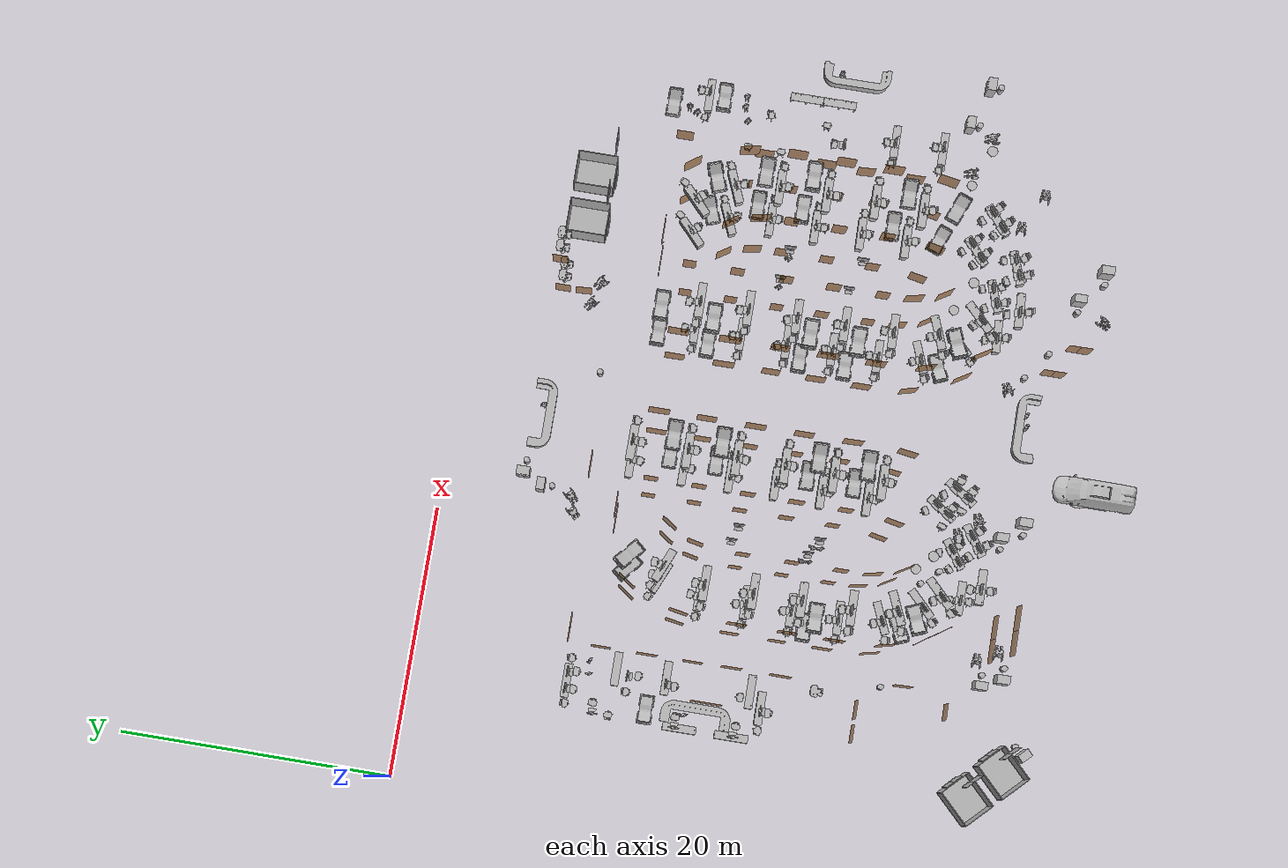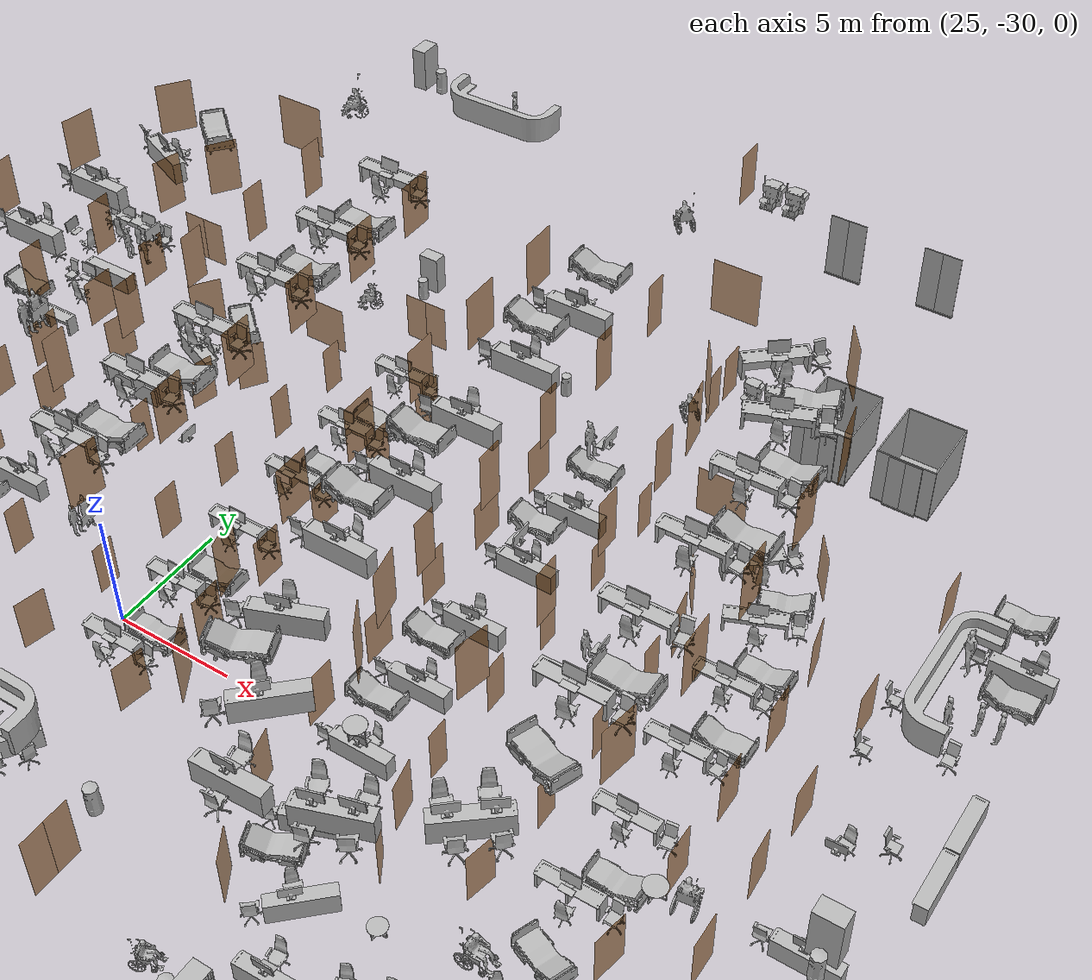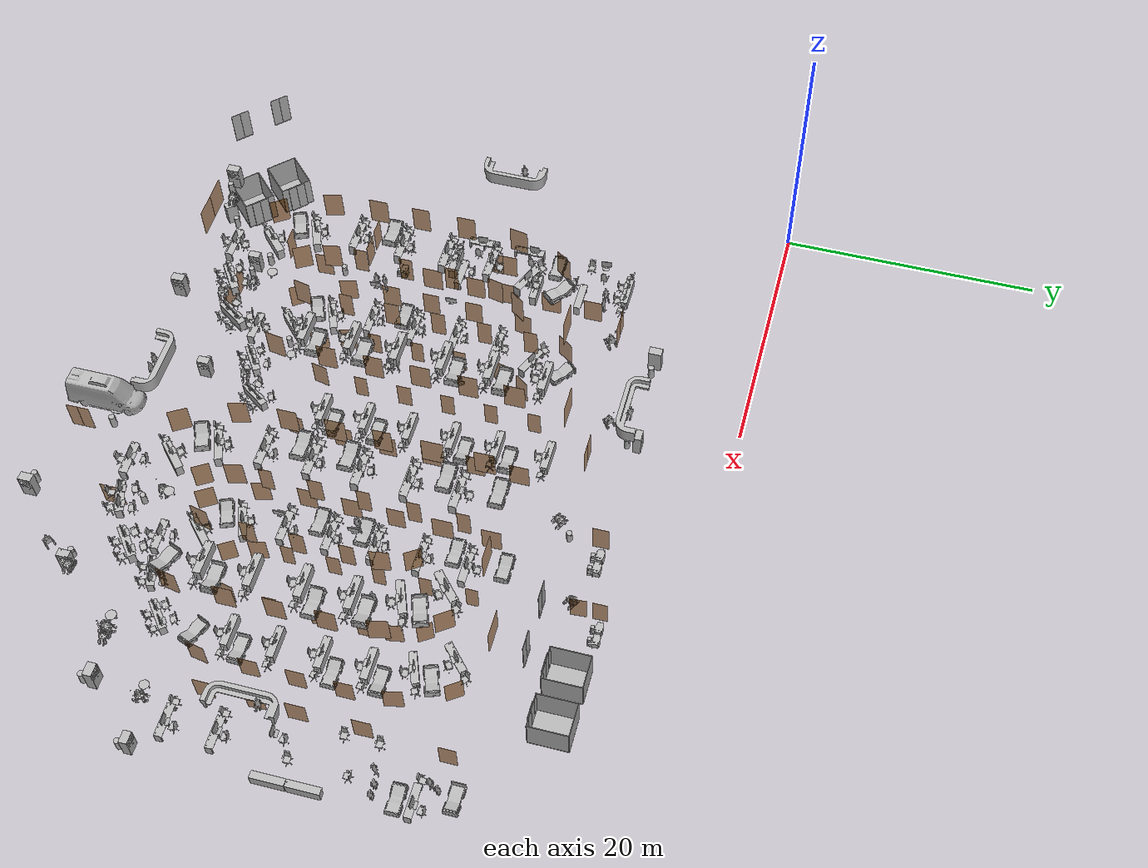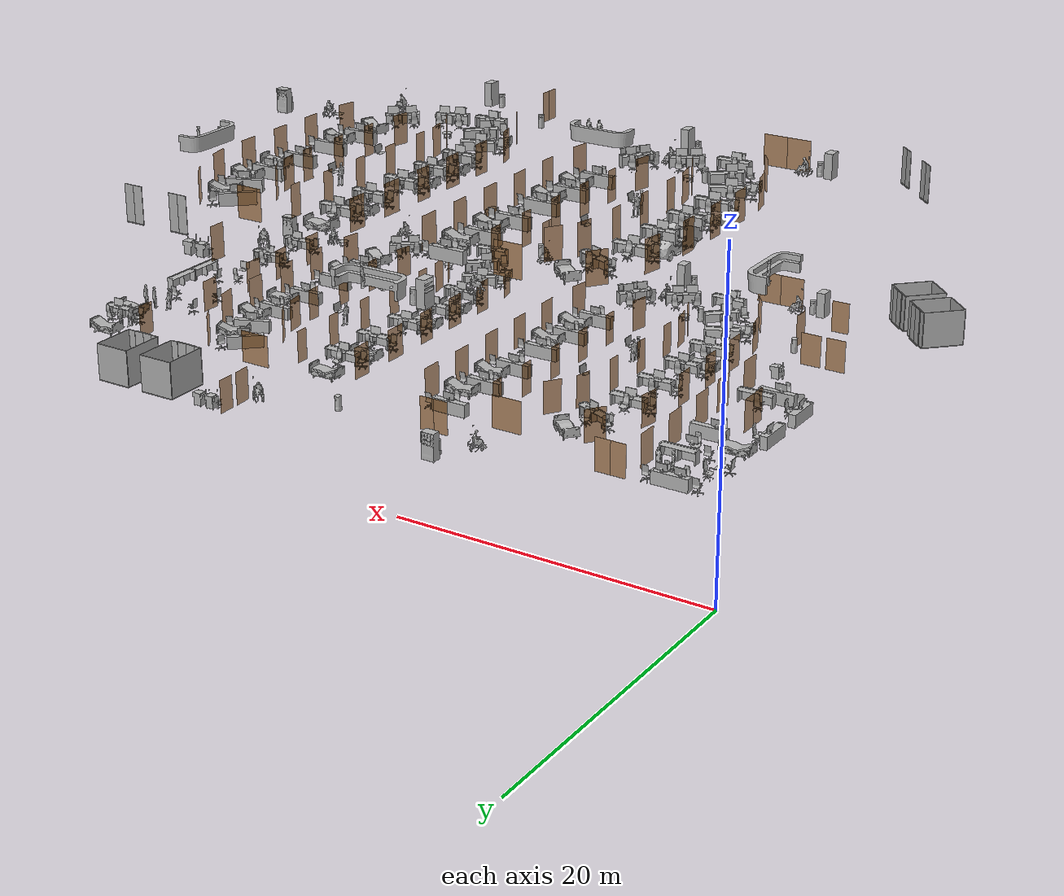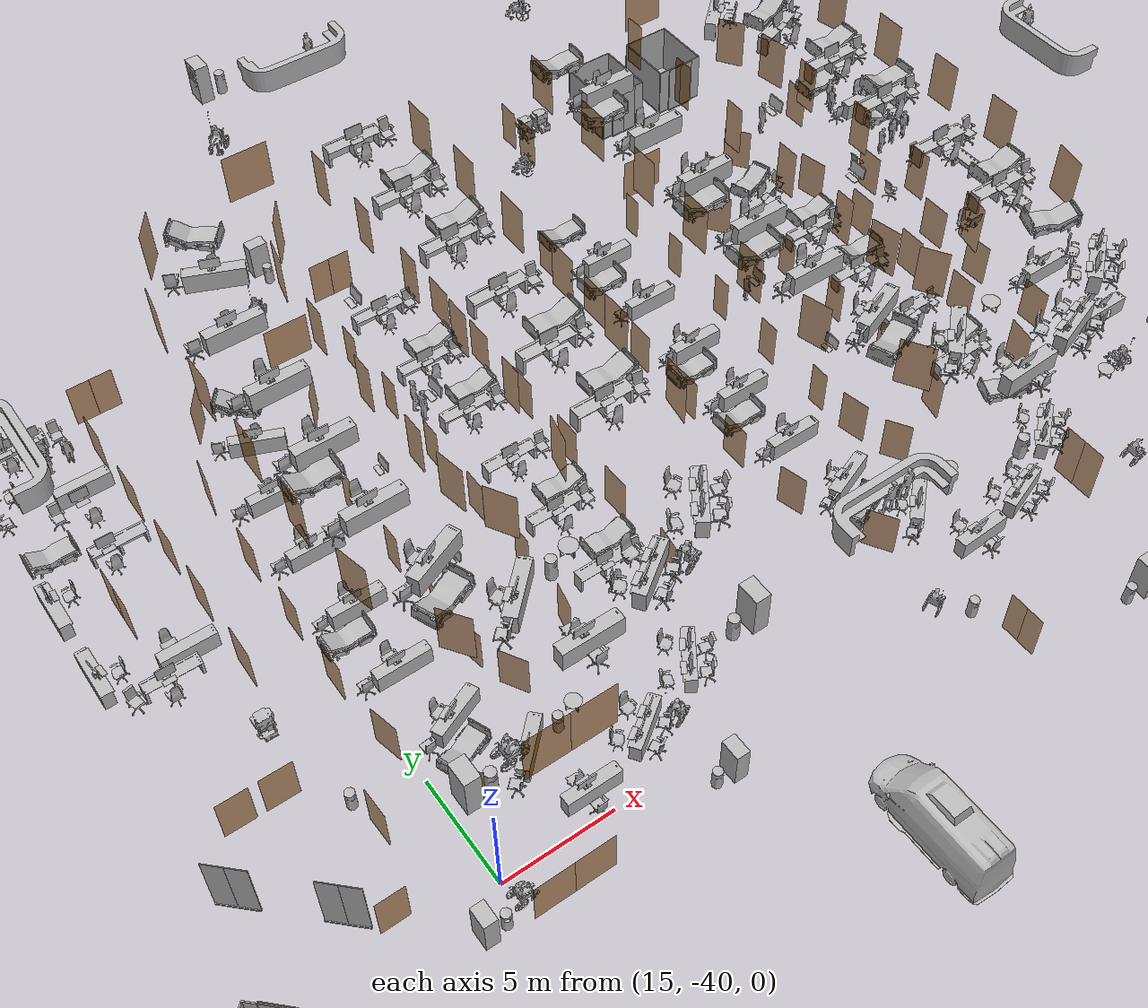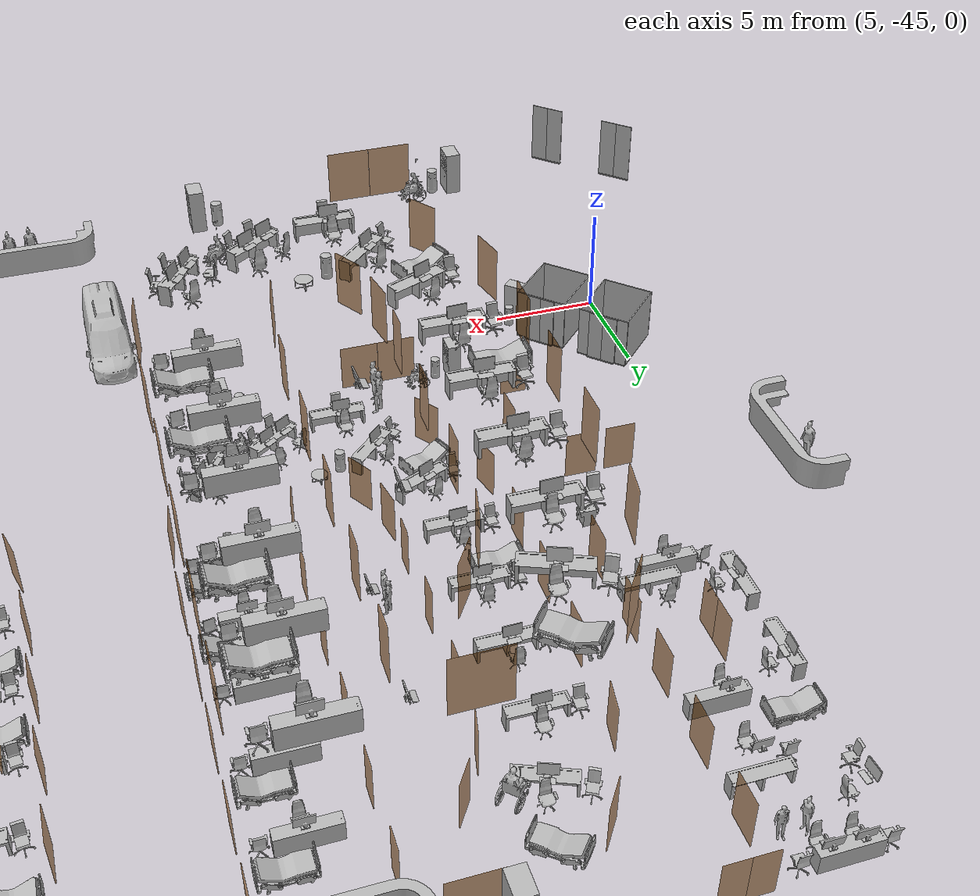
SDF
<sdf version="1.7">
 <world name="sim_world">
  <physics name="10ms" type="ode">
   <max_step_size>0.01</max_step_size>
   <real_time_factor>1.0</real_time_factor>
  </physics>
  <plugin filename="libignition-gazebo-physics-system.so" name="ignition::gazebo::systems::Physics"/>
  <plugin filename="libignition-gazebo-user-commands-system.so" name="ignition::gazebo::systems::UserCommands"/>
  <plugin filename="libignition-gazebo-scene-broadcaster-system.so" name="ignition::gazebo::systems::SceneBroadcaster"/>
  <scene><ambient>1 1 1</ambient><background>0.8 0.8 0.8</background><grid>false</grid></scene>
  <light type="directional" name="sun">
   <pose>0 0 10 0 0 0</pose>
   <diffuse>1 1 1 1</diffuse>
   <specular>0.2 0.2 0.2 1</specular>
   <attenuation>
    <range>1000</range>
    <constant>0.09</constant>
    <linear>0.001</linear>
    <quadratic>0.001</quadratic>
   </attenuation>
   <direction>-0.5 0.1 -0.9</direction>
  </light>
  <include>
   <name>OpenRobotics/CoffeeTable</name>
   <uri>model://CoffeeTable</uri>
   <pose>21.28316603207571 -35.513484096765545 0.0 0 0 1.5708</pose>
   <static>True</static>
  </include>
  <include>
   <name>OpenRobotics/CoffeeTable_2</name>
   <uri>model://CoffeeTable</uri>
   <pose>50.619145417483985 -35.45603246029002 0.0 0 0 1.5708</pose>
   <static>True</static>
  </include>
  <include>
   <name>OpenRobotics/CoffeeTable_3</name>
   <uri>model://CoffeeTable</uri>
   <pose>40.95399792315684 -35.49049267335875 0.0 0 0 1.5708</pose>
   <static>True</static>
  </include>
  <include>
   <name>OpenRobotics/CGMVanguard</name>
   <uri>model://CGMVanguard</uri>
   <pose>26.88397369331951 -26.628133533325663 0.0 0 0 -3.1416</pose>
   <static>True</static>
  </include>
  <include>
   <name>OpenRobotics/CGMVanguard_2</name>
   <uri>model://CGMVanguard</uri>
   <pose>26.892454136379392 -30.11354178685438 0.0 0 0 -3.1416</pose>
   <static>True</static>
  </include>
  <include>
   <name>OpenRobotics/CGMVanguard_3</name>
   <uri>model://CGMVanguard</uri>
   <pose>35.31267258951582 -24.65983616014771 0.0 0 0 0.0</pose>
   <static>True</static>
  </include>
  <include>
   <name>OpenRobotics/CGMVanguard_4</name>
   <uri>model://CGMVanguard</uri>
   <pose>35.29113495634787 -28.073120264605233 0.0 0 0 0.0</pose>
   <static>True</static>
  </include>
  <include>
   <name>OpenRobotics/CGMVanguard_5</name>
   <uri>model://CGMVanguard</uri>
   <pose>36.303296027075916 -34.964328295065606 0.0 0 0 0.3823</pose>
   <static>True</static>
  </include>
  <include>
   <name>OpenRobotics/CGMVanguard_6</name>
   <uri>model://CGMVanguard</uri>
   <pose>46.09093881004581 -33.67223183723706 0.0 0 0 2.7684</pose>
   <static>True</static>
  </include>
  <include>
   <name>OpenRobotics/CGMVanguard_7</name>
   <uri>model://CGMVanguard</uri>
   <pose>46.597019345409834 -30.06510903426794 0.0 0 0 3.1416</pose>
   <static>True</static>
  </include>
  <include>
   <name>OpenRobotics/CGMVanguard_8</name>
   <uri>model://CGMVanguard</uri>
   <pose>46.58625052882586 -23.184696742433005 0.0 0 0 -0.0029</pose>
   <static>True</static>
  </include>
  <include>
   <name>OpenRobotics/CGMVanguard_9</name>
   <uri>model://CGMVanguard</uri>
   <pose>46.53240644590597 -19.81446098226993 0.0 0 0 -3.1416</pose>
   <static>True</static>
  </include>
  <include>
   <name>OpenRobotics/CGMVanguard_10</name>
   <uri>model://CGMVanguard</uri>
   <pose>45.574116380139266 -16.358101611476496 0.0 0 0 -2.7959</pose>
   <static>True</static>
  </include>
  <include>
   <name>OpenRobotics/CGMVanguard_11</name>
   <uri>model://CGMVanguard</uri>
   <pose>54.18809276566291 -16.056601669166582 0.0 0 0 0.0092</pose>
   <static>True</static>
  </include>
  <include>
   <name>OpenRobotics/CGMVanguard_12</name>
   <uri>model://CGMVanguard</uri>
   <pose>53.37574708665056 -12.342248375062509 0.0 0 0 -3.1416</pose>
   <static>True</static>
  </include>
  <include>
   <name>OpenRobotics/CGMVanguard_13</name>
   <uri>model://CGMVanguard</uri>
   <pose>17.883800623052974 -14.5233106418984 0.0 0 0 -0.7084</pose>
   <static>True</static>
  </include>
  <include>
   <name>OpenRobotics/CGMVanguard_14</name>
   <uri>model://CGMVanguard</uri>
   <pose>26.872747202030713 -19.778627745086744 0.0 0 0 -3.1416</pose>
   <static>True</static>
  </include>
  <include>
   <name>OpenRobotics/CGMVanguard_15</name>
   <uri>model://CGMVanguard</uri>
   <pose>26.839310026537465 -16.334087150494224 0.0 0 0 -3.1416</pose>
   <static>True</static>
  </include>
  <include>
   <name>OpenRobotics/CGMVanguard_16</name>
   <uri>model://CGMVanguard</uri>
   <pose>15.597392407984323 -28.028079689242748 0.0 0 0 0.0</pose>
   <static>True</static>
  </include>
  <include>
   <name>OpenRobotics/CGMVanguard_17</name>
   <uri>model://CGMVanguard</uri>
   <pose>16.623283719856943 -34.967612784123716 0.0 0 0 0.3826</pose>
   <static>True</static>
  </include>
  <include>
   <name>OpenRobotics/CGMVanguard_18</name>
   <uri>model://CGMVanguard</uri>
   <pose>7.788492750278842 -17.53642552209532 0.0 0 0 0.0</pose>
   <static>True</static>
  </include>
  <include>
   <name>OpenRobotics/CGMVanguard_19</name>
   <uri>model://CGMVanguard</uri>
   <pose>35.31313026422064 -17.750913426406694 0.0 0 0 0.0</pose>
   <static>True</static>
  </include>
  <include>
   <name>OpenRobotics/CGMVanguard_20</name>
   <uri>model://CGMVanguard</uri>
   <pose>35.63772931810318 -13.985596707818942 0.0 0 0 0.0</pose>
   <static>True</static>
  </include>
  <include>
   <name>OpenRobotics/NurseTable</name>
   <uri>model://NurseTable</uri>
   <pose>9.008949655782477 -11.460766893581026 0.0 0 0 0.0</pose>
   <static>True</static>
  </include>
  <include>
   <name>OpenRobotics/NurseTable_2</name>
   <uri>model://NurseTable</uri>
   <pose>25.969216568593538 -36.71566093611788 0.0 0 0 -2.1716</pose>
   <static>True</static>
  </include>
  <include>
   <name>OpenRobotics/NurseTable_3</name>
   <uri>model://NurseTable</uri>
   <pose>22.785792854121013 -38.1124841352256 0.0 0 0 -2.5278</pose>
   <static>True</static>
  </include>
  <include>
   <name>OpenRobotics/NurseTable_4</name>
   <uri>model://NurseTable</uri>
   <pose>42.41287642782974 -38.32261066882046 0.0 0 0 -2.8065</pose>
   <static>True</static>
  </include>
  <include>
   <name>OpenRobotics/NurseTable_5</name>
   <uri>model://NurseTable</uri>
   <pose>45.57325487481255 -36.488277373947184 0.0 0 0 -2.4507</pose>
   <static>True</static>
  </include>
  <include>
   <name>OpenRobotics/NurseTable_6</name>
   <uri>model://NurseTable</uri>
   <pose>54.19215799392336 -14.938960039998475 0.0 0 0 3.1416</pose>
   <static>True</static>
  </include>
  <include>
   <name>OpenRobotics/NurseTable_7</name>
   <uri>model://NurseTable</uri>
   <pose>44.96476289373489 -17.75605553632554 0.0 0 0 0.3883</pose>
   <static>True</static>
  </include>
  <include>
   <name>OpenRobotics/NurseTable_8</name>
   <uri>model://NurseTable</uri>
   <pose>43.50017691627249 -15.209822699126969 0.0 0 0 0.7491</pose>
   <static>True</static>
  </include>
  <include>
   <name>OpenRobotics/NurseTable_9</name>
   <uri>model://NurseTable</uri>
   <pose>45.44847121264571 -20.873358716972444 0.0 0 0 0.0053</pose>
   <static>True</static>
  </include>
  <include>
   <name>OpenRobotics/NurseTable_10</name>
   <uri>model://NurseTable</uri>
   <pose>45.42833352563367 -24.266101303796027 0.0 0 0 0.0072</pose>
   <static>True</static>
  </include>
  <include>
   <name>OpenRobotics/NurseTable_11</name>
   <uri>model://NurseTable</uri>
   <pose>45.48877350871124 -27.712607207415125 0.0 0 0 0.0098</pose>
   <static>True</static>
  </include>
  <include>
   <name>OpenRobotics/NurseTable_12</name>
   <uri>model://NurseTable</uri>
   <pose>45.413203338333176 -31.140859966924374 0.0 0 0 0.0034</pose>
   <static>True</static>
  </include>
  <include>
   <name>OpenRobotics/NurseTable_13</name>
   <uri>model://NurseTable</uri>
   <pose>6.869993461789938 -20.165659013114897 0.0 0 0 1.5708</pose>
   <static>True</static>
  </include>
  <include>
   <name>OpenRobotics/NurseTable_14</name>
   <uri>model://NurseTable</uri>
   <pose>6.872066458982353 -23.99090419599248 0.0 0 0 1.5708</pose>
   <static>True</static>
  </include>
  <include>
   <name>OpenRobotics/NurseTable_15</name>
   <uri>model://NurseTable</uri>
   <pose>17.26572439521558 -33.51072651051886 0.0 0 0 -2.7383</pose>
   <static>True</static>
  </include>
  <include>
   <name>OpenRobotics/NurseTable_16</name>
   <uri>model://NurseTable</uri>
   <pose>25.770343448328934 -31.184662128379706 0.0 0 0 0.0036</pose>
   <static>True</static>
  </include>
  <include>
   <name>OpenRobotics/NurseTable_17</name>
   <uri>model://NurseTable</uri>
   <pose>25.744821353024907 -27.741763778316244 0.0 0 0 0.004</pose>
   <static>True</static>
  </include>
  <include>
   <name>OpenRobotics/NurseTable_18</name>
   <uri>model://NurseTable</uri>
   <pose>16.75862082227608 -30.446028998884685 0.0 0 0 -3.1371</pose>
   <static>True</static>
  </include>
  <include>
   <name>OpenRobotics/NurseTable_19</name>
   <uri>model://NurseTable</uri>
   <pose>16.765620553055665 -26.949690396523234 0.0 0 0 -3.1416</pose>
   <static>True</static>
  </include>
  <include>
   <name>OpenRobotics/NurseTable_20</name>
   <uri>model://NurseTable</uri>
   <pose>16.78801969155034 -23.54494057920851 0.0 0 0 -3.1416</pose>
   <static>True</static>
  </include>
  <include>
   <name>OpenRobotics/NurseTable_21</name>
   <uri>model://NurseTable</uri>
   <pose>16.804226760509227 -20.1163916772432 0.0 0 0 3.1309</pose>
   <static>True</static>
  </include>
  <include>
   <name>OpenRobotics/NurseTable_22</name>
   <uri>model://NurseTable</uri>
   <pose>17.55074804815201 -17.118864659051592 0.0 0 0 2.7367</pose>
   <static>True</static>
  </include>
  <include>
   <name>OpenRobotics/NurseTable_23</name>
   <uri>model://NurseTable</uri>
   <pose>25.736421676089403 -13.476554747894324 0.0 0 0 -0.0073</pose>
   <static>True</static>
  </include>
  <include>
   <name>OpenRobotics/NurseTable_24</name>
   <uri>model://NurseTable</uri>
   <pose>25.779766162839913 -17.413095650167318 0.0 0 0 0.0011</pose>
   <static>True</static>
  </include>
  <include>
   <name>OpenRobotics/NurseTable_25</name>
   <uri>model://NurseTable</uri>
   <pose>25.825910541902257 -20.877827775854794 0.0 0 0 -0.0008</pose>
   <static>True</static>
  </include>
  <include>
   <name>OpenRobotics/NurseTable_26</name>
   <uri>model://NurseTable</uri>
   <pose>25.821468405061367 -24.2898465443637 0.0 0 0 0.0073</pose>
   <static>True</static>
  </include>
  <include>
   <name>OpenRobotics/NurseTable_27</name>
   <uri>model://NurseTable</uri>
   <pose>36.48273143340644 -16.664339833083357 0.0 0 0 -3.1416</pose>
   <static>True</static>
  </include>
  <include>
   <name>OpenRobotics/NurseTable_28</name>
   <uri>model://NurseTable</uri>
   <pose>36.470858813122604 -20.10966116687821 0.0 0 0 -3.1416</pose>
   <static>True</static>
  </include>
  <include>
   <name>OpenRobotics/NurseTable_29</name>
   <uri>model://NurseTable</uri>
   <pose>36.427595092496475 -23.56122841429178 0.0 0 0 3.1416</pose>
   <static>True</static>
  </include>
  <include>
   <name>OpenRobotics/NurseTable_30</name>
   <uri>model://NurseTable</uri>
   <pose>36.43841775316337 -26.98032767970465 0.0 0 0 3.1416</pose>
   <static>True</static>
  </include>
  <include>
   <name>OpenRobotics/NurseTable_31</name>
   <uri>model://NurseTable</uri>
   <pose>36.470858813122604 -30.399400023076062 0.0 0 0 3.1416</pose>
   <static>True</static>
  </include>
  <include>
   <name>OpenRobotics/NurseTable_32</name>
   <uri>model://NurseTable</uri>
   <pose>36.92530287296646 -33.50472289527329 0.0 0 0 -2.7739</pose>
   <static>True</static>
  </include>
  <include>
   <name>OpenRobotics/NurseTable_33</name>
   <uri>model://NurseTable</uri>
   <pose>38.48336217837779 -36.188069689627355 0.0 0 0 -2.3763</pose>
   <static>True</static>
  </include>
  <include>
   <name>OpenRobotics/NurseTable_34</name>
   <uri>model://NurseTable</uri>
   <pose>52.92905657474717 -32.91938386985119 0.0 0 0 3.1416</pose>
   <static>True</static>
  </include>
  <include>
   <name>OpenRobotics/NurseTable_35</name>
   <uri>model://NurseTable</uri>
   <pose>52.90471904926738 -29.283239106188248 0.0 0 0 3.1416</pose>
   <static>True</static>
  </include>
  <include>
   <name>OpenRobotics/NurseTable_36</name>
   <uri>model://NurseTable</uri>
   <pose>55.15445944386759 -24.680296911657265 0.0 0 0 -1.5708</pose>
   <static>True</static>
  </include>
  <include>
   <name>OpenRobotics/NurseTable_37</name>
   <uri>model://NurseTable</uri>
   <pose>18.77753163339873 -36.26738202376835 0.0 0 0 -2.37</pose>
   <static>True</static>
  </include>
  <include>
   <name>OpenRobotics/NurseTable_38</name>
   <uri>model://NurseTable</uri>
   <pose>19.64964424445215 -39.04807892004157 0.0 0 0 -3.1416</pose>
   <static>True</static>
  </include>
  <include>
   <name>OpenRobotics/NurseTable_39</name>
   <uri>model://NurseTable</uri>
   <pose>55.14657128571983 -22.179885389023518 0.0 0 0 -1.5708</pose>
   <static>True</static>
  </include>
  <include>
   <name>OpenRobotics/NurseTable_40</name>
   <uri>model://NurseTable</uri>
   <pose>39.41238798507753 -38.948251990308094 0.0 0 0 -3.1045</pose>
   <static>True</static>
  </include>
  <include>
   <name>OpenRobotics/NurseTable_41</name>
   <uri>model://NurseTable</uri>
   <pose>10.358066997423185 -18.63942156070922 0.0 0 0 0.0</pose>
   <static>True</static>
  </include>
  <include>
   <name>OpenRobotics/NurseTable_42</name>
   <uri>model://NurseTable</uri>
   <pose>10.37039729241184 -24.918314680204627 0.0 0 0 -3.1416</pose>
   <static>True</static>
  </include>
  <include>
   <name>OpenRobotics/NurseTable_43</name>
   <uri>model://NurseTable</uri>
   <pose>9.294404061382263 -25.721426098996215 0.0 0 0 0.0</pose>
   <static>True</static>
  </include>
  <include>
   <name>OpenRobotics/NurseTable_44</name>
   <uri>model://NurseTable</uri>
   <pose>10.435117880081545 -15.01296873197186 0.0 0 0 3.1416</pose>
   <static>True</static>
  </include>
  <include>
   <name>OpenRobotics/DeskChair</name>
   <uri>model://DeskChair</uri>
   <pose>19.392188761970708 -38.37179723856778 0.0 0 0 1.5708</pose>
   <static>True</static>
  </include>
  <include>
   <name>OpenRobotics/DeskChair_2</name>
   <uri>model://DeskChair</uri>
   <pose>21.619503096034787 -37.88580054613288 0.0 0 0 -0.7706</pose>
   <static>True</static>
  </include>
  <include>
   <name>OpenRobotics/DeskChair_3</name>
   <uri>model://DeskChair</uri>
   <pose>22.753001807622805 -36.9909388100458 0.0 0 0 -1.489</pose>
   <static>True</static>
  </include>
  <include>
   <name>OpenRobotics/DeskChair_4</name>
   <uri>model://DeskChair</uri>
   <pose>24.676985500557695 -36.931279566170566 0.0 0 0 -0.3695</pose>
   <static>True</static>
  </include>
  <include>
   <name>OpenRobotics/DeskChair_5</name>
   <uri>model://DeskChair</uri>
   <pose>25.638963886004408 -35.5442290681128 0.0 0 0 -1.0979</pose>
   <static>True</static>
  </include>
  <include>
   <name>OpenRobotics/DeskChair_6</name>
   <uri>model://DeskChair</uri>
   <pose>8.457209338102388 -12.107515095573259 0.0 0 0 1.5708</pose>
   <static>True</static>
  </include>
  <include>
   <name>OpenRobotics/DeskChair_7</name>
   <uri>model://DeskChair</uri>
   <pose>9.777573939463874 -12.138798507749712 0.0 0 0 1.5708</pose>
   <static>True</static>
  </include>
  <include>
   <name>OpenRobotics/DeskChair_8</name>
   <uri>model://DeskChair</uri>
   <pose>7.7663628321987686 -13.647159724625988 0.0 0 0 3.085</pose>
   <static>True</static>
  </include>
  <include>
   <name>OpenRobotics/DeskChair_9</name>
   <uri>model://DeskChair</uri>
   <pose>10.174431752624908 -16.65626322064537 0.0 0 0 1.5708</pose>
   <static>True</static>
  </include>
  <include>
   <name>OpenRobotics/DeskChair_10</name>
   <uri>model://DeskChair</uri>
   <pose>9.840140763816784 -19.37897003961388 0.0 0 0 1.6366</pose>
   <static>True</static>
  </include>
  <include>
   <name>OpenRobotics/DeskChair_11</name>
   <uri>model://DeskChair</uri>
   <pose>7.7000269220414665 -19.76694357909313 0.0 0 0 3.135</pose>
   <static>True</static>
  </include>
  <include>
   <name>OpenRobotics/DeskChair_12</name>
   <uri>model://DeskChair</uri>
   <pose>7.7511518787739 -24.220279989231205 0.0 0 0 3.0982</pose>
   <static>True</static>
  </include>
  <include>
   <name>OpenRobotics/DeskChair_13</name>
   <uri>model://DeskChair</uri>
   <pose>9.862136071689559 -24.183073727933564 0.0 0 0 -1.5817</pose>
   <static>True</static>
  </include>
  <include>
   <name>OpenRobotics/DeskChair_14</name>
   <uri>model://DeskChair</uri>
   <pose>9.04612899503866 -26.41262259143881 0.0 0 0 1.5708</pose>
   <static>True</static>
  </include>
  <include>
   <name>OpenRobotics/DeskChair_15</name>
   <uri>model://DeskChair</uri>
   <pose>16.567097419330043 -29.722499134648693 0.0 0 0 -1.5664</pose>
   <static>True</static>
  </include>
  <include>
   <name>OpenRobotics/DeskChair_16</name>
   <uri>model://DeskChair</uri>
   <pose>16.78406215145573 -32.98765816699361 0.0 0 0 -1.204</pose>
   <static>True</static>
  </include>
  <include>
   <name>OpenRobotics/DeskChair_17</name>
   <uri>model://DeskChair</uri>
   <pose>18.158324679820023 -35.89117341640709 0.0 0 0 -1.1703</pose>
   <static>True</static>
  </include>
  <include>
   <name>OpenRobotics/DeskChair_18</name>
   <uri>model://DeskChair</uri>
   <pose>25.859266951271128 -31.849878850813457 0.0 0 0 1.5708</pose>
   <static>True</static>
  </include>
  <include>
   <name>OpenRobotics/DeskChair_19</name>
   <uri>model://DeskChair</uri>
   <pose>25.851540325372124 -28.44292142609902 0.0 0 0 1.5708</pose>
   <static>True</static>
  </include>
  <include>
   <name>OpenRobotics/DeskChair_20</name>
   <uri>model://DeskChair</uri>
   <pose>25.900000000000023 -24.942517595477117 0.0 0 0 1.5708</pose>
   <static>True</static>
  </include>
  <include>
   <name>OpenRobotics/DeskChair_21</name>
   <uri>model://DeskChair</uri>
   <pose>16.63941002269145 -26.292011845698266 0.0 0 0 -1.5444</pose>
   <static>True</static>
  </include>
  <include>
   <name>OpenRobotics/DeskChair_22</name>
   <uri>model://DeskChair</uri>
   <pose>16.577408561209197 -22.809861159186205 0.0 0 0 -1.6217</pose>
   <static>True</static>
  </include>
  <include>
   <name>OpenRobotics/DeskChair_23</name>
   <uri>model://DeskChair</uri>
   <pose>25.907026652821067 -18.080816122456845 0.0 0 0 1.5708</pose>
   <static>True</static>
  </include>
  <include>
   <name>OpenRobotics/DeskChair_24</name>
   <uri>model://DeskChair</uri>
   <pose>16.742736817814716 -19.462024537517806 0.0 0 0 1.5708</pose>
   <static>True</static>
  </include>
  <include>
   <name>OpenRobotics/DeskChair_25</name>
   <uri>model://DeskChair</uri>
   <pose>17.72436829352719 -16.434533287181274 0.0 0 0 1.5708</pose>
   <static>True</static>
  </include>
  <include>
   <name>OpenRobotics/DeskChair_26</name>
   <uri>model://DeskChair</uri>
   <pose>25.87692781046885 -14.223318333910248 0.0 0 0 1.5708</pose>
   <static>True</static>
  </include>
  <include>
   <name>OpenRobotics/DeskChair_27</name>
   <uri>model://DeskChair</uri>
   <pose>36.313041806084414 -19.441375331718028 0.0 0 0 -1.6777</pose>
   <static>True</static>
  </include>
  <include>
   <name>OpenRobotics/DeskChair_28</name>
   <uri>model://DeskChair</uri>
   <pose>36.12706434367912 -22.8408484289066 0.0 0 0 -1.3396</pose>
   <static>True</static>
  </include>
  <include>
   <name>OpenRobotics/DeskChair_29</name>
   <uri>model://DeskChair</uri>
   <pose>36.3957193954079 -26.364324449059673 0.0 0 0 -1.5526</pose>
   <static>True</static>
  </include>
  <include>
   <name>OpenRobotics/DeskChair_30</name>
   <uri>model://DeskChair</uri>
   <pose>44.072970270374256 -15.638906195915554 0.0 0 0 2.263</pose>
   <static>True</static>
  </include>
  <include>
   <name>OpenRobotics/DeskChair_31</name>
   <uri>model://DeskChair</uri>
   <pose>45.34390600361529 -18.408080458443923 0.0 0 0 1.5708</pose>
   <static>True</static>
  </include>
  <include>
   <name>OpenRobotics/DeskChair_32</name>
   <uri>model://DeskChair</uri>
   <pose>45.6332371831853 -21.538925425945173 0.0 0 0 1.5708</pose>
   <static>True</static>
  </include>
  <include>
   <name>OpenRobotics/DeskChair_33</name>
   <uri>model://DeskChair</uri>
   <pose>45.560897657782434 -25.010738048536616 0.0 0 0 1.6647</pose>
   <static>True</static>
  </include>
  <include>
   <name>OpenRobotics/DeskChair_34</name>
   <uri>model://DeskChair</uri>
   <pose>45.59188492750283 -28.368885812084173 0.0 0 0 1.5708</pose>
   <static>True</static>
  </include>
  <include>
   <name>OpenRobotics/DeskChair_35</name>
   <uri>model://DeskChair</uri>
   <pose>45.6332371831853 -31.892388754278706 0.0 0 0 1.6796</pose>
   <static>True</static>
  </include>
  <include>
   <name>OpenRobotics/DeskChair_36</name>
   <uri>model://DeskChair</uri>
   <pose>37.8422945271336 -35.83951001884546 0.0 0 0 -0.7454</pose>
   <static>True</static>
  </include>
  <include>
   <name>OpenRobotics/DeskChair_37</name>
   <uri>model://DeskChair</uri>
   <pose>36.54037152417218 -32.95664397523175 0.0 0 0 -1.1263</pose>
   <static>True</static>
  </include>
  <include>
   <name>OpenRobotics/DeskChair_38</name>
   <uri>model://DeskChair</uri>
   <pose>36.48870812661055 -29.722499134648693 0.0 0 0 -1.7595</pose>
   <static>True</static>
  </include>
  <include>
   <name>OpenRobotics/DeskChair_39</name>
   <uri>model://DeskChair</uri>
   <pose>39.040917657013225 -38.05072497211649 0.0 0 0 -1.4389</pose>
   <static>True</static>
  </include>
  <include>
   <name>OpenRobotics/DeskChair_40</name>
   <uri>model://DeskChair</uri>
   <pose>41.386446675127914 -37.668405061343826 0.0 0 0 -1.1243</pose>
   <static>True</static>
  </include>
  <include>
   <name>OpenRobotics/DeskChair_41</name>
   <uri>model://DeskChair</uri>
   <pose>42.83304872889508 -37.317099342333016 0.0 0 0 -1.3139</pose>
   <static>True</static>
  </include>
  <include>
   <name>OpenRobotics/DeskChair_42</name>
   <uri>model://DeskChair</uri>
   <pose>44.517291642629175 -36.3664820583824 0.0 0 0 -0.786</pose>
   <static>True</static>
  </include>
  <include>
   <name>OpenRobotics/DeskChair_43</name>
   <uri>model://DeskChair</uri>
   <pose>45.416245529018155 -35.38485058266993 0.0 0 0 -0.9053</pose>
   <static>True</static>
  </include>
  <include>
   <name>OpenRobotics/DeskChair_44</name>
   <uri>model://DeskChair</uri>
   <pose>53.06363986000543 -32.26894734817894 0.0 0 0 -1.6575</pose>
   <static>True</static>
  </include>
  <include>
   <name>OpenRobotics/DeskChair_45</name>
   <uri>model://DeskChair</uri>
   <pose>52.856986269758906 -28.629518095457893 0.0 0 0 -1.4394</pose>
   <static>True</static>
  </include>
  <include>
   <name>OpenRobotics/DeskChair_46</name>
   <uri>model://DeskChair</uri>
   <pose>54.57913541786859 -14.209534248682756 0.0 0 0 -1.715</pose>
   <static>True</static>
  </include>
  <include>
   <name>OpenRobotics/DeskChair_47</name>
   <uri>model://DeskChair</uri>
   <pose>25.802676820122326 -21.585123649090438 0.0 0 0 1.5708</pose>
   <static>True</static>
  </include>
  <include>
   <name>OpenRobotics/DeskChair_48</name>
   <uri>model://DeskChair</uri>
   <pose>52.04628283527561 -24.736860120764607 0.0 0 0 -1.7281</pose>
   <static>True</static>
  </include>
  <include>
   <name>OpenRobotics/OfficeChairGrey</name>
   <uri>model://OfficeChairGrey</uri>
   <pose>19.48318526210532 -39.605742086842845 0.0 0 0 -3.1182</pose>
   <static>True</static>
  </include>
  <include>
   <name>OpenRobotics/OfficeChairGrey_2</name>
   <uri>model://OfficeChairGrey</uri>
   <pose>22.566189761932254 -38.93406407445871 0.0 0 0 -2.6428</pose>
   <static>True</static>
  </include>
  <include>
   <name>OpenRobotics/OfficeChairGrey_3</name>
   <uri>model://OfficeChairGrey</uri>
   <pose>23.432433367947407 -38.318895427098994 0.0 0 0 -2.3511</pose>
   <static>True</static>
  </include>
  <include>
   <name>OpenRobotics/OfficeChairGrey_4</name>
   <uri>model://OfficeChairGrey</uri>
   <pose>26.094834814045637 -37.486896657820886 0.0 0 0 -2.1035</pose>
   <static>True</static>
  </include>
  <include>
   <name>OpenRobotics/OfficeChairGrey_5</name>
   <uri>model://OfficeChairGrey</uri>
   <pose>26.727152801815336 -36.599438483135295 0.0 0 0 -1.8657</pose>
   <static>True</static>
  </include>
  <include>
   <name>OpenRobotics/OfficeChairGrey_6</name>
   <uri>model://OfficeChairGrey</uri>
   <pose>39.44014460982274 -39.483704472904925 0.0 0 0 -3.0604</pose>
   <static>True</static>
  </include>
  <include>
   <name>OpenRobotics/OfficeChairGrey_7</name>
   <uri>model://OfficeChairGrey</uri>
   <pose>42.04708665051348 -39.02888350448063 0.0 0 0 -2.8514</pose>
   <static>True</static>
  </include>
  <include>
   <name>OpenRobotics/OfficeChairGrey_8</name>
   <uri>model://OfficeChairGrey</uri>
   <pose>43.168605053651824 -38.666755124802926 0.0 0 0 -2.5536</pose>
   <static>True</static>
  </include>
  <include>
   <name>OpenRobotics/OfficeChairGrey_9</name>
   <uri>model://OfficeChairGrey</uri>
   <pose>45.541486865889816 -37.19848082766051 0.0 0 0 -2.4327</pose>
   <static>True</static>
  </include>
  <include>
   <name>OpenRobotics/OfficeChairGrey_10</name>
   <uri>model://OfficeChairGrey</uri>
   <pose>46.48443136802435 -36.41084958270839 0.0 0 0 -2.3371</pose>
   <static>True</static>
  </include>
  <include>
   <name>OpenRobotics/OfficeChairGrey_11</name>
   <uri>model://OfficeChairGrey</uri>
   <pose>53.49544248298147 -24.008457367024366 0.0 0 0 1.5708</pose>
   <static>True</static>
  </include>
  <include>
   <name>OpenRobotics/OfficeChairGrey_12</name>
   <uri>model://OfficeChairGrey</uri>
   <pose>53.49544248298147 -19.837371639552345 0.0 0 0 -0.016</pose>
   <static>True</static>
  </include>
  <include>
   <name>OpenRobotics/OfficeChairGrey_13</name>
   <uri>model://OfficeChairGrey</uri>
   <pose>52.55249798084694 -14.678946963578337 0.0 0 0 3.1246</pose>
   <static>True</static>
  </include>
  <include>
   <name>OpenRobotics/OfficeChairGrey_14</name>
   <uri>model://OfficeChairGrey</uri>
   <pose>44.86480135379412 -14.257401638398536 0.0 0 0 0.937</pose>
   <static>True</static>
  </include>
  <include>
   <name>OpenRobotics/OfficeChairGrey_15</name>
   <uri>model://OfficeChairGrey</uri>
   <pose>46.539890773431836 -17.36355909388102 0.0 0 0 0.4229</pose>
   <static>True</static>
  </include>
  <include>
   <name>OpenRobotics/OfficeChairGrey_16</name>
   <uri>model://OfficeChairGrey</uri>
   <pose>47.03910618822357 -21.11309949617324 0.0 0 0 -0.09</pose>
   <static>True</static>
  </include>
  <include>
   <name>OpenRobotics/OfficeChairGrey_17</name>
   <uri>model://OfficeChairGrey</uri>
   <pose>47.03910618822357 -24.49658090073461 0.0 0 0 -0.1276</pose>
   <static>True</static>
  </include>
  <include>
   <name>OpenRobotics/OfficeChairGrey_18</name>
   <uri>model://OfficeChairGrey</uri>
   <pose>47.11674935579405 -27.946613591784956 0.0 0 0 0.1131</pose>
   <static>True</static>
  </include>
  <include>
   <name>OpenRobotics/OfficeChairGrey_19</name>
   <uri>model://OfficeChairGrey</uri>
   <pose>47.09456559363106 -31.37446252067231 0.0 0 0 -0.0522</pose>
   <static>True</static>
  </include>
  <include>
   <name>OpenRobotics/OfficeChairGrey_20</name>
   <uri>model://OfficeChairGrey</uri>
   <pose>37.15492096457832 -37.15411330333452 0.0 0 0 -2.4168</pose>
   <static>True</static>
  </include>
  <include>
   <name>OpenRobotics/OfficeChairGrey_21</name>
   <uri>model://OfficeChairGrey</uri>
   <pose>35.34670204992119 -33.903734471751115 0.0 0 0 -2.7661</pose>
   <static>True</static>
  </include>
  <include>
   <name>OpenRobotics/OfficeChairGrey_22</name>
   <uri>model://OfficeChairGrey</uri>
   <pose>34.89425022114537 -30.217541633014143 0.0 0 0 -3.1148</pose>
   <static>True</static>
  </include>
  <include>
   <name>OpenRobotics/OfficeChairGrey_23</name>
   <uri>model://OfficeChairGrey</uri>
   <pose>34.7871004961348 -26.762097611630345 0.0 0 0 -3.12</pose>
   <static>True</static>
  </include>
  <include>
   <name>OpenRobotics/OfficeChairGrey_24</name>
   <uri>model://OfficeChairGrey</uri>
   <pose>34.83639475404795 -23.360120764586 0.0 0 0 -3.0188</pose>
   <static>True</static>
  </include>
  <include>
   <name>OpenRobotics/OfficeChairGrey_25</name>
   <uri>model://OfficeChairGrey</uri>
   <pose>34.84872504903661 -19.89651936463984 0.0 0 0 -3.0358</pose>
   <static>True</static>
  </include>
  <include>
   <name>OpenRobotics/OfficeChairGrey_26</name>
   <uri>model://OfficeChairGrey</uri>
   <pose>34.83639475404795 -16.457578554670988 0.0 0 0 -3.0878</pose>
   <static>True</static>
  </include>
  <include>
   <name>OpenRobotics/OfficeChairGrey_27</name>
   <uri>model://OfficeChairGrey</uri>
   <pose>27.337287027422047 -13.74712126456676 0.0 0 0 0.0294</pose>
   <static>True</static>
  </include>
  <include>
   <name>OpenRobotics/OfficeChairGrey_28</name>
   <uri>model://OfficeChairGrey</uri>
   <pose>16.133006422829904 -16.265301334564068 0.0 0 0 2.6429</pose>
   <static>True</static>
  </include>
  <include>
   <name>OpenRobotics/OfficeChairGrey_29</name>
   <uri>model://OfficeChairGrey</uri>
   <pose>7.369235798623137 -11.728129687319727 0.0 0 0 -0.0108</pose>
   <static>True</static>
  </include>
  <include>
   <name>OpenRobotics/OfficeChairGrey_30</name>
   <uri>model://OfficeChairGrey</uri>
   <pose>10.697257797777018 -11.728129687319727 0.0 0 0 0.0021</pose>
   <static>True</static>
  </include>
  <include>
   <name>OpenRobotics/OfficeChairGrey_31</name>
   <uri>model://OfficeChairGrey</uri>
   <pose>7.1234375600938495 -14.885304411368807 0.0 0 0 1.5708</pose>
   <static>True</static>
  </include>
  <include>
   <name>OpenRobotics/OfficeChairGrey_32</name>
   <uri>model://OfficeChairGrey</uri>
   <pose>8.90753432560287 -16.00504595977079 0.0 0 0 0.0</pose>
   <static>True</static>
  </include>
  <include>
   <name>OpenRobotics/OfficeChairGrey_33</name>
   <uri>model://OfficeChairGrey</uri>
   <pose>7.699811545709788 -25.96272835660169 0.0 0 0 0.2197</pose>
   <static>True</static>
  </include>
  <include>
   <name>OpenRobotics/OfficeChairGrey_34</name>
   <uri>model://OfficeChairGrey</uri>
   <pose>15.135517864697524 -30.2370601130726 0.0 0 0 -3.1022</pose>
   <static>True</static>
  </include>
  <include>
   <name>OpenRobotics/OfficeChairGrey_35</name>
   <uri>model://OfficeChairGrey</uri>
   <pose>15.691996461674567 -33.89568478135459 0.0 0 0 -3.0466</pose>
   <static>True</static>
  </include>
  <include>
   <name>OpenRobotics/OfficeChairGrey_36</name>
   <uri>model://OfficeChairGrey</uri>
   <pose>27.392746432829533 -31.429921926079793 0.0 0 0 -0.0881</pose>
   <static>True</static>
  </include>
  <include>
   <name>OpenRobotics/OfficeChairGrey_37</name>
   <uri>model://OfficeChairGrey</uri>
   <pose>27.403838313911027 -27.957705472866454 0.0 0 0 0.1464</pose>
   <static>True</static>
  </include>
  <include>
   <name>OpenRobotics/OfficeChairGrey_38</name>
   <uri>model://OfficeChairGrey</uri>
   <pose>27.414930194992525 -24.5409484250606 0.0 0 0 -0.0415</pose>
   <static>True</static>
  </include>
  <include>
   <name>OpenRobotics/OfficeChairGrey_39</name>
   <uri>model://OfficeChairGrey</uri>
   <pose>27.426022076074023 -21.14637513941773 0.0 0 0 0.0101</pose>
   <static>True</static>
  </include>
  <include>
   <name>OpenRobotics/OfficeChairGrey_40</name>
   <uri>model://OfficeChairGrey</uri>
   <pose>27.414930194992525 -17.663066805122895 0.0 0 0 0.0035</pose>
   <static>True</static>
  </include>
  <include>
   <name>OpenRobotics/OfficeChairGrey_41</name>
   <uri>model://OfficeChairGrey</uri>
   <pose>51.27677012422603 -29.05593631014194 0.0 0 0 -3.1011</pose>
   <static>True</static>
  </include>
  <include>
   <name>OpenRobotics/OfficeChairGrey_42</name>
   <uri>model://OfficeChairGrey</uri>
   <pose>51.31004576747053 -32.6945579016192 0.0 0 0 -3.0151</pose>
   <static>True</static>
  </include>
  <include>
   <name>OpenRobotics/OfficeChairGrey_43</name>
   <uri>model://OfficeChairGrey</uri>
   <pose>50.910684204453716 -18.35084419830008 0.0 0 0 1.5708</pose>
   <static>True</static>
  </include>
  <include>
   <name>OpenRobotics/OfficeChairGrey_44</name>
   <uri>model://OfficeChairGrey</uri>
   <pose>50.910684204453716 -20.88014307142035 0.0 0 0 1.5708</pose>
   <static>True</static>
  </include>
  <include>
   <name>OpenRobotics/OfficeChairGrey_45</name>
   <uri>model://OfficeChairGrey</uri>
   <pose>17.42068766585902 -37.16361678396988 0.0 0 0 -2.375</pose>
   <static>True</static>
  </include>
  <include>
   <name>OpenRobotics/OfficeChairGrey_46</name>
   <uri>model://OfficeChairGrey</uri>
   <pose>15.123510634206388 -26.75962078381603 0.0 0 0 -3.0521</pose>
   <static>True</static>
  </include>
  <include>
   <name>OpenRobotics/OfficeChairGrey_47</name>
   <uri>model://OfficeChairGrey</uri>
   <pose>15.156786277450882 -19.903922926041325 0.0 0 0 3.1056</pose>
   <static>True</static>
  </include>
  <include>
   <name>OpenRobotics/OfficeChairGrey_48</name>
   <uri>model://OfficeChairGrey</uri>
   <pose>15.156786277450882 -23.28740433060269 0.0 0 0 -3.1369</pose>
   <static>True</static>
  </include>
  <include>
   <name>OpenRobotics/MonitorAndKeyboard</name>
   <uri>model://MonitorAndKeyboard</uri>
   <pose>39.23182185300569 -38.93086035152498 0.86 0 0 -1.5494</pose>
   <static>True</static>
  </include>
  <include>
   <name>OpenRobotics/MonitorAndKeyboard_2</name>
   <uri>model://MonitorAndKeyboard</uri>
   <pose>41.859440021537665 -38.49703857543944 0.86 0 0 -1.2654</pose>
   <static>True</static>
  </include>
  <include>
   <name>OpenRobotics/MonitorAndKeyboard_3</name>
   <uri>model://MonitorAndKeyboard</uri>
   <pose>42.968735817853194 -38.11280719972312 0.86 0 0 -1.3255</pose>
   <static>True</static>
  </include>
  <include>
   <name>OpenRobotics/MonitorAndKeyboard_4</name>
   <uri>model://MonitorAndKeyboard</uri>
   <pose>45.08198146225149 -36.867178185454435 0.86 0 0 -0.8439</pose>
   <static>True</static>
  </include>
  <include>
   <name>OpenRobotics/MonitorAndKeyboard_5</name>
   <uri>model://MonitorAndKeyboard</uri>
   <pose>46.092123379870046 -36.03674089458101 0.86 0 0 -0.922</pose>
   <static>True</static>
  </include>
  <include>
   <name>OpenRobotics/MonitorAndKeyboard_6</name>
   <uri>model://MonitorAndKeyboard</uri>
   <pose>53.01989154263302 -32.901319180031564 0.86 0 0 -1.498</pose>
   <static>True</static>
  </include>
  <include>
   <name>OpenRobotics/MonitorAndKeyboard_7</name>
   <uri>model://MonitorAndKeyboard</uri>
   <pose>25.62889504249839 -37.210676512441864 0.86 0 0 -0.5974</pose>
   <static>True</static>
  </include>
  <include>
   <name>OpenRobotics/MonitorAndKeyboard_8</name>
   <uri>model://MonitorAndKeyboard</uri>
   <pose>26.23332179531559 -36.32935656320914 0.86 0 0 -0.6149</pose>
   <static>True</static>
  </include>
  <include>
   <name>OpenRobotics/MonitorAndKeyboard_9</name>
   <uri>model://MonitorAndKeyboard</uri>
   <pose>22.280896888581225 -38.45732856428602 0.86 0 0 -0.9838</pose>
   <static>True</static>
  </include>
  <include>
   <name>OpenRobotics/MonitorAndKeyboard_10</name>
   <uri>model://MonitorAndKeyboard</uri>
   <pose>23.102315295565575 -37.87460097688554 0.86 0 0 -0.9674</pose>
   <static>True</static>
  </include>
  <include>
   <name>OpenRobotics/MonitorAndKeyboard_11</name>
   <uri>model://MonitorAndKeyboard</uri>
   <pose>19.465524402907597 -39.02602976808588 0.86 0 0 -1.5708</pose>
   <static>True</static>
  </include>
  <include>
   <name>OpenRobotics/MonitorAndKeyboard_12</name>
   <uri>model://MonitorAndKeyboard</uri>
   <pose>9.08500442290682 -25.758982346832838 0.86 0 0 1.5708</pose>
   <static>True</static>
  </include>
  <include>
   <name>OpenRobotics/MonitorAndKeyboard_13</name>
   <uri>model://MonitorAndKeyboard</uri>
   <pose>6.897992384908279 -24.11574170224224 0.86 0 0 -3.0596</pose>
   <static>True</static>
  </include>
  <include>
   <name>OpenRobotics/MonitorAndKeyboard_14</name>
   <uri>model://MonitorAndKeyboard</uri>
   <pose>6.871285719780015 -19.762474520210777 0.86 0 0 3.1083</pose>
   <static>True</static>
  </include>
  <include>
   <name>OpenRobotics/MonitorAndKeyboard_15</name>
   <uri>model://MonitorAndKeyboard</uri>
   <pose>9.869162724510605 -18.660824583669875 0.86 0 0 1.5708</pose>
   <static>True</static>
  </include>
  <include>
   <name>OpenRobotics/MonitorAndKeyboard_16</name>
   <uri>model://MonitorAndKeyboard</uri>
   <pose>10.009372716433992 -15.816510903426806 0.86 0 0 1.5708</pose>
   <static>True</static>
  </include>
  <include>
   <name>OpenRobotics/MonitorAndKeyboard_17</name>
   <uri>model://MonitorAndKeyboard</uri>
   <pose>6.924699050036543 -13.726660513057203 0.86 0 0 -3.0738</pose>
   <static>True</static>
  </include>
  <include>
   <name>OpenRobotics/MonitorAndKeyboard_18</name>
   <uri>model://MonitorAndKeyboard</uri>
   <pose>8.420299219260805 -11.46324372139534 0.86 0 0 1.5708</pose>
   <static>True</static>
  </include>
  <include>
   <name>OpenRobotics/MonitorAndKeyboard_19</name>
   <uri>model://MonitorAndKeyboard</uri>
   <pose>9.642156070920358 -11.469920387677407 0.86 0 0 1.5708</pose>
   <static>True</static>
  </include>
  <include>
   <name>OpenRobotics/MonitorAndKeyboard_20</name>
   <uri>model://MonitorAndKeyboard</uri>
   <pose>17.490523441406115 -17.052932579516188 0.86 0 0 -1.9526</pose>
   <static>True</static>
  </include>
  <include>
   <name>OpenRobotics/MonitorAndKeyboard_21</name>
   <uri>model://MonitorAndKeyboard</uri>
   <pose>16.64393292565672 -20.08408522749127 0.86 0 0 -1.5544</pose>
   <static>True</static>
  </include>
  <include>
   <name>OpenRobotics/MonitorAndKeyboard_22</name>
   <uri>model://MonitorAndKeyboard</uri>
   <pose>16.578808507365114 -23.529621937617804 0.86 0 0 -1.5565</pose>
   <static>True</static>
  </include>
  <include>
   <name>OpenRobotics/MonitorAndKeyboard_23</name>
   <uri>model://MonitorAndKeyboard</uri>
   <pose>16.66759740010001 -26.921906849736573 0.86 0 0 -1.5981</pose>
   <static>True</static>
  </include>
  <include>
   <name>OpenRobotics/MonitorAndKeyboard_24</name>
   <uri>model://MonitorAndKeyboard</uri>
   <pose>25.850571131879565 -13.500649975000973 0.86 0 0 1.5708</pose>
   <static>True</static>
  </include>
  <include>
   <name>OpenRobotics/MonitorAndKeyboard_25</name>
   <uri>model://MonitorAndKeyboard</uri>
   <pose>25.844405984385237 -17.44499826929735 0.86 0 0 1.5708</pose>
   <static>True</static>
  </include>
  <include>
   <name>OpenRobotics/MonitorAndKeyboard_26</name>
   <uri>model://MonitorAndKeyboard</uri>
   <pose>25.832075689396586 -20.914791738779297 0.86 0 0 1.5708</pose>
   <static>True</static>
  </include>
  <include>
   <name>OpenRobotics/MonitorAndKeyboard_27</name>
   <uri>model://MonitorAndKeyboard</uri>
   <pose>25.86276681666092 -24.30363062959119 0.86 0 0 1.5708</pose>
   <static>True</static>
  </include>
  <include>
   <name>OpenRobotics/MonitorAndKeyboard_28</name>
   <uri>model://MonitorAndKeyboard</uri>
   <pose>25.807684319833875 -27.759128495057908 0.86 0 0 1.5708</pose>
   <static>True</static>
  </include>
  <include>
   <name>OpenRobotics/MonitorAndKeyboard_29</name>
   <uri>model://MonitorAndKeyboard</uri>
   <pose>25.84211761086114 -31.20086919733859 0.86 0 0 1.5708</pose>
   <static>True</static>
  </include>
  <include>
   <name>OpenRobotics/MonitorAndKeyboard_30</name>
   <uri>model://MonitorAndKeyboard</uri>
   <pose>17.036294757893945 -33.59886927425872 0.86 0 0 -1.0917</pose>
   <static>True</static>
  </include>
  <include>
   <name>OpenRobotics/MonitorAndKeyboard_31</name>
   <uri>model://MonitorAndKeyboard</uri>
   <pose>16.593184877504726 -30.402899888465857 0.86 0 0 -1.5318</pose>
   <static>True</static>
  </include>
  <include>
   <name>OpenRobotics/MonitorAndKeyboard_32</name>
   <uri>model://MonitorAndKeyboard</uri>
   <pose>18.53876004769049 -36.463401407638194 0.86 0 0 -0.8187</pose>
   <static>True</static>
  </include>
  <include>
   <name>OpenRobotics/MonitorAndKeyboard_33</name>
   <uri>model://MonitorAndKeyboard</uri>
   <pose>36.33969462712975 -30.39625014422525 0.86 0 0 -1.5637</pose>
   <static>True</static>
  </include>
  <include>
   <name>OpenRobotics/MonitorAndKeyboard_34</name>
   <uri>model://MonitorAndKeyboard</uri>
   <pose>36.72002230683439 -33.5557940079228 0.86 0 0 -1.2791</pose>
   <static>True</static>
  </include>
  <include>
   <name>OpenRobotics/MonitorAndKeyboard_35</name>
   <uri>model://MonitorAndKeyboard</uri>
   <pose>38.265051344179106 -36.39617707011272 0.86 0 0 -0.783</pose>
   <static>True</static>
  </include>
  <include>
   <name>OpenRobotics/MonitorAndKeyboard_36</name>
   <uri>model://MonitorAndKeyboard</uri>
   <pose>45.421010730356564 -31.156474750971146 0.86 0 0 1.5708</pose>
   <static>True</static>
  </include>
  <include>
   <name>OpenRobotics/MonitorAndKeyboard_37</name>
   <uri>model://MonitorAndKeyboard</uri>
   <pose>45.44443290642671 -27.72057613168727 0.86 0 0 1.5708</pose>
   <static>True</static>
  </include>
  <include>
   <name>OpenRobotics/MonitorAndKeyboard_38</name>
   <uri>model://MonitorAndKeyboard</uri>
   <pose>36.303134494827155 -26.973381793007984 0.86 0 0 -1.5641</pose>
   <static>True</static>
  </include>
  <include>
   <name>OpenRobotics/MonitorAndKeyboard_39</name>
   <uri>model://MonitorAndKeyboard</uri>
   <pose>36.26754355601711 -23.553609476558613 0.86 0 0 -1.4799</pose>
   <static>True</static>
  </include>
  <include>
   <name>OpenRobotics/MonitorAndKeyboard_40</name>
   <uri>model://MonitorAndKeyboard</uri>
   <pose>45.4619860774586 -24.278350832660305 0.86 0 0 1.5708</pose>
   <static>True</static>
  </include>
  <include>
   <name>OpenRobotics/MonitorAndKeyboard_41</name>
   <uri>model://MonitorAndKeyboard</uri>
   <pose>45.42830660359221 -20.883266028229702 0.86 0 0 1.5708</pose>
   <static>True</static>
  </include>
  <include>
   <name>OpenRobotics/MonitorAndKeyboard_42</name>
   <uri>model://MonitorAndKeyboard</uri>
   <pose>36.30639206184381 -20.090115764778293 0.86 0 0 -1.5616</pose>
   <static>True</static>
  </include>
  <include>
   <name>OpenRobotics/MonitorAndKeyboard_43</name>
   <uri>model://MonitorAndKeyboard</uri>
   <pose>36.32922195300184 -16.652521056882442 0.86 0 0 -1.5427</pose>
   <static>True</static>
  </include>
  <include>
   <name>OpenRobotics/MonitorAndKeyboard_44</name>
   <uri>model://MonitorAndKeyboard</uri>
   <pose>43.56648590438834 -15.17563170647284 0.86 0 0 2.255</pose>
   <static>True</static>
  </include>
  <include>
   <name>OpenRobotics/MonitorAndKeyboard_45</name>
   <uri>model://MonitorAndKeyboard</uri>
   <pose>45.00705742086847 -17.749325025960555 0.86 0 0 1.9445</pose>
   <static>True</static>
  </include>
  <include>
   <name>OpenRobotics/MonitorAndKeyboard_46</name>
   <uri>model://MonitorAndKeyboard</uri>
   <pose>54.451498019306996 -14.897580862274541 0.86 0 0 -1.5706</pose>
   <static>True</static>
  </include>
  <include>
   <name>OpenRobotics/MonitorAndKeyboard_47</name>
   <uri>model://MonitorAndKeyboard</uri>
   <pose>51.99060805353645 -25.493450251913412 0.86 0 0 -1.5242</pose>
   <static>True</static>
  </include>
  <include>
   <name>OpenRobotics/MonitorAndKeyboard_48</name>
   <uri>model://MonitorAndKeyboard</uri>
   <pose>52.74224452905662 -29.265847467405123 0.86 0 0 -1.5708</pose>
   <static>True</static>
  </include>
  <include>
   <name>OpenRobotics/MonitorAndKeyboard_49</name>
   <uri>model://MonitorAndKeyboard</uri>
   <pose>41.173331794931 -27.45496327064346 0.86 0 0 0.0</pose>
   <static>True</static>
  </include>
  <include>
   <name>OpenRobotics/MonitorAndKeyboard_50</name>
   <uri>model://MonitorAndKeyboard</uri>
   <pose>41.185473635629435 -22.269643475250973 0.86 0 0 0.0</pose>
   <static>True</static>
  </include>
  <include>
   <name>OpenRobotics/MonitorAndKeyboard_51</name>
   <uri>model://MonitorAndKeyboard</uri>
   <pose>21.17286642821432 -21.759632321833795 0.86 0 0 0.0</pose>
   <static>True</static>
  </include>
  <include>
   <name>OpenRobotics/MonitorAndKeyboard_52</name>
   <uri>model://MonitorAndKeyboard</uri>
   <pose>21.12429906542058 -27.467105111341894 0.86 0 0 0.0351</pose>
   <static>True</static>
  </include>
  <include>
   <name>OpenRobotics/DeskChair_49</name>
   <uri>model://DeskChair</uri>
   <pose>36.319933848698156 -15.891569555017128 0.0 0 0 1.5708</pose>
   <static>True</static>
  </include>
  <include>
   <name>OpenRobotics/VendingMachine</name>
   <uri>model://VendingMachine</uri>
   <pose>22.896523210645764 -7.257832391061888 0.0 0 0 -3.1416</pose>
   <static>True</static>
  </include>
  <include>
   <name>OpenRobotics/VendingMachine_2</name>
   <uri>model://VendingMachine</uri>
   <pose>13.523210645744406 -41.31690704203688 0.0 0 0 1.5708</pose>
   <static>True</static>
  </include>
  <include>
   <name>OpenRobotics/VendingMachine_3</name>
   <uri>model://VendingMachine</uri>
   <pose>24.505680550748068 -41.31690704203688 0.0 0 0 1.5708</pose>
   <static>True</static>
  </include>
  <include>
   <name>OpenRobotics/VendingMachine_4</name>
   <uri>model://VendingMachine</uri>
   <pose>43.08054305603634 -44.52283758316992 0.0 0 0 1.5708</pose>
   <static>True</static>
  </include>
  <include>
   <name>OpenRobotics/VendingMachine_5</name>
   <uri>model://VendingMachine</uri>
   <pose>55.087046652051896 -34.60055767085884 0.0 0 0 3.1416</pose>
   <static>True</static>
  </include>
  <include>
   <name>OpenRobotics/LitterBin</name>
   <uri>model://LitterBin</uri>
   <pose>14.326725895157889 -41.3937156263221 0.0 0 0 1.5708</pose>
   <static>True</static>
  </include>
  <include>
   <name>OpenRobotics/LitterBin_2</name>
   <uri>model://LitterBin</uri>
   <pose>23.67632014153304 -41.3765124418292 0.0 0 0 1.5708</pose>
   <static>True</static>
  </include>
  <include>
   <name>OpenRobotics/LitterBin_3</name>
   <uri>model://LitterBin</uri>
   <pose>36.647036652436476 -41.367897388562014 0.0 0 0 1.5708</pose>
   <static>True</static>
  </include>
  <include>
   <name>OpenRobotics/LitterBin_4</name>
   <uri>model://LitterBin</uri>
   <pose>42.18627360486139 -44.567582016076344 0.0 0 0 1.5708</pose>
   <static>True</static>
  </include>
  <include>
   <name>OpenRobotics/LitterBin_5</name>
   <uri>model://LitterBin</uri>
   <pose>55.165605169032006 -35.35561324564443 0.0 0 0 1.5708</pose>
   <static>True</static>
  </include>
  <include>
   <name>OpenRobotics/LitterBin_6</name>
   <uri>model://LitterBin</uri>
   <pose>31.935140956117102 -10.197261643782939 0.0 0 0 1.5708</pose>
   <static>True</static>
  </include>
  <include>
   <name>OpenRobotics/LitterBin_7</name>
   <uri>model://LitterBin</uri>
   <pose>22.952844121379968 -8.078739279258498 0.0 0 0 1.5708</pose>
   <static>True</static>
  </include>
  <include>
   <name>OpenRobotics/LitterBin_8</name>
   <uri>model://LitterBin</uri>
   <pose>12.270716510903437 -34.21376870120383 0.0 0 0 1.5708</pose>
   <static>True</static>
  </include>
  <include>
   <name>OpenRobotics/LitterBin_9</name>
   <uri>model://LitterBin</uri>
   <pose>20.249844236760143 -35.99409638090845 0.0 0 0 1.5708</pose>
   <static>True</static>
  </include>
  <include>
   <name>OpenRobotics/OpScrubs</name>
   <uri>model://OpScrubs</uri>
   <pose>53.03362178377759 -13.572127995077125 0.0 0 0 -1.5513</pose>
   <static>True</static>
  </include>
  <include>
   <name>OpenRobotics/OpScrubs_2</name>
   <uri>model://OpScrubs</uri>
   <pose>53.69881158416989 -17.76114380216147 0.0 0 0 -1.1219</pose>
   <static>True</static>
  </include>
  <include>
   <name>OpenRobotics/OpScrubs_3</name>
   <uri>model://OpScrubs</uri>
   <pose>54.4627245105958 -17.74294450213455 0.0 0 0 -1.3103</pose>
   <static>True</static>
  </include>
  <include>
   <name>OpenRobotics/OpScrubs_4</name>
   <uri>model://OpScrubs</uri>
   <pose>10.694134840967665 -12.935394792507992 0.0 0 0 2.9547</pose>
   <static>True</static>
  </include>
  <include>
   <name>OpenRobotics/PatientWheelChair</name>
   <uri>model://PatientWheelChair</uri>
   <pose>24.24628668128151 -38.23912541825318 0.0 0 0 1.9049</pose>
   <static>True</static>
  </include>
  <include>
   <name>OpenRobotics/PatientWheelChair_2</name>
   <uri>model://PatientWheelChair</uri>
   <pose>35.65242875274031 -40.27707011268801 0.0 0 0 1.9552</pose>
   <static>True</static>
  </include>
  <include>
   <name>OpenRobotics/PatientWheelChair_3</name>
   <uri>model://PatientWheelChair</uri>
   <pose>15.355524787508186 -40.911191877235524 0.0 0 0 1.5708</pose>
   <static>True</static>
  </include>
  <include>
   <name>OpenRobotics/PatientWheelChair_4</name>
   <uri>model://PatientWheelChair</uri>
   <pose>47.959678473904894 -39.609699626937456 0.0 0 0 1.5708</pose>
   <static>True</static>
  </include>
  <include>
   <name>OpenRobotics/PatientWheelChair_5</name>
   <uri>model://PatientWheelChair</uri>
   <pose>51.517749317333994 -35.305242106072875 0.0 0 0 -3.0041</pose>
   <static>True</static>
  </include>
  <include>
   <name>OpenRobotics/PatientWheelChair_6</name>
   <uri>model://PatientWheelChair</uri>
   <pose>37.023164493673356 -8.670889581169963 0.0 0 0 -2.2818</pose>
   <static>True</static>
  </include>
  <include>
   <name>OpenRobotics/PatientWheelChair_7</name>
   <uri>model://PatientWheelChair</uri>
   <pose>21.319780008461233 -9.919991538786979 0.0 0 0 -0.7854</pose>
   <static>True</static>
  </include>
  <include>
   <name>OpenRobotics/Scrubs</name>
   <uri>model://Scrubs</uri>
   <pose>52.69475404792128 -18.06555132494906 0.0 0 0 -0.0141</pose>
   <static>True</static>
  </include>
  <include>
   <name>OpenRobotics/Scrubs_2</name>
   <uri>model://Scrubs</uri>
   <pose>9.769470404984432 -13.034683281412265 0.0 0 0 0.3851</pose>
   <static>True</static>
  </include>
  <include>
   <name>OpenRobotics/Scrubs_3</name>
   <uri>model://Scrubs</uri>
   <pose>52.74878658513139 -14.176177839313883 0.0 0 0 0.1185</pose>
   <static>True</static>
  </include>
  <include>
   <name>OpenRobotics/Scrubs_4</name>
   <uri>model://Scrubs</uri>
   <pose>20.446132841044594 -27.06693588708129 0.0 0 0 -0.4618</pose>
   <static>True</static>
  </include>
  <include>
   <name>OpenRobotics/Scrubs_5</name>
   <uri>model://Scrubs</uri>
   <pose>20.47590861889929 -27.662424522133787 0.0 0 0 0.2369</pose>
   <static>True</static>
  </include>
  <include>
   <name>OpenRobotics/Scrubs_6</name>
   <uri>model://Scrubs</uri>
   <pose>40.47298180839202 -22.30929964232147 0.0 0 0 0.0</pose>
   <static>True</static>
  </include>
  <include>
   <name>OpenRobotics/MopCart2</name>
   <uri>model://MopCart2</uri>
   <pose>39.73055267105114 -6.423976000923047 0.0 0 0 1.5708</pose>
   <static>True</static>
  </include>
  <include>
   <name>OpenRobotics/MopCart2_2</name>
   <uri>model://MopCart2</uri>
   <pose>38.77756624745206 -6.447505865159038 0.0 0 0 1.5708</pose>
   <static>True</static>
  </include>
  <include>
   <name>OpenRobotics/MopCart2_3</name>
   <uri>model://MopCart2</uri>
   <pose>11.208534287142813 -29.69503865235955 0.0 0 0 1.5708</pose>
   <static>True</static>
  </include>
  <include>
   <name>OpenRobotics/Ambulance2</name>
   <uri>model://Ambulance2</uri>
   <pose>28.845379023883723 -47.54596746278993 0.0 0 0 1.5708</pose>
   <static>True</static>
  </include>
  <include>
   <name>OpenRobotics/PatientWheelChair_8</name>
   <uri>model://PatientWheelChair</uri>
   <pose>41.75433637167805 -46.68384292911815 0.0 0 0 -0.593</pose>
   <static>True</static>
  </include>
  <include>
   <name>OpenRobotics/VendingMachine_6</name>
   <uri>model://VendingMachine</uri>
   <pose>9.019233875620175 -45.16312449521176 0.0 0 0 -0.7854</pose>
   <static>True</static>
  </include>
  <include>
   <name>OpenRobotics/LitterBin_10</name>
   <uri>model://LitterBin</uri>
   <pose>9.557890081150735 -44.544321372254956 0.0 0 0 1.5708</pose>
   <static>True</static>
  </include>
  <model name="L1_clinic_a">
   <pose>17.010597669320425 -41.768955040190804 0.0 0 0 3.141592653589793</pose>
   <link name="left">
    <pose>-0.8791594554055622 0 1.11 0 0 0</pose>
    <visual name="left_visual">
     <geometry><box><size>1.7483189108111243 0.03 2.2</size></box></geometry>
     <material>
      <ambient>0.5 0.25 0 0.6</ambient>
      <diffuse>0.5 0.25 0 0.6</diffuse>
      <pbr><metal><metalness>0.0</metalness></metal></pbr>
     </material>
    </visual>
    <collision name="left_collision">
     <geometry><box><size>1.7483189108111243 0.03 2.2</size></box></geometry>
     <surface><contact><collide_bitmask>0x02</collide_bitmask></contact></surface>
    </collision>
    <inertial>
     <mass>50.0</mass>
     <inertia><ixx>20.17041666666667</ixx><iyy>32.90257922458249</iyy><izz>12.739662557915818</izz></inertia>
    </inertial>
   </link>
   <joint name="left_joint" type="prismatic">
    <parent>world</parent>
    <child>left</child>
    <axis>
     <xyz>1 0 0</xyz>
     <limit><lower>-1.7583189108111243</lower><upper>0.0</upper><effort>500.0</effort></limit>
    </axis>
   </joint>
   <link name="right">
    <pose>0.8791594554055622 0 1.11 0 0 0</pose>
    <visual name="right_visual">
     <geometry><box><size>1.7483189108111243 0.03 2.2</size></box></geometry>
     <material>
      <ambient>0.5 0.25 0 0.6</ambient>
      <diffuse>0.5 0.25 0 0.6</diffuse>
      <pbr><metal><metalness>0.0</metalness></metal></pbr>
     </material>
    </visual>
    <collision name="right_collision">
     <geometry><box><size>1.7483189108111243 0.03 2.2</size></box></geometry>
     <surface><contact><collide_bitmask>0x02</collide_bitmask></contact></surface>
    </collision>
    <inertial>
     <mass>50.0</mass>
     <inertia><ixx>20.17041666666667</ixx><iyy>32.90257922458249</iyy><izz>12.739662557915818</izz></inertia>
    </inertial>
   </link>
   <joint name="right_joint" type="prismatic">
    <parent>world</parent>
    <child>right</child>
    <axis>
     <xyz>1 0 0</xyz>
     <limit><lower>0.0</lower><upper>1.7583189108111243</upper><effort>500.0</effort></limit>
    </axis>
   </joint>
   <plugin name="door" filename="libdoor.so">
    <v_max_door>0.2</v_max_door>
    <a_max_door>0.2</a_max_door>
    <a_nom_door>0.08</a_nom_door>
    <dx_min_door>0.001</dx_min_door>
    <f_max_door>100.0</f_max_door>
    <door name="L1_clinic_a" type="DoubleSlidingDoor" left_joint_name="left_joint" right_joint_name="right_joint"/>
   </plugin>
  </model>
  <model name="L1_left_consult_rm_13_outer">
   <pose>16.03554863274491 -14.728456597823172 0.0 0 0 0.9593844290063241</pose>
   <static>true</static>
   <link name="right">
    <pose>0 0 1.11 0 0 0</pose>
    <visual name="right_visual">
     <geometry><box><size>1.4433538767392087 0.03 2.2</size></box></geometry>
     <material>
      <ambient>0.5 0.25 0 0.6</ambient>
      <diffuse>0.5 0.25 0 0.6</diffuse>
      <pbr><metal><metalness>0.0</metalness></metal></pbr>
     </material>
    </visual>
    <collision name="right_collision">
     <geometry><box><size>1.4433538767392087 0.03 2.2</size></box></geometry>
     <surface><contact><collide_bitmask>0x02</collide_bitmask></contact></surface>
    </collision>
    <inertial>
     <mass>50.0</mass>
     <inertia><ixx>20.17041666666667</ixx><iyy>28.8469600562421</iyy><izz>8.684043389575429</izz></inertia>
    </inertial>
   </link>
   <joint name="right_joint" type="prismatic">
    <parent>world</parent>
    <child>right</child>
    <axis>
     <xyz>1 0 0</xyz>
     <limit><lower>0.0</lower><upper>1.4533538767392087</upper><effort>500.0</effort></limit>
    </axis>
   </joint>
  </model>
  <model name="L1_left_consult_rm_12_outer">
   <pose>14.50538056228608 -18.5739740779201 0.0 0 0 1.402401946784635</pose>
   <static>true</static>
   <link name="right">
    <pose>0 0 1.11 0 0 0</pose>
    <visual name="right_visual">
     <geometry><box><size>1.3727291591386541 0.03 2.2</size></box></geometry>
     <material>
      <ambient>0.5 0.25 0 0.6</ambient>
      <diffuse>0.5 0.25 0 0.6</diffuse>
      <pbr><metal><metalness>0.0</metalness></metal></pbr>
     </material>
    </visual>
    <collision name="right_collision">
     <geometry><box><size>1.3727291591386541 0.03 2.2</size></box></geometry>
     <surface><contact><collide_bitmask>0x02</collide_bitmask></contact></surface>
    </collision>
    <inertial>
     <mass>50.0</mass>
     <inertia><ixx>20.17041666666667</ixx><iyy>28.018272268122992</iyy><izz>7.855355601456319</izz></inertia>
    </inertial>
   </link>
   <joint name="right_joint" type="prismatic">
    <parent>world</parent>
    <child>right</child>
    <axis>
     <xyz>1 0 0</xyz>
     <limit><lower>0.0</lower><upper>1.3827291591386541</upper><effort>500.0</effort></limit>
    </axis>
   </joint>
  </model>
  <model name="L1_left_consult_rm_5_outer">
   <pose>28.19374447136651 -28.726235529402743 0.0 0 0 1.5919811640751727</pose>
   <static>true</static>
   <link name="right">
    <pose>0 0 1.11 0 0 0</pose>
    <visual name="right_visual">
     <geometry><box><size>1.37402272615404 0.03 2.2</size></box></geometry>
     <material>
      <ambient>0.5 0.25 0 0.6</ambient>
      <diffuse>0.5 0.25 0 0.6</diffuse>
      <pbr><metal><metalness>0.0</metalness></metal></pbr>
     </material>
    </visual>
    <collision name="right_collision">
     <geometry><box><size>1.37402272615404 0.03 2.2</size></box></geometry>
     <surface><contact><collide_bitmask>0x02</collide_bitmask></contact></surface>
    </collision>
    <inertial>
     <mass>50.0</mass>
     <inertia><ixx>20.17041666666667</ixx><iyy>28.03307688328242</iyy><izz>7.870160216615751</izz></inertia>
    </inertial>
   </link>
   <joint name="right_joint" type="prismatic">
    <parent>world</parent>
    <child>right</child>
    <axis>
     <xyz>1 0 0</xyz>
     <limit><lower>0.0</lower><upper>1.38402272615404</upper><effort>500.0</effort></limit>
    </axis>
   </joint>
  </model>
  <model name="L1_left_consult_rm_4_outer">
   <pose>28.179085419791573 -25.272043382946833 0.0 0 0 1.5707963267948966</pose>
   <static>true</static>
   <link name="right">
    <pose>0 0 1.11 0 0 0</pose>
    <visual name="right_visual">
     <geometry><box><size>1.3399250028845076 0.03 2.2</size></box></geometry>
     <material>
      <ambient>0.5 0.25 0 0.6</ambient>
      <diffuse>0.5 0.25 0 0.6</diffuse>
      <pbr><metal><metalness>0.0</metalness></metal></pbr>
     </material>
    </visual>
    <collision name="right_collision">
     <geometry><box><size>1.3399250028845076 0.03 2.2</size></box></geometry>
     <surface><contact><collide_bitmask>0x02</collide_bitmask></contact></surface>
    </collision>
    <inertial>
     <mass>50.0</mass>
     <inertia><ixx>20.17041666666667</ixx><iyy>27.64749588897937</iyy><izz>7.484579222312698</izz></inertia>
    </inertial>
   </link>
   <joint name="right_joint" type="prismatic">
    <parent>world</parent>
    <child>right</child>
    <axis>
     <xyz>1 0 0</xyz>
     <limit><lower>0.0</lower><upper>1.3499250028845076</upper><effort>500.0</effort></limit>
    </axis>
   </joint>
  </model>
  <model name="L1_left_consult_rm_3_outer">
   <pose>28.179085419791573 -21.845877081650727 0.0 0 0 1.5707963267948966</pose>
   <static>true</static>
   <link name="right">
    <pose>0 0 1.11 0 0 0</pose>
    <visual name="right_visual">
     <geometry><box><size>1.4299792315680138 0.03 2.2</size></box></geometry>
     <material>
      <ambient>0.5 0.25 0 0.6</ambient>
      <diffuse>0.5 0.25 0 0.6</diffuse>
      <pbr><metal><metalness>0.0</metalness></metal></pbr>
     </material>
    </visual>
    <collision name="right_collision">
     <geometry><box><size>1.4299792315680138 0.03 2.2</size></box></geometry>
     <surface><contact><collide_bitmask>0x02</collide_bitmask></contact></surface>
    </collision>
    <inertial>
     <mass>50.0</mass>
     <inertia><ixx>20.17041666666667</ixx><iyy>28.686835844649366</iyy><izz>8.523919177982698</izz></inertia>
    </inertial>
   </link>
   <joint name="right_joint" type="prismatic">
    <parent>world</parent>
    <child>right</child>
    <axis>
     <xyz>1 0 0</xyz>
     <limit><lower>0.0</lower><upper>1.4399792315680138</upper><effort>500.0</effort></limit>
    </axis>
   </joint>
  </model>
  <model name="L1_left_consult_rm_2_outer">
   <pose>28.179085419791573 -18.38420060766895 0.0 0 0 1.5707963267948966</pose>
   <static>true</static>
   <link name="right">
    <pose>0 0 1.11 0 0 0</pose>
    <visual name="right_visual">
     <geometry><box><size>1.3918306988192783 0.03 2.2</size></box></geometry>
     <material>
      <ambient>0.5 0.25 0 0.6</ambient>
      <diffuse>0.5 0.25 0 0.6</diffuse>
      <pbr><metal><metalness>0.0</metalness></metal></pbr>
     </material>
    </visual>
    <collision name="right_collision">
     <geometry><box><size>1.3918306988192783 0.03 2.2</size></box></geometry>
     <surface><contact><collide_bitmask>0x02</collide_bitmask></contact></surface>
    </collision>
    <inertial>
     <mass>50.0</mass>
     <inertia><ixx>20.17041666666667</ixx><iyy>28.23830289239901</iyy><izz>8.075386225732336</izz></inertia>
    </inertial>
   </link>
   <joint name="right_joint" type="prismatic">
    <parent>world</parent>
    <child>right</child>
    <axis>
     <xyz>1 0 0</xyz>
     <limit><lower>0.0</lower><upper>1.4018306988192784</upper><effort>500.0</effort></limit>
    </axis>
   </joint>
  </model>
  <model name="L1_left_consult_rm_1_outer">
   <pose>28.179085419791573 -15.017895465559029 0.0 0 0 -1.5707963267948966</pose>
   <static>true</static>
   <link name="right">
    <pose>0 0 1.11 0 0 0</pose>
    <visual name="right_visual">
     <geometry><box><size>1.4871885696703975 0.03 2.2</size></box></geometry>
     <material>
      <ambient>0.5 0.25 0 0.6</ambient>
      <diffuse>0.5 0.25 0 0.6</diffuse>
      <pbr><metal><metalness>0.0</metalness></metal></pbr>
     </material>
    </visual>
    <collision name="right_collision">
     <geometry><box><size>1.4871885696703975 0.03 2.2</size></box></geometry>
     <surface><contact><collide_bitmask>0x02</collide_bitmask></contact></surface>
    </collision>
    <inertial>
     <mass>50.0</mass>
     <inertia><ixx>20.17041666666667</ixx><iyy>29.38220767399285</iyy><izz>9.219291007326179</izz></inertia>
    </inertial>
   </link>
   <joint name="right_joint" type="prismatic">
    <parent>world</parent>
    <child>right</child>
    <axis>
     <xyz>1 0 0</xyz>
     <limit><lower>0.0</lower><upper>1.4971885696703975</upper><effort>500.0</effort></limit>
    </axis>
   </joint>
  </model>
  <model name="L1_left_consult_rm_7_outer">
   <pose>16.104374831737253 -36.70911888004311 0.0 0 0 -0.9670545342019088</pose>
   <static>true</static>
   <link name="right">
    <pose>0 0 1.11 0 0 0</pose>
    <visual name="right_visual">
     <geometry><box><size>1.3074913466446625 0.03 2.2</size></box></geometry>
     <material>
      <ambient>0.5 0.25 0 0.6</ambient>
      <diffuse>0.5 0.25 0 0.6</diffuse>
      <pbr><metal><metalness>0.0</metalness></metal></pbr>
     </material>
    </visual>
    <collision name="right_collision">
     <geometry><box><size>1.3074913466446625 0.03 2.2</size></box></geometry>
     <surface><contact><collide_bitmask>0x02</collide_bitmask></contact></surface>
    </collision>
    <inertial>
     <mass>50.0</mass>
     <inertia><ixx>20.17041666666667</ixx><iyy>27.289723423127807</iyy><izz>7.1268067564611375</izz></inertia>
    </inertial>
   </link>
   <joint name="right_joint" type="prismatic">
    <parent>world</parent>
    <child>right</child>
    <axis>
     <xyz>1 0 0</xyz>
     <limit><lower>0.0</lower><upper>1.3174913466446625</upper><effort>500.0</effort></limit>
    </axis>
   </joint>
  </model>
  <model name="L1_left_consult_rm_8_outer">
   <pose>14.54766162839892 -33.0019806930503 0.0 0 0 -1.3439871844568383</pose>
   <static>true</static>
   <link name="right">
    <pose>0 0 1.11 0 0 0</pose>
    <visual name="right_visual">
     <geometry><box><size>1.3621445813119888 0.03 2.2</size></box></geometry>
     <material>
      <ambient>0.5 0.25 0 0.6</ambient>
      <diffuse>0.5 0.25 0 0.6</diffuse>
      <pbr><metal><metalness>0.0</metalness></metal></pbr>
     </material>
    </visual>
    <collision name="right_collision">
     <geometry><box><size>1.3621445813119888 0.03 2.2</size></box></geometry>
     <surface><contact><collide_bitmask>0x02</collide_bitmask></contact></surface>
    </collision>
    <inertial>
     <mass>50.0</mass>
     <inertia><ixx>20.17041666666667</ixx><iyy>27.897657751656727</iyy><izz>7.734741084990055</izz></inertia>
    </inertial>
   </link>
   <joint name="right_joint" type="prismatic">
    <parent>world</parent>
    <child>right</child>
    <axis>
     <xyz>1 0 0</xyz>
     <limit><lower>0.0</lower><upper>1.3721445813119888</upper><effort>500.0</effort></limit>
    </axis>
   </joint>
  </model>
  <model name="L1_left_consult_rm_9_outer">
   <pose>14.307718933887172 -29.486527441252285 0.0 0 0 -1.5707963267948966</pose>
   <static>true</static>
   <link name="right">
    <pose>0 0 1.11 0 0 0</pose>
    <visual name="right_visual">
     <geometry><box><size>1.401791854159457 0.03 2.2</size></box></geometry>
     <material>
      <ambient>0.5 0.25 0 0.6</ambient>
      <diffuse>0.5 0.25 0 0.6</diffuse>
      <pbr><metal><metalness>0.0</metalness></metal></pbr>
     </material>
    </visual>
    <collision name="right_collision">
     <geometry><box><size>1.401791854159457 0.03 2.2</size></box></geometry>
     <surface><contact><collide_bitmask>0x02</collide_bitmask></contact></surface>
    </collision>
    <inertial>
     <mass>50.0</mass>
     <inertia><ixx>20.17041666666667</ixx><iyy>28.354251676615874</iyy><izz>8.191335009949201</izz></inertia>
    </inertial>
   </link>
   <joint name="right_joint" type="prismatic">
    <parent>world</parent>
    <child>right</child>
    <axis>
     <xyz>1 0 0</xyz>
     <limit><lower>0.0</lower><upper>1.411791854159457</upper><effort>500.0</effort></limit>
    </axis>
   </joint>
  </model>
  <model name="L1_left_consult_rm_10_outer">
   <pose>14.307718933887172 -26.181039190800377 0.0 0 0 -1.5707963267948966</pose>
   <static>true</static>
   <link name="right">
    <pose>0 0 1.11 0 0 0</pose>
    <visual name="right_visual">
     <geometry><box><size>1.2997034729433474 0.03 2.2</size></box></geometry>
     <material>
      <ambient>0.5 0.25 0 0.6</ambient>
      <diffuse>0.5 0.25 0 0.6</diffuse>
      <pbr><metal><metalness>0.0</metalness></metal></pbr>
     </material>
    </visual>
    <collision name="right_collision">
     <geometry><box><size>1.2997034729433474 0.03 2.2</size></box></geometry>
     <surface><contact><collide_bitmask>0x02</collide_bitmask></contact></surface>
    </collision>
    <inertial>
     <mass>50.0</mass>
     <inertia><ixx>20.17041666666667</ixx><iyy>27.205121323254165</iyy><izz>7.0422046565874945</izz></inertia>
    </inertial>
   </link>
   <joint name="right_joint" type="prismatic">
    <parent>world</parent>
    <child>right</child>
    <axis>
     <xyz>1 0 0</xyz>
     <limit><lower>0.0</lower><upper>1.3097034729433474</upper><effort>500.0</effort></limit>
    </axis>
   </joint>
  </model>
  <model name="L1_left_consult_rm_11_outer">
   <pose>14.307718933887172 -22.673729856544 0.0 0 0 -1.5707963267948966</pose>
   <static>true</static>
   <link name="right">
    <pose>0 0 1.11 0 0 0</pose>
    <visual name="right_visual">
     <geometry><box><size>1.346359370793431 0.03 2.2</size></box></geometry>
     <material>
      <ambient>0.5 0.25 0 0.6</ambient>
      <diffuse>0.5 0.25 0 0.6</diffuse>
      <pbr><metal><metalness>0.0</metalness></metal></pbr>
     </material>
    </visual>
    <collision name="right_collision">
     <geometry><box><size>1.346359370793431 0.03 2.2</size></box></geometry>
     <surface><contact><collide_bitmask>0x02</collide_bitmask></contact></surface>
    </collision>
    <inertial>
     <mass>50.0</mass>
     <inertia><ixx>20.17041666666667</ixx><iyy>27.719514813847017</iyy><izz>7.556598147180346</izz></inertia>
    </inertial>
   </link>
   <joint name="right_joint" type="prismatic">
    <parent>world</parent>
    <child>right</child>
    <axis>
     <xyz>1 0 0</xyz>
     <limit><lower>0.0</lower><upper>1.356359370793431</upper><effort>500.0</effort></limit>
    </axis>
   </joint>
  </model>
  <model name="L1_right_consult_rm_7_outer">
   <pose>35.78721395330952 -36.69358486212072 0.0 0 0 -1.0202506486553387</pose>
   <static>true</static>
   <link name="right">
    <pose>0 0 1.11 0 0 0</pose>
    <visual name="right_visual">
     <geometry><box><size>1.393912657434285 0.03 2.2</size></box></geometry>
     <material>
      <ambient>0.5 0.25 0 0.6</ambient>
      <diffuse>0.5 0.25 0 0.6</diffuse>
      <pbr><metal><metalness>0.0</metalness></metal></pbr>
     </material>
    </visual>
    <collision name="right_collision">
     <geometry><box><size>1.393912657434285 0.03 2.2</size></box></geometry>
     <surface><contact><collide_bitmask>0x02</collide_bitmask></contact></surface>
    </collision>
    <inertial>
     <mass>50.0</mass>
     <inertia><ixx>20.17041666666667</ixx><iyy>28.262468735647968</iyy><izz>8.099552068981295</izz></inertia>
    </inertial>
   </link>
   <joint name="right_joint" type="prismatic">
    <parent>world</parent>
    <child>right</child>
    <axis>
     <xyz>1 0 0</xyz>
     <limit><lower>0.0</lower><upper>1.403912657434285</upper><effort>500.0</effort></limit>
    </axis>
   </joint>
  </model>
  <model name="L1_right_consult_rm_8_outer">
   <pose>34.22348755817087 -32.956038229298905 0.0 0 0 -1.312559988648813</pose>
   <static>true</static>
   <link name="right">
    <pose>0 0 1.11 0 0 0</pose>
    <visual name="right_visual">
     <geometry><box><size>1.2887902244220548 0.03 2.2</size></box></geometry>
     <material>
      <ambient>0.5 0.25 0 0.6</ambient>
      <diffuse>0.5 0.25 0 0.6</diffuse>
      <pbr><metal><metalness>0.0</metalness></metal></pbr>
     </material>
    </visual>
    <collision name="right_collision">
     <geometry><box><size>1.2887902244220548 0.03 2.2</size></box></geometry>
     <surface><contact><collide_bitmask>0x02</collide_bitmask></contact></surface>
    </collision>
    <inertial>
     <mass>50.0</mass>
     <inertia><ixx>20.17041666666667</ixx><iyy>27.087417677357717</iyy><izz>6.924501010691044</izz></inertia>
    </inertial>
   </link>
   <joint name="right_joint" type="prismatic">
    <parent>world</parent>
    <child>right</child>
    <axis>
     <xyz>1 0 0</xyz>
     <limit><lower>0.0</lower><upper>1.2987902244220548</upper><effort>500.0</effort></limit>
    </axis>
   </joint>
  </model>
  <model name="L1_right_consult_rm_9_outer">
   <pose>33.97311257259339 -29.467264720587693 0.0 0 0 -1.5707963267948966</pose>
   <static>true</static>
   <link name="right">
    <pose>0 0 1.11 0 0 0</pose>
    <visual name="right_visual">
     <geometry><box><size>1.376027460482289 0.03 2.2</size></box></geometry>
     <material>
      <ambient>0.5 0.25 0 0.6</ambient>
      <diffuse>0.5 0.25 0 0.6</diffuse>
      <pbr><metal><metalness>0.0</metalness></metal></pbr>
     </material>
    </visual>
    <collision name="right_collision">
     <geometry><box><size>1.376027460482289 0.03 2.2</size></box></geometry>
     <surface><contact><collide_bitmask>0x02</collide_bitmask></contact></surface>
    </collision>
    <inertial>
     <mass>50.0</mass>
     <inertia><ixx>20.17041666666667</ixx><iyy>28.056048216672245</iyy><izz>7.893131550005574</izz></inertia>
    </inertial>
   </link>
   <joint name="right_joint" type="prismatic">
    <parent>world</parent>
    <child>right</child>
    <axis>
     <xyz>1 0 0</xyz>
     <limit><lower>0.0</lower><upper>1.386027460482289</upper><effort>500.0</effort></limit>
    </axis>
   </joint>
  </model>
  <model name="L1_right_consult_rm_10_outer">
   <pose>33.97311257259339 -26.0495923233722 0.0 0 0 -1.5707963267948966</pose>
   <static>true</static>
   <link name="right">
    <pose>0 0 1.11 0 0 0</pose>
    <visual name="right_visual">
     <geometry><box><size>1.4352559516941648 0.03 2.2</size></box></geometry>
     <material>
      <ambient>0.5 0.25 0 0.6</ambient>
      <diffuse>0.5 0.25 0 0.6</diffuse>
      <pbr><metal><metalness>0.0</metalness></metal></pbr>
     </material>
    </visual>
    <collision name="right_collision">
     <geometry><box><size>1.4352559516941648 0.03 2.2</size></box></geometry>
     <surface><contact><collide_bitmask>0x02</collide_bitmask></contact></surface>
    </collision>
    <inertial>
     <mass>50.0</mass>
     <inertia><ixx>20.17041666666667</ixx><iyy>28.749831861973014</iyy><izz>8.586915195306345</izz></inertia>
    </inertial>
   </link>
   <joint name="right_joint" type="prismatic">
    <parent>world</parent>
    <child>right</child>
    <axis>
     <xyz>1 0 0</xyz>
     <limit><lower>0.0</lower><upper>1.4452559516941648</upper><effort>500.0</effort></limit>
    </axis>
   </joint>
  </model>
  <model name="L1_right_consult_rm_11_outer">
   <pose>33.97311257259339 -22.67927579708475 0.0 0 0 -1.5707963267948966</pose>
   <static>true</static>
   <link name="right">
    <pose>0 0 1.11 0 0 0</pose>
    <visual name="right_visual">
     <geometry><box><size>1.3049532710280383 0.03 2.2</size></box></geometry>
     <material>
      <ambient>0.5 0.25 0 0.6</ambient>
      <diffuse>0.5 0.25 0 0.6</diffuse>
      <pbr><metal><metalness>0.0</metalness></metal></pbr>
     </material>
    </visual>
    <collision name="right_collision">
     <geometry><box><size>1.3049532710280383 0.03 2.2</size></box></geometry>
     <surface><contact><collide_bitmask>0x02</collide_bitmask></contact></surface>
    </collision>
    <inertial>
     <mass>50.0</mass>
     <inertia><ixx>20.17041666666667</ixx><iyy>27.26209599819491</iyy><izz>7.099179331528236</izz></inertia>
    </inertial>
   </link>
   <joint name="right_joint" type="prismatic">
    <parent>world</parent>
    <child>right</child>
    <axis>
     <xyz>1 0 0</xyz>
     <limit><lower>0.0</lower><upper>1.3149532710280383</upper><effort>500.0</effort></limit>
    </axis>
   </joint>
  </model>
  <model name="L1_right_consult_rm_12_outer">
   <pose>33.97311257259339 -19.137196646282852 0.0 0 0 -1.5707963267948966</pose>
   <static>true</static>
   <link name="right">
    <pose>0 0 1.11 0 0 0</pose>
    <visual name="right_visual">
     <geometry><box><size>1.5655586323602984 0.03 2.2</size></box></geometry>
     <material>
      <ambient>0.5 0.25 0 0.6</ambient>
      <diffuse>0.5 0.25 0 0.6</diffuse>
      <pbr><metal><metalness>0.0</metalness></metal></pbr>
     </material>
    </visual>
    <collision name="right_collision">
     <geometry><box><size>1.5655586323602984 0.03 2.2</size></box></geometry>
     <surface><contact><collide_bitmask>0x02</collide_bitmask></contact></surface>
    </collision>
    <inertial>
     <mass>50.0</mass>
     <inertia><ixx>20.17041666666667</ixx><iyy>30.379057630657705</iyy><izz>10.216140963991034</izz></inertia>
    </inertial>
   </link>
   <joint name="right_joint" type="prismatic">
    <parent>world</parent>
    <child>right</child>
    <axis>
     <xyz>1 0 0</xyz>
     <limit><lower>0.0</lower><upper>1.5755586323602984</upper><effort>500.0</effort></limit>
    </axis>
   </joint>
  </model>
  <model name="L1_right_consult_rm_13_outer">
   <pose>33.97311257259339 -15.447046267451267 0.0 0 0 -1.5707963267948966</pose>
   <static>true</static>
   <link name="right">
    <pose>0 0 1.11 0 0 0</pose>
    <visual name="right_visual">
     <geometry><box><size>1.4589473481789168 0.03 2.2</size></box></geometry>
     <material>
      <ambient>0.5 0.25 0 0.6</ambient>
      <diffuse>0.5 0.25 0 0.6</diffuse>
      <pbr><metal><metalness>0.0</metalness></metal></pbr>
     </material>
    </visual>
    <collision name="right_collision">
     <geometry><box><size>1.4589473481789168 0.03 2.2</size></box></geometry>
     <surface><contact><collide_bitmask>0x02</collide_bitmask></contact></surface>
    </collision>
    <inertial>
     <mass>50.0</mass>
     <inertia><ixx>20.17041666666667</ixx><iyy>29.035530686492898</iyy><izz>8.872614019826223</izz></inertia>
    </inertial>
   </link>
   <joint name="right_joint" type="prismatic">
    <parent>world</parent>
    <child>right</child>
    <axis>
     <xyz>1 0 0</xyz>
     <limit><lower>0.0</lower><upper>1.4689473481789168</upper><effort>500.0</effort></limit>
    </axis>
   </joint>
  </model>
  <model name="L1_right_consult_rm_1_outer">
   <pose>46.068297373178 -14.530337294719446 0.0 0 0 2.1863116312176896</pose>
   <static>true</static>
   <link name="right">
    <pose>0 0 1.11 0 0 0</pose>
    <visual name="right_visual">
     <geometry><box><size>1.3227213939192073 0.03 2.2</size></box></geometry>
     <material>
      <ambient>0.5 0.25 0 0.6</ambient>
      <diffuse>0.5 0.25 0 0.6</diffuse>
      <pbr><metal><metalness>0.0</metalness></metal></pbr>
     </material>
    </visual>
    <collision name="right_collision">
     <geometry><box><size>1.3227213939192073 0.03 2.2</size></box></geometry>
     <surface><contact><collide_bitmask>0x02</collide_bitmask></contact></surface>
    </collision>
    <inertial>
     <mass>50.0</mass>
     <inertia><ixx>20.17041666666667</ixx><iyy>27.456632858048216</iyy><izz>7.293716191381544</izz></inertia>
    </inertial>
   </link>
   <joint name="right_joint" type="prismatic">
    <parent>world</parent>
    <child>right</child>
    <axis>
     <xyz>1 0 0</xyz>
     <limit><lower>0.0</lower><upper>1.3327213939192073</upper><effort>500.0</effort></limit>
    </axis>
   </joint>
  </model>
  <model name="L1_right_consult_rm_2_outer">
   <pose>47.68885619783859 -18.3893427175878 0.0 0 0 1.769259662102772</pose>
   <static>true</static>
   <link name="right">
    <pose>0 0 1.11 0 0 0</pose>
    <visual name="right_visual">
     <geometry><box><size>1.409133850260675 0.03 2.2</size></box></geometry>
     <material>
      <ambient>0.5 0.25 0 0.6</ambient>
      <diffuse>0.5 0.25 0 0.6</diffuse>
      <pbr><metal><metalness>0.0</metalness></metal></pbr>
     </material>
    </visual>
    <collision name="right_collision">
     <geometry><box><size>1.409133850260675 0.03 2.2</size></box></geometry>
     <surface><contact><collide_bitmask>0x02</collide_bitmask></contact></surface>
    </collision>
    <inertial>
     <mass>50.0</mass>
     <inertia><ixx>20.17041666666667</ixx><iyy>28.440242533126984</iyy><izz>8.277325866460309</izz></inertia>
    </inertial>
   </link>
   <joint name="right_joint" type="prismatic">
    <parent>world</parent>
    <child>right</child>
    <axis>
     <xyz>1 0 0</xyz>
     <limit><lower>0.0</lower><upper>1.419133850260675</upper><effort>500.0</effort></limit>
    </axis>
   </joint>
  </model>
  <model name="L1_right_consult_rm_3_outer">
   <pose>47.92979500788435 -21.793661782239163 0.0 0 0 1.5707963267948966</pose>
   <static>true</static>
   <link name="right">
    <pose>0 0 1.11 0 0 0</pose>
    <visual name="right_visual">
     <geometry><box><size>1.3657163186031285 0.03 2.2</size></box></geometry>
     <material>
      <ambient>0.5 0.25 0 0.6</ambient>
      <diffuse>0.5 0.25 0 0.6</diffuse>
      <pbr><metal><metalness>0.0</metalness></metal></pbr>
     </material>
    </visual>
    <collision name="right_collision">
     <geometry><box><size>1.3657163186031285 0.03 2.2</size></box></geometry>
     <surface><contact><collide_bitmask>0x02</collide_bitmask></contact></surface>
    </collision>
    <inertial>
     <mass>50.0</mass>
     <inertia><ixx>20.17041666666667</ixx><iyy>27.938254428745346</iyy><izz>7.775337762078674</izz></inertia>
    </inertial>
   </link>
   <joint name="right_joint" type="prismatic">
    <parent>world</parent>
    <child>right</child>
    <axis>
     <xyz>1 0 0</xyz>
     <limit><lower>0.0</lower><upper>1.3757163186031285</upper><effort>500.0</effort></limit>
    </axis>
   </joint>
  </model>
  <model name="L1_right_consult_rm_4_outer">
   <pose>47.92979500788435 -25.260170762662995 0.0 0 0 1.5707963267948966</pose>
   <static>true</static>
   <link name="right">
    <pose>0 0 1.11 0 0 0</pose>
    <visual name="right_visual">
     <geometry><box><size>1.3501553786392877 0.03 2.2</size></box></geometry>
     <material>
      <ambient>0.5 0.25 0 0.6</ambient>
      <diffuse>0.5 0.25 0 0.6</diffuse>
      <pbr><metal><metalness>0.0</metalness></metal></pbr>
     </material>
    </visual>
    <collision name="right_collision">
     <geometry><box><size>1.3501553786392877 0.03 2.2</size></box></geometry>
     <surface><contact><collide_bitmask>0x02</collide_bitmask></contact></surface>
    </collision>
    <inertial>
     <mass>50.0</mass>
     <inertia><ixx>20.17041666666667</ixx><iyy>27.762164776952496</iyy><izz>7.599248110285827</izz></inertia>
    </inertial>
   </link>
   <joint name="right_joint" type="prismatic">
    <parent>world</parent>
    <child>right</child>
    <axis>
     <xyz>1 0 0</xyz>
     <limit><lower>0.0</lower><upper>1.3601553786392877</upper><effort>500.0</effort></limit>
    </axis>
   </joint>
  </model>
  <model name="L1_right_consult_rm_5_outer">
   <pose>47.92979500788435 -28.691694550209633 0.0 0 0 1.5707963267948966</pose>
   <static>true</static>
   <link name="right">
    <pose>0 0 1.11 0 0 0</pose>
    <visual name="right_visual">
     <geometry><box><size>1.3734967885850524 0.03 2.2</size></box></geometry>
     <material>
      <ambient>0.5 0.25 0 0.6</ambient>
      <diffuse>0.5 0.25 0 0.6</diffuse>
      <pbr><metal><metalness>0.0</metalness></metal></pbr>
     </material>
    </visual>
    <collision name="right_collision">
     <geometry><box><size>1.3734967885850524 0.03 2.2</size></box></geometry>
     <surface><contact><collide_bitmask>0x02</collide_bitmask></contact></surface>
    </collision>
    <inertial>
     <mass>50.0</mass>
     <inertia><ixx>20.17041666666667</ixx><iyy>28.027055951056056</iyy><izz>7.864139284389385</izz></inertia>
    </inertial>
   </link>
   <joint name="right_joint" type="prismatic">
    <parent>world</parent>
    <child>right</child>
    <axis>
     <xyz>1 0 0</xyz>
     <limit><lower>0.0</lower><upper>1.3834967885850524</upper><effort>500.0</effort></limit>
    </axis>
   </joint>
  </model>
  <model name="L1_right_consult_rm_6_outer">
   <pose>47.7432521826084 -32.589575400946146 0.0 0 0 1.3919487051964479</pose>
   <static>true</static>
   <link name="right">
    <pose>0 0 1.11 0 0 0</pose>
    <visual name="right_visual">
     <geometry><box><size>1.3880429351730292 0.03 2.2</size></box></geometry>
     <material>
      <ambient>0.5 0.25 0 0.6</ambient>
      <diffuse>0.5 0.25 0 0.6</diffuse>
      <pbr><metal><metalness>0.0</metalness></metal></pbr>
     </material>
    </visual>
    <collision name="right_collision">
     <geometry><box><size>1.3880429351730292 0.03 2.2</size></box></geometry>
     <surface><contact><collide_bitmask>0x02</collide_bitmask></contact></surface>
    </collision>
    <inertial>
     <mass>50.0</mass>
     <inertia><ixx>20.17041666666667</ixx><iyy>28.194429957848996</iyy><izz>8.031513291182327</izz></inertia>
    </inertial>
   </link>
   <joint name="right_joint" type="prismatic">
    <parent>world</parent>
    <child>right</child>
    <axis>
     <xyz>1 0 0</xyz>
     <limit><lower>0.0</lower><upper>1.3980429351730292</upper><effort>500.0</effort></limit>
    </axis>
   </joint>
  </model>
  <model name="L1_clinic_b">
   <pose>37.230733433329526 -43.36706088227379 0.0 0 0 1.5707963267948966</pose>
   <static>true</static>
   <link name="left">
    <pose>-0.41352928733510375 0 1.11 0 0 0</pose>
    <visual name="left_visual">
     <geometry><box><size>0.8170585746702075 0.03 2.2</size></box></geometry>
     <material>
      <ambient>0.5 0.25 0 0.6</ambient>
      <diffuse>0.5 0.25 0 0.6</diffuse>
      <pbr><metal><metalness>0.0</metalness></metal></pbr>
     </material>
    </visual>
    <collision name="left_collision">
     <geometry><box><size>0.8170585746702075 0.03 2.2</size></box></geometry>
     <surface><contact><collide_bitmask>0x02</collide_bitmask></contact></surface>
    </collision>
    <inertial>
     <mass>50.0</mass>
     <inertia><ixx>20.17041666666667</ixx><iyy>22.9482696435088</iyy><izz>2.7853529768421295</izz></inertia>
    </inertial>
   </link>
   <joint name="left_joint" type="prismatic">
    <parent>world</parent>
    <child>left</child>
    <axis>
     <xyz>1 0 0</xyz>
     <limit><lower>-0.8270585746702075</lower><upper>0.0</upper><effort>500.0</effort></limit>
    </axis>
   </joint>
   <link name="right">
    <pose>0.41352928733510375 0 1.11 0 0 0</pose>
    <visual name="right_visual">
     <geometry><box><size>0.8170585746702075 0.03 2.2</size></box></geometry>
     <material>
      <ambient>0.5 0.25 0 0.6</ambient>
      <diffuse>0.5 0.25 0 0.6</diffuse>
      <pbr><metal><metalness>0.0</metalness></metal></pbr>
     </material>
    </visual>
    <collision name="right_collision">
     <geometry><box><size>0.8170585746702075 0.03 2.2</size></box></geometry>
     <surface><contact><collide_bitmask>0x02</collide_bitmask></contact></surface>
    </collision>
    <inertial>
     <mass>50.0</mass>
     <inertia><ixx>20.17041666666667</ixx><iyy>22.9482696435088</iyy><izz>2.7853529768421295</izz></inertia>
    </inertial>
   </link>
   <joint name="right_joint" type="prismatic">
    <parent>world</parent>
    <child>right</child>
    <axis>
     <xyz>1 0 0</xyz>
     <limit><lower>0.0</lower><upper>0.8270585746702075</upper><effort>500.0</effort></limit>
    </axis>
   </joint>
  </model>
  <model name="L1_left_consult_rm_6_outer">
   <pose>28.03191608015079 -32.60593054113306 0.0 0 0 1.424311827427732</pose>
   <static>true</static>
   <link name="right">
    <pose>0 0 1.11 0 0 0</pose>
    <visual name="right_visual">
     <geometry><box><size>1.350293476713609 0.03 2.2</size></box></geometry>
     <material>
      <ambient>0.5 0.25 0 0.6</ambient>
      <diffuse>0.5 0.25 0 0.6</diffuse>
      <pbr><metal><metalness>0.0</metalness></metal></pbr>
     </material>
    </visual>
    <collision name="right_collision">
     <geometry><box><size>1.350293476713609 0.03 2.2</size></box></geometry>
     <surface><contact><collide_bitmask>0x02</collide_bitmask></contact></surface>
    </collision>
    <inertial>
     <mass>50.0</mass>
     <inertia><ixx>20.17041666666667</ixx><iyy>27.763718638563862</iyy><izz>7.600801971897191</izz></inertia>
    </inertial>
   </link>
   <joint name="right_joint" type="prismatic">
    <parent>world</parent>
    <child>right</child>
    <axis>
     <xyz>1 0 0</xyz>
     <limit><lower>0.0</lower><upper>1.360293476713609</upper><effort>500.0</effort></limit>
    </axis>
   </joint>
  </model>
  <model name="L1_left_treatment_1">
   <pose>11.806230529595025 -13.583354486365922 0.0 0 0 1.5707963267948966</pose>
   <link name="right">
    <pose>0 0 1.11 0 0 0</pose>
    <visual name="right_visual">
     <geometry><box><size>1.418106611284182 0.03 2.2</size></box></geometry>
     <material>
      <ambient>0.5 0.25 0 0.6</ambient>
      <diffuse>0.5 0.25 0 0.6</diffuse>
      <pbr><metal><metalness>0.0</metalness></metal></pbr>
     </material>
    </visual>
    <collision name="right_collision">
     <geometry><box><size>1.418106611284182 0.03 2.2</size></box></geometry>
     <surface><contact><collide_bitmask>0x02</collide_bitmask></contact></surface>
    </collision>
    <inertial>
     <mass>50.0</mass>
     <inertia><ixx>20.17041666666667</ixx><iyy>28.545943170699616</iyy><izz>8.383026504032943</izz></inertia>
    </inertial>
   </link>
   <joint name="right_joint" type="prismatic">
    <parent>world</parent>
    <child>right</child>
    <axis>
     <xyz>1 0 0</xyz>
     <limit><lower>0.0</lower><upper>1.428106611284182</upper><effort>500.0</effort></limit>
    </axis>
   </joint>
   <plugin name="door" filename="libdoor.so">
    <v_max_door>0.2</v_max_door>
    <a_max_door>0.2</a_max_door>
    <a_nom_door>0.08</a_nom_door>
    <dx_min_door>0.001</dx_min_door>
    <f_max_door>100.0</f_max_door>
    <door name="L1_left_treatment_1" type="SlidingDoor" left_joint_name="empty_joint" right_joint_name="right_joint"/>
   </plugin>
  </model>
  <model name="L1_left_negative_air_pressure">
   <pose>11.837715857082431 -26.84586554363296 0.0 0 0 -1.5791183096276138</pose>
   <link name="right">
    <pose>0 0 1.11 0 0 0</pose>
    <visual name="right_visual">
     <geometry><box><size>1.5784285274029304 0.03 2.2</size></box></geometry>
     <material>
      <ambient>0.5 0.25 0 0.6</ambient>
      <diffuse>0.5 0.25 0 0.6</diffuse>
      <pbr><metal><metalness>0.0</metalness></metal></pbr>
     </material>
    </visual>
    <collision name="right_collision">
     <geometry><box><size>1.5784285274029304 0.03 2.2</size></box></geometry>
     <surface><contact><collide_bitmask>0x02</collide_bitmask></contact></surface>
    </collision>
    <inertial>
     <mass>50.0</mass>
     <inertia><ixx>20.17041666666667</ixx><iyy>30.547652567164103</iyy><izz>10.384735900497432</izz></inertia>
    </inertial>
   </link>
   <joint name="right_joint" type="prismatic">
    <parent>world</parent>
    <child>right</child>
    <axis>
     <xyz>1 0 0</xyz>
     <limit><lower>0.0</lower><upper>1.5884285274029304</upper><effort>500.0</effort></limit>
    </axis>
   </joint>
   <plugin name="door" filename="libdoor.so">
    <v_max_door>0.2</v_max_door>
    <a_max_door>0.2</a_max_door>
    <a_nom_door>0.08</a_nom_door>
    <dx_min_door>0.001</dx_min_door>
    <f_max_door>100.0</f_max_door>
    <door name="L1_left_negative_air_pressure" type="SlidingDoor" left_joint_name="empty_joint" right_joint_name="right_joint"/>
   </plugin>
  </model>
  <model name="L1_left_treatment_2">
   <pose>11.806230529595025 -16.992142609899634 0.0 0 0 -1.5707963267948966</pose>
   <static>true</static>
   <link name="right">
    <pose>0 0 1.11 0 0 0</pose>
    <visual name="right_visual">
     <geometry><box><size>1.5319868466597464 0.03 2.2</size></box></geometry>
     <material>
      <ambient>0.5 0.25 0 0.6</ambient>
      <diffuse>0.5 0.25 0 0.6</diffuse>
      <pbr><metal><metalness>0.0</metalness></metal></pbr>
     </material>
    </visual>
    <collision name="right_collision">
     <geometry><box><size>1.5319868466597464 0.03 2.2</size></box></geometry>
     <surface><contact><collide_bitmask>0x02</collide_bitmask></contact></surface>
    </collision>
    <inertial>
     <mass>50.0</mass>
     <inertia><ixx>20.17041666666667</ixx><iyy>29.945765409743643</iyy><izz>9.782848743076972</izz></inertia>
    </inertial>
   </link>
   <joint name="right_joint" type="prismatic">
    <parent>world</parent>
    <child>right</child>
    <axis>
     <xyz>1 0 0</xyz>
     <limit><lower>0.0</lower><upper>1.5419868466597464</upper><effort>500.0</effort></limit>
    </axis>
   </joint>
  </model>
  <model name="L1_left_counsel_1">
   <pose>11.806230529595025 -20.376902811430348 0.0 0 0 1.5707963267948966</pose>
   <static>true</static>
   <link name="right">
    <pose>0 0 1.11 0 0 0</pose>
    <visual name="right_visual">
     <geometry><box><size>1.4607242029152745 0.03 2.2</size></box></geometry>
     <material>
      <ambient>0.5 0.25 0 0.6</ambient>
      <diffuse>0.5 0.25 0 0.6</diffuse>
      <pbr><metal><metalness>0.0</metalness></metal></pbr>
     </material>
    </visual>
    <collision name="right_collision">
     <geometry><box><size>1.4607242029152745 0.03 2.2</size></box></geometry>
     <surface><contact><collide_bitmask>0x02</collide_bitmask></contact></surface>
    </collision>
    <inertial>
     <mass>50.0</mass>
     <inertia><ixx>20.17041666666667</ixx><iyy>29.057146654093604</iyy><izz>8.894229987426936</izz></inertia>
    </inertial>
   </link>
   <joint name="right_joint" type="prismatic">
    <parent>world</parent>
    <child>right</child>
    <axis>
     <xyz>1 0 0</xyz>
     <limit><lower>0.0</lower><upper>1.4707242029152745</upper><effort>500.0</effort></limit>
    </axis>
   </joint>
  </model>
  <model name="L1_left_counsel_4">
   <pose>11.84769047344334 -23.23487942771434 0.0 0 0 -1.5707963267948966</pose>
   <static>true</static>
   <link name="right">
    <pose>0 0 1.11 0 0 0</pose>
    <visual name="right_visual">
     <geometry><box><size>1.465758624668284 0.03 2.2</size></box></geometry>
     <material>
      <ambient>0.5 0.25 0 0.6</ambient>
      <diffuse>0.5 0.25 0 0.6</diffuse>
      <pbr><metal><metalness>0.0</metalness></metal></pbr>
     </material>
    </visual>
    <collision name="right_collision">
     <geometry><box><size>1.465758624668284 0.03 2.2</size></box></geometry>
     <surface><contact><collide_bitmask>0x02</collide_bitmask></contact></surface>
    </collision>
    <inertial>
     <mass>50.0</mass>
     <inertia><ixx>20.17041666666667</ixx><iyy>29.118534774122757</iyy><izz>8.955618107456084</izz></inertia>
    </inertial>
   </link>
   <joint name="right_joint" type="prismatic">
    <parent>world</parent>
    <child>right</child>
    <axis>
     <xyz>1 0 0</xyz>
     <limit><lower>0.0</lower><upper>1.4757586246682841</upper><effort>500.0</effort></limit>
    </axis>
   </joint>
  </model>
  <model name="L1_left_counsel_3">
   <pose>9.016407061266882 -22.377170108841987 0.0 0 0 -1.5707963267948966</pose>
   <static>true</static>
   <link name="right">
    <pose>0 0 1.11 0 0 0</pose>
    <visual name="right_visual">
     <geometry><box><size>1.1436094765585965 0.03 2.2</size></box></geometry>
     <material>
      <ambient>0.5 0.25 0 0.6</ambient>
      <diffuse>0.5 0.25 0 0.6</diffuse>
      <pbr><metal><metalness>0.0</metalness></metal></pbr>
     </material>
    </visual>
    <collision name="right_collision">
     <geometry><box><size>1.1436094765585965 0.03 2.2</size></box></geometry>
     <surface><contact><collide_bitmask>0x02</collide_bitmask></contact></surface>
    </collision>
    <inertial>
     <mass>50.0</mass>
     <inertia><ixx>20.17041666666667</ixx><iyy>25.616010978644287</iyy><izz>5.453094311977613</izz></inertia>
    </inertial>
   </link>
   <joint name="right_joint" type="prismatic">
    <parent>world</parent>
    <child>right</child>
    <axis>
     <xyz>1 0 0</xyz>
     <limit><lower>0.0</lower><upper>1.1536094765585965</upper><effort>500.0</effort></limit>
    </axis>
   </joint>
  </model>
  <model name="L1_left_counsel_2">
   <pose>9.016407061266882 -21.218930041152284 0.0 0 0 1.5707963267948966</pose>
   <static>true</static>
   <link name="right">
    <pose>0 0 1.11 0 0 0</pose>
    <visual name="right_visual">
     <geometry><box><size>1.1528706588208146 0.03 2.2</size></box></geometry>
     <material>
      <ambient>0.5 0.25 0 0.6</ambient>
      <diffuse>0.5 0.25 0 0.6</diffuse>
      <pbr><metal><metalness>0.0</metalness></metal></pbr>
     </material>
    </visual>
    <collision name="right_collision">
     <geometry><box><size>1.1528706588208146 0.03 2.2</size></box></geometry>
     <surface><contact><collide_bitmask>0x02</collide_bitmask></contact></surface>
    </collision>
    <inertial>
     <mass>50.0</mass>
     <inertia><ixx>20.17041666666667</ixx><iyy>25.70462814987475</iyy><izz>5.541711483208079</izz></inertia>
    </inertial>
   </link>
   <joint name="right_joint" type="prismatic">
    <parent>world</parent>
    <child>right</child>
    <axis>
     <xyz>1 0 0</xyz>
     <limit><lower>0.0</lower><upper>1.1628706588208146</upper><effort>500.0</effort></limit>
    </axis>
   </joint>
  </model>
  <model name="L1_right_procedure">
   <pose>50.74072535671709 -13.553592169531953 0.0 0 0 1.5707963267948966</pose>
   <link name="right">
    <pose>0 0 1.11 0 0 0</pose>
    <visual name="right_visual">
     <geometry><box><size>1.2479862312987977 0.03 2.2</size></box></geometry>
     <material>
      <ambient>0.5 0.25 0 0.6</ambient>
      <diffuse>0.5 0.25 0 0.6</diffuse>
      <pbr><metal><metalness>0.0</metalness></metal></pbr>
     </material>
    </visual>
    <collision name="right_collision">
     <geometry><box><size>1.2479862312987977 0.03 2.2</size></box></geometry>
     <surface><contact><collide_bitmask>0x02</collide_bitmask></contact></surface>
    </collision>
    <inertial>
     <mass>50.0</mass>
     <inertia><ixx>20.17041666666667</ixx><iyy>26.656123472964072</iyy><izz>6.493206806297401</izz></inertia>
    </inertial>
   </link>
   <joint name="right_joint" type="prismatic">
    <parent>world</parent>
    <child>right</child>
    <axis>
     <xyz>1 0 0</xyz>
     <limit><lower>0.0</lower><upper>1.2579862312987977</upper><effort>500.0</effort></limit>
    </axis>
   </joint>
   <plugin name="door" filename="libdoor.so">
    <v_max_door>0.2</v_max_door>
    <a_max_door>0.2</a_max_door>
    <a_nom_door>0.08</a_nom_door>
    <dx_min_door>0.001</dx_min_door>
    <f_max_door>100.0</f_max_door>
    <door name="L1_right_procedure" type="SlidingDoor" left_joint_name="empty_joint" right_joint_name="right_joint"/>
   </plugin>
  </model>
  <model name="L1_right_treatment">
   <pose>50.29120803046041 -19.682408368908906 0.0 0 0 1.5707963267948966</pose>
   <link name="right">
    <pose>0 0 1.11 0 0 0</pose>
    <visual name="right_visual">
     <geometry><box><size>1.3636702434521746 0.03 2.2</size></box></geometry>
     <material>
      <ambient>0.5 0.25 0 0.6</ambient>
      <diffuse>0.5 0.25 0 0.6</diffuse>
      <pbr><metal><metalness>0.0</metalness></metal></pbr>
     </material>
    </visual>
    <collision name="right_collision">
     <geometry><box><size>1.3636702434521746 0.03 2.2</size></box></geometry>
     <surface><contact><collide_bitmask>0x02</collide_bitmask></contact></surface>
    </collision>
    <inertial>
     <mass>50.0</mass>
     <inertia><ixx>20.17041666666667</ixx><iyy>27.91498555365381</iyy><izz>7.7520688869871375</izz></inertia>
    </inertial>
   </link>
   <joint name="right_joint" type="prismatic">
    <parent>world</parent>
    <child>right</child>
    <axis>
     <xyz>1 0 0</xyz>
     <limit><lower>0.0</lower><upper>1.3736702434521746</upper><effort>500.0</effort></limit>
    </axis>
   </joint>
   <plugin name="door" filename="libdoor.so">
    <v_max_door>0.2</v_max_door>
    <a_max_door>0.2</a_max_door>
    <a_nom_door>0.08</a_nom_door>
    <dx_min_door>0.001</dx_min_door>
    <f_max_door>100.0</f_max_door>
    <door name="L1_right_treatment" type="SlidingDoor" left_joint_name="empty_joint" right_joint_name="right_joint"/>
   </plugin>
  </model>
  <model name="L1_right_counsel">
   <pose>50.26705895927084 -24.383629475789412 0.0 0 0 1.5707224510909026</pose>
   <static>true</static>
   <link name="right">
    <pose>0 0 1.11 0 0 0</pose>
    <visual name="right_visual">
     <geometry><box><size>1.4476939388264292 0.03 2.2</size></box></geometry>
     <material>
      <ambient>0.5 0.25 0 0.6</ambient>
      <diffuse>0.5 0.25 0 0.6</diffuse>
      <pbr><metal><metalness>0.0</metalness></metal></pbr>
     </material>
    </visual>
    <collision name="right_collision">
     <geometry><box><size>1.4476939388264292 0.03 2.2</size></box></geometry>
     <surface><contact><collide_bitmask>0x02</collide_bitmask></contact></surface>
    </collision>
    <inertial>
     <mass>50.0</mass>
     <inertia><ixx>20.17041666666667</ixx><iyy>28.89924058547826</iyy><izz>8.736323918811587</izz></inertia>
    </inertial>
   </link>
   <joint name="right_joint" type="prismatic">
    <parent>world</parent>
    <child>right</child>
    <axis>
     <xyz>1 0 0</xyz>
     <limit><lower>0.0</lower><upper>1.4576939388264292</upper><effort>500.0</effort></limit>
    </axis>
   </joint>
  </model>
  <model name="L1_right_consult">
   <pose>50.16296488596596 -27.391548401984565 0.0 0 0 1.6204880391072638</pose>
   <static>true</static>
   <link name="right">
    <pose>0 0 1.11 0 0 0</pose>
    <visual name="right_visual">
     <geometry><box><size>1.295688480855341 0.03 2.2</size></box></geometry>
     <material>
      <ambient>0.5 0.25 0 0.6</ambient>
      <diffuse>0.5 0.25 0 0.6</diffuse>
      <pbr><metal><metalness>0.0</metalness></metal></pbr>
     </material>
    </visual>
    <collision name="right_collision">
     <geometry><box><size>1.295688480855341 0.03 2.2</size></box></geometry>
     <surface><contact><collide_bitmask>0x02</collide_bitmask></contact></surface>
    </collision>
    <inertial>
     <mass>50.0</mass>
     <inertia><ixx>20.17041666666667</ixx><iyy>27.161702664255095</iyy><izz>6.998785997588423</izz></inertia>
    </inertial>
   </link>
   <joint name="right_joint" type="prismatic">
    <parent>world</parent>
    <child>right</child>
    <axis>
     <xyz>1 0 0</xyz>
     <limit><lower>0.0</lower><upper>1.305688480855341</upper><effort>500.0</effort></limit>
    </axis>
   </joint>
  </model>
  <model name="L1_right_negative_air_pressure">
   <pose>50.19877120110769 -31.08472751048039 0.0 0 0 1.5757255877355163</pose>
   <link name="right">
    <pose>0 0 1.11 0 0 0</pose>
    <visual name="right_visual">
     <geometry><box><size>1.3608870057478686 0.03 2.2</size></box></geometry>
     <material>
      <ambient>0.5 0.25 0 0.6</ambient>
      <diffuse>0.5 0.25 0 0.6</diffuse>
      <pbr><metal><metalness>0.0</metalness></metal></pbr>
     </material>
    </visual>
    <collision name="right_collision">
     <geometry><box><size>1.3608870057478686 0.03 2.2</size></box></geometry>
     <surface><contact><collide_bitmask>0x02</collide_bitmask></contact></surface>
    </collision>
    <inertial>
     <mass>50.0</mass>
     <inertia><ixx>20.17041666666667</ixx><iyy>27.88338934338917</iyy><izz>7.720472676722498</izz></inertia>
    </inertial>
   </link>
   <joint name="right_joint" type="prismatic">
    <parent>world</parent>
    <child>right</child>
    <axis>
     <xyz>1 0 0</xyz>
     <limit><lower>0.0</lower><upper>1.3708870057478686</upper><effort>500.0</effort></limit>
    </axis>
   </joint>
   <plugin name="door" filename="libdoor.so">
    <v_max_door>0.2</v_max_door>
    <a_max_door>0.2</a_max_door>
    <a_nom_door>0.08</a_nom_door>
    <dx_min_door>0.001</dx_min_door>
    <f_max_door>100.0</f_max_door>
    <door name="L1_right_negative_air_pressure" type="SlidingDoor" left_joint_name="empty_joint" right_joint_name="right_joint"/>
   </plugin>
  </model>
  <model name="L1_existing_ahu">
   <pose>12.856634360216926 -11.116353217183963 0.0 0 0 -3.1406699672959486</pose>
   <static>true</static>
   <link name="right">
    <pose>-0.5252021388763539 0 1.11 0 0 0</pose>
    <visual name="right_visual">
     <geometry><box><size>1.0404042777527078 0.03 2.2</size></box></geometry>
     <material>
      <ambient>0.5 0.25 0 0.6</ambient>
      <diffuse>0.5 0.25 0 0.6</diffuse>
      <pbr><metal><metalness>0.0</metalness></metal></pbr>
     </material>
    </visual>
    <collision name="right_collision">
     <geometry><box><size>1.0404042777527078 0.03 2.2</size></box></geometry>
     <surface><contact><collide_bitmask>0x02</collide_bitmask></contact></surface>
    </collision>
    <inertial>
     <mass>50.0</mass>
     <inertia><ixx>20.17041666666667</ixx><iyy>24.676837754858894</iyy><izz>4.513921088192224</izz></inertia>
    </inertial>
   </link>
   <joint name="right_joint" type="revolute">
    <parent>world</parent>
    <child>right</child>
    <axis><xyz>0 0 1</xyz><limit><lower>0</lower><upper>1.57</upper></limit></axis>
    <pose>-0.5252021388763539 0 0 0 0 0</pose>
   </joint>
   <link name="left">
    <pose>0.5252021388763539 0 1.11 0 0 0</pose>
    <visual name="left_visual">
     <geometry><box><size>1.0404042777527078 0.03 2.2</size></box></geometry>
     <material>
      <ambient>0.5 0.25 0 0.6</ambient>
      <diffuse>0.5 0.25 0 0.6</diffuse>
      <pbr><metal><metalness>0.0</metalness></metal></pbr>
     </material>
    </visual>
    <collision name="left_collision">
     <geometry><box><size>1.0404042777527078 0.03 2.2</size></box></geometry>
     <surface><contact><collide_bitmask>0x02</collide_bitmask></contact></surface>
    </collision>
    <inertial>
     <mass>50.0</mass>
     <inertia><ixx>20.17041666666667</ixx><iyy>24.676837754858894</iyy><izz>4.513921088192224</izz></inertia>
    </inertial>
   </link>
   <joint name="left_joint" type="revolute">
    <parent>world</parent>
    <child>left</child>
    <axis><xyz>0 0 1</xyz><limit><lower>-1.57</lower><upper>0</upper></limit></axis>
    <pose>0.5252021388763539 0 0 0 0 0</pose>
   </joint>
  </model>
  <model name="L1_left_consult_rm_2_inner">
   <pose>23.381523787546655 -18.60085573631785 0.0 0 0 -1.5707963267948966</pose>
   <static>true</static>
   <link name="right">
    <pose>0 0 1.11 0 0 0</pose>
    <visual name="right_visual">
     <geometry><box><size>0.9945421329948851 0.03 2.2</size></box></geometry>
     <material>
      <ambient>0.5 0.25 0 0.6</ambient>
      <diffuse>0.5 0.25 0 0.6</diffuse>
      <pbr><metal><metalness>0.0</metalness></metal></pbr>
     </material>
    </visual>
    <collision name="right_collision">
     <geometry><box><size>0.9945421329948851 0.03 2.2</size></box></geometry>
     <surface><contact><collide_bitmask>0x02</collide_bitmask></contact></surface>
    </collision>
    <inertial>
     <mass>50.0</mass>
     <inertia><ixx>20.17041666666667</ixx><iyy>24.287975226258403</iyy><izz>4.125058559591733</izz></inertia>
    </inertial>
   </link>
   <joint name="right_joint" type="prismatic">
    <parent>world</parent>
    <child>right</child>
    <axis>
     <xyz>1 0 0</xyz>
     <limit><lower>0.0</lower><upper>1.0045421329948852</upper><effort>500.0</effort></limit>
    </axis>
   </joint>
  </model>
  <model name="L1_wc_1">
   <pose>11.200928810430376 -39.07548555824779 0.0 0 0 0.003911519091325118</pose>
   <static>true</static>
   <link name="right">
    <pose>0 0 1.11 0 0 0</pose>
    <visual name="right_visual">
     <geometry><box><size>1.2426652499551487 0.03 2.2</size></box></geometry>
     <material>
      <ambient>0.5 0.25 0 0.6</ambient>
      <diffuse>0.5 0.25 0 0.6</diffuse>
      <pbr><metal><metalness>0.0</metalness></metal></pbr>
     </material>
    </visual>
    <collision name="right_collision">
     <geometry><box><size>1.2426652499551487 0.03 2.2</size></box></geometry>
     <surface><contact><collide_bitmask>0x02</collide_bitmask></contact></surface>
    </collision>
    <inertial>
     <mass>50.0</mass>
     <inertia><ixx>20.17041666666667</ixx><iyy>26.600903847692056</iyy><izz>6.437987181025385</izz></inertia>
    </inertial>
   </link>
   <joint name="right_joint" type="revolute">
    <parent>world</parent>
    <child>right</child>
    <axis><xyz>0 0 1</xyz><limit><lower>0</lower><upper>1.57</upper></limit></axis>
    <pose>0.6263326249775744 0 0 0 0 0</pose>
   </joint>
  </model>
  <model name="L1_hr">
   <pose>12.55797469328104 -35.737919695396364 0.0 0 0 -1.5363800665340395</pose>
   <static>true</static>
   <link name="left">
    <pose>0 0 1.11 0 0 0</pose>
    <visual name="left_visual">
     <geometry><box><size>1.3419909622330712 0.03 2.2</size></box></geometry>
     <material>
      <ambient>0.5 0.25 0 0.6</ambient>
      <diffuse>0.5 0.25 0 0.6</diffuse>
      <pbr><metal><metalness>0.0</metalness></metal></pbr>
     </material>
    </visual>
    <collision name="left_collision">
     <geometry><box><size>1.3419909622330712 0.03 2.2</size></box></geometry>
     <surface><contact><collide_bitmask>0x02</collide_bitmask></contact></surface>
    </collision>
    <inertial>
     <mass>50.0</mass>
     <inertia><ixx>20.17041666666667</ixx><iyy>27.670582261313523</iyy><izz>7.507665594646852</izz></inertia>
    </inertial>
   </link>
   <joint name="left_joint" type="revolute">
    <parent>world</parent>
    <child>left</child>
    <axis><xyz>0 0 1</xyz><limit><lower>-1.57</lower><upper>0</upper></limit></axis>
    <pose>0.6759954811165356 0 0 0 0 0</pose>
   </joint>
  </model>
  <model name="L1_dis_wc_2">
   <pose>10.318841583016047 -32.594380985346746 0.0 0 0 -0.002698587139888158</pose>
   <static>true</static>
   <link name="right">
    <pose>0 0 1.11 0 0 0</pose>
    <visual name="right_visual">
     <geometry><box><size>1.4066429798800912 0.03 2.2</size></box></geometry>
     <material>
      <ambient>0.5 0.25 0 0.6</ambient>
      <diffuse>0.5 0.25 0 0.6</diffuse>
      <pbr><metal><metalness>0.0</metalness></metal></pbr>
     </material>
    </visual>
    <collision name="right_collision">
     <geometry><box><size>1.4066429798800912 0.03 2.2</size></box></geometry>
     <surface><contact><collide_bitmask>0x02</collide_bitmask></contact></surface>
    </collision>
    <inertial>
     <mass>50.0</mass>
     <inertia><ixx>20.17041666666667</ixx><iyy>28.4110186368581</iyy><izz>8.248101970191428</izz></inertia>
    </inertial>
   </link>
   <joint name="right_joint" type="prismatic">
    <parent>world</parent>
    <child>right</child>
    <axis>
     <xyz>1 0 0</xyz>
     <limit><lower>0.0</lower><upper>1.4166429798800912</upper><effort>500.0</effort></limit>
    </axis>
   </joint>
  </model>
  <model name="L1_dis_wc_1">
   <pose>8.551961463020662 -32.596292450290406 0.0 0 0 3.141592653589793</pose>
   <static>true</static>
   <link name="right">
    <pose>0 0 1.11 0 0 0</pose>
    <visual name="right_visual">
     <geometry><box><size>1.3391442636821675 0.03 2.2</size></box></geometry>
     <material>
      <ambient>0.5 0.25 0 0.6</ambient>
      <diffuse>0.5 0.25 0 0.6</diffuse>
      <pbr><metal><metalness>0.0</metalness></metal></pbr>
     </material>
    </visual>
    <collision name="right_collision">
     <geometry><box><size>1.3391442636821675 0.03 2.2</size></box></geometry>
     <surface><contact><collide_bitmask>0x02</collide_bitmask></contact></surface>
    </collision>
    <inertial>
     <mass>50.0</mass>
     <inertia><ixx>20.17041666666667</ixx><iyy>27.638780662303567</iyy><izz>7.475863995636895</izz></inertia>
    </inertial>
   </link>
   <joint name="right_joint" type="prismatic">
    <parent>world</parent>
    <child>right</child>
    <axis>
     <xyz>1 0 0</xyz>
     <limit><lower>0.0</lower><upper>1.3491442636821676</upper><effort>500.0</effort></limit>
    </axis>
   </joint>
  </model>
  <model name="L1_left_consult_rm_13_inner">
   <pose>20.473727933541035 -17.004284450598067 0.0 0 0 0.9869285289705991</pose>
   <static>true</static>
   <link name="left">
    <pose>0 0 1.11 0 0 0</pose>
    <visual name="left_visual">
     <geometry><box><size>1.2252035838140947 0.03 2.2</size></box></geometry>
     <material>
      <ambient>0.5 0.25 0 0.6</ambient>
      <diffuse>0.5 0.25 0 0.6</diffuse>
      <pbr><metal><metalness>0.0</metalness></metal></pbr>
     </material>
    </visual>
    <collision name="left_collision">
     <geometry><box><size>1.2252035838140947 0.03 2.2</size></box></geometry>
     <surface><contact><collide_bitmask>0x02</collide_bitmask></contact></surface>
    </collision>
    <inertial>
     <mass>50.0</mass>
     <inertia><ixx>20.17041666666667</ixx><iyy>26.421349257462094</iyy><izz>6.258432590795422</izz></inertia>
    </inertial>
   </link>
   <joint name="left_joint" type="revolute">
    <parent>world</parent>
    <child>left</child>
    <axis><xyz>0 0 1</xyz><limit><lower>-1.57</lower><upper>0</upper></limit></axis>
    <pose>0.6176017919070473 0 0 0 0 0</pose>
   </joint>
  </model>
  <model name="L1_left_consult_rm_12_inner">
   <pose>19.442438752355695 -18.948876966270543 0.0 0 0 1.3549047324942773</pose>
   <static>true</static>
   <link name="left">
    <pose>0 0 1.11 0 0 0</pose>
    <visual name="left_visual">
     <geometry><box><size>1.1707228872175774 0.03 2.2</size></box></geometry>
     <material>
      <ambient>0.5 0.25 0 0.6</ambient>
      <diffuse>0.5 0.25 0 0.6</diffuse>
      <pbr><metal><metalness>0.0</metalness></metal></pbr>
     </material>
    </visual>
    <collision name="left_collision">
     <geometry><box><size>1.1707228872175774 0.03 2.2</size></box></geometry>
     <surface><contact><collide_bitmask>0x02</collide_bitmask></contact></surface>
    </collision>
    <inertial>
     <mass>50.0</mass>
     <inertia><ixx>20.17041666666667</ixx><iyy>25.87746699439609</iyy><izz>5.714550327729419</izz></inertia>
    </inertial>
   </link>
   <joint name="left_joint" type="revolute">
    <parent>world</parent>
    <child>left</child>
    <axis><xyz>0 0 1</xyz><limit><lower>-1.57</lower><upper>0</upper></limit></axis>
    <pose>0.5903614436087887 0 0 0 0 0</pose>
   </joint>
  </model>
  <model name="L1_left_consult_rm_11_inner">
   <pose>19.167982000692298 -22.335117880081555 0.0 0 0 1.5707963267948966</pose>
   <static>true</static>
   <link name="right">
    <pose>0 0 1.11 0 0 0</pose>
    <visual name="right_visual">
     <geometry><box><size>0.960216530133456 0.03 2.2</size></box></geometry>
     <material>
      <ambient>0.5 0.25 0 0.6</ambient>
      <diffuse>0.5 0.25 0 0.6</diffuse>
      <pbr><metal><metalness>0.0</metalness></metal></pbr>
     </material>
    </visual>
    <collision name="right_collision">
     <geometry><box><size>0.960216530133456 0.03 2.2</size></box></geometry>
     <surface><contact><collide_bitmask>0x02</collide_bitmask></contact></surface>
    </collision>
    <inertial>
     <mass>50.0</mass>
     <inertia><ixx>20.17041666666667</ixx><iyy>24.00839910308973</iyy><izz>3.8454824364230595</izz></inertia>
    </inertial>
   </link>
   <joint name="right_joint" type="prismatic">
    <parent>world</parent>
    <child>right</child>
    <axis>
     <xyz>1 0 0</xyz>
     <limit><lower>0.0</lower><upper>0.970216530133456</upper><effort>500.0</effort></limit>
    </axis>
   </joint>
  </model>
  <model name="L1_left_consult_rm_10_inner">
   <pose>19.167982000692298 -25.7948963501404 0.0 0 0 1.5707963267948966</pose>
   <static>true</static>
   <link name="right">
    <pose>0 0 1.11 0 0 0</pose>
    <visual name="right_visual">
     <geometry><box><size>0.9495554017153205 0.03 2.2</size></box></geometry>
     <material>
      <ambient>0.5 0.25 0 0.6</ambient>
      <diffuse>0.5 0.25 0 0.6</diffuse>
      <pbr><metal><metalness>0.0</metalness></metal></pbr>
     </material>
    </visual>
    <collision name="right_collision">
     <geometry><box><size>0.9495554017153205 0.03 2.2</size></box></geometry>
     <surface><contact><collide_bitmask>0x02</collide_bitmask></contact></surface>
    </collision>
    <inertial>
     <mass>50.0</mass>
     <inertia><ixx>20.17041666666667</ixx><iyy>23.923564420528106</iyy><izz>3.760647753861432</izz></inertia>
    </inertial>
   </link>
   <joint name="right_joint" type="prismatic">
    <parent>world</parent>
    <child>right</child>
    <axis>
     <xyz>1 0 0</xyz>
     <limit><lower>0.0</lower><upper>0.9595554017153205</upper><effort>500.0</effort></limit>
    </axis>
   </joint>
  </model>
  <model name="L1_left_consult_rm_9_inner">
   <pose>19.167982000692298 -29.246678973885643 0.0 0 0 1.5707963267948966</pose>
   <static>true</static>
   <link name="right">
    <pose>0 0 1.11 0 0 0</pose>
    <visual name="right_visual">
     <geometry><box><size>0.9762082227606628 0.03 2.2</size></box></geometry>
     <material>
      <ambient>0.5 0.25 0 0.6</ambient>
      <diffuse>0.5 0.25 0 0.6</diffuse>
      <pbr><metal><metalness>0.0</metalness></metal></pbr>
     </material>
    </visual>
    <collision name="right_collision">
     <geometry><box><size>0.9762082227606628 0.03 2.2</size></box></geometry>
     <surface><contact><collide_bitmask>0x02</collide_bitmask></contact></surface>
    </collision>
    <inertial>
     <mass>50.0</mass>
     <inertia><ixx>20.17041666666667</ixx><iyy>24.13742705910639</iyy><izz>3.9745103924397163</izz></inertia>
    </inertial>
   </link>
   <joint name="right_joint" type="prismatic">
    <parent>world</parent>
    <child>right</child>
    <axis>
     <xyz>1 0 0</xyz>
     <limit><lower>0.0</lower><upper>0.9862082227606628</upper><effort>500.0</effort></limit>
    </axis>
   </joint>
  </model>
  <model name="L1_left_consult_rm_8_inner">
   <pose>19.279587323564495 -31.432062228375862 0.0 0 0 1.7466565776642482</pose>
   <static>true</static>
   <link name="left">
    <pose>0 0 1.11 0 0 0</pose>
    <visual name="left_visual">
     <geometry><box><size>1.2738178645197111 0.03 2.2</size></box></geometry>
     <material>
      <ambient>0.5 0.25 0 0.6</ambient>
      <diffuse>0.5 0.25 0 0.6</diffuse>
      <pbr><metal><metalness>0.0</metalness></metal></pbr>
     </material>
    </visual>
    <collision name="left_collision">
     <geometry><box><size>1.2738178645197111 0.03 2.2</size></box></geometry>
     <surface><contact><collide_bitmask>0x02</collide_bitmask></contact></surface>
    </collision>
    <inertial>
     <mass>50.0</mass>
     <inertia><ixx>20.17041666666667</ixx><iyy>26.927549799873162</iyy><izz>6.764633133206488</izz></inertia>
    </inertial>
   </link>
   <joint name="left_joint" type="revolute">
    <parent>world</parent>
    <child>left</child>
    <axis><xyz>0 0 1</xyz><limit><lower>-1.57</lower><upper>0</upper></limit></axis>
    <pose>0.6419089322598556 0 0 0 0 0</pose>
   </joint>
  </model>
  <model name="L1_left_consult_rm_6_inner">
   <pose>23.07516441675322 -32.36259566939736 0.0 0 0 -1.7753735570339602</pose>
   <static>true</static>
   <link name="left">
    <pose>0 0 1.11 0 0 0</pose>
    <visual name="left_visual">
     <geometry><box><size>1.253056385051704 0.03 2.2</size></box></geometry>
     <material>
      <ambient>0.5 0.25 0 0.6</ambient>
      <diffuse>0.5 0.25 0 0.6</diffuse>
      <pbr><metal><metalness>0.0</metalness></metal></pbr>
     </material>
    </visual>
    <collision name="left_collision">
     <geometry><box><size>1.253056385051704 0.03 2.2</size></box></geometry>
     <surface><contact><collide_bitmask>0x02</collide_bitmask></contact></surface>
    </collision>
    <inertial>
     <mass>50.0</mass>
     <inertia><ixx>20.17041666666667</ixx><iyy>26.70895960049519</iyy><izz>6.5460429338285175</izz></inertia>
    </inertial>
   </link>
   <joint name="left_joint" type="revolute">
    <parent>world</parent>
    <child>left</child>
    <axis><xyz>0 0 1</xyz><limit><lower>-1.57</lower><upper>0</upper></limit></axis>
    <pose>0.631528192525852 0 0 0 0 0</pose>
   </joint>
  </model>
  <model name="L1_left_consult_rm_5_inner">
   <pose>23.381523787546655 -28.936119764624465 0.0 0 0 -1.5707963267948966</pose>
   <static>true</static>
   <link name="right">
    <pose>0 0 1.11 0 0 0</pose>
    <visual name="right_visual">
     <geometry><box><size>0.9625587477404716 0.03 2.2</size></box></geometry>
     <material>
      <ambient>0.5 0.25 0 0.6</ambient>
      <diffuse>0.5 0.25 0 0.6</diffuse>
      <pbr><metal><metalness>0.0</metalness></metal></pbr>
     </material>
    </visual>
    <collision name="right_collision">
     <geometry><box><size>0.9625587477404716 0.03 2.2</size></box></geometry>
     <surface><contact><collide_bitmask>0x02</collide_bitmask></contact></surface>
    </collision>
    <inertial>
     <mass>50.0</mass>
     <inertia><ixx>20.17041666666667</ixx><iyy>24.027163928548777</iyy><izz>3.8642472618821038</izz></inertia>
    </inertial>
   </link>
   <joint name="right_joint" type="prismatic">
    <parent>world</parent>
    <child>right</child>
    <axis>
     <xyz>1 0 0</xyz>
     <limit><lower>0.0</lower><upper>0.9725587477404716</upper><effort>500.0</effort></limit>
    </axis>
   </joint>
  </model>
  <model name="L1_left_consult_rm_4_inner">
   <pose>23.381523787546655 -25.472760663051446 0.0 0 0 -1.5707963267948966</pose>
   <static>true</static>
   <link name="right">
    <pose>0 0 1.11 0 0 0</pose>
    <visual name="right_visual">
     <geometry><box><size>1.0858616976270115 0.03 2.2</size></box></geometry>
     <material>
      <ambient>0.5 0.25 0 0.6</ambient>
      <diffuse>0.5 0.25 0 0.6</diffuse>
      <pbr><metal><metalness>0.0</metalness></metal></pbr>
     </material>
    </visual>
    <collision name="right_collision">
     <geometry><box><size>1.0858616976270115 0.03 2.2</size></box></geometry>
     <surface><contact><collide_bitmask>0x02</collide_bitmask></contact></surface>
    </collision>
    <inertial>
     <mass>50.0</mass>
     <inertia><ixx>20.17041666666667</ixx><iyy>25.079565109889238</iyy><izz>4.916648443222564</izz></inertia>
    </inertial>
   </link>
   <joint name="right_joint" type="prismatic">
    <parent>world</parent>
    <child>right</child>
    <axis>
     <xyz>1 0 0</xyz>
     <limit><lower>0.0</lower><upper>1.0958616976270115</upper><effort>500.0</effort></limit>
    </axis>
   </joint>
  </model>
  <model name="L1_left_consult_rm_7_inner">
   <pose>19.927641244567532 -33.51677050882661 0.0 0 0 2.0944857459239765</pose>
   <static>true</static>
   <link name="left">
    <pose>0 0 1.11 0 0 0</pose>
    <visual name="left_visual">
     <geometry><box><size>1.301220628393137 0.03 2.2</size></box></geometry>
     <material>
      <ambient>0.5 0.25 0 0.6</ambient>
      <diffuse>0.5 0.25 0 0.6</diffuse>
      <pbr><metal><metalness>0.0</metalness></metal></pbr>
     </material>
    </visual>
    <collision name="left_collision">
     <geometry><box><size>1.301220628393137 0.03 2.2</size></box></geometry>
     <surface><contact><collide_bitmask>0x02</collide_bitmask></contact></surface>
    </collision>
    <inertial>
     <mass>50.0</mass>
     <inertia><ixx>20.17041666666667</ixx><iyy>27.221563015649295</iyy><izz>7.058646348982625</izz></inertia>
    </inertial>
   </link>
   <joint name="left_joint" type="revolute">
    <parent>world</parent>
    <child>left</child>
    <axis><xyz>0 0 1</xyz><limit><lower>-1.57</lower><upper>0</upper></limit></axis>
    <pose>0.6556103141965685 0 0 0 0 0</pose>
   </joint>
  </model>
  <model name="L1_left_consult_rm_1_inner">
   <pose>23.381523787546655 -15.199148109688101 0.0 0 0 -1.5707963267948966</pose>
   <static>true</static>
   <link name="right">
    <pose>0 0 1.11 0 0 0</pose>
    <visual name="right_visual">
     <geometry><box><size>0.9793042575285555 0.03 2.2</size></box></geometry>
     <material>
      <ambient>0.5 0.25 0 0.6</ambient>
      <diffuse>0.5 0.25 0 0.6</diffuse>
      <pbr><metal><metalness>0.0</metalness></metal></pbr>
     </material>
    </visual>
    <collision name="right_collision">
     <geometry><box><size>0.9793042575285555 0.03 2.2</size></box></geometry>
     <surface><contact><collide_bitmask>0x02</collide_bitmask></contact></surface>
    </collision>
    <inertial>
     <mass>50.0</mass>
     <inertia><ixx>20.17041666666667</ixx><iyy>24.162653453389822</iyy><izz>3.999736786723148</izz></inertia>
    </inertial>
   </link>
   <joint name="right_joint" type="prismatic">
    <parent>world</parent>
    <child>right</child>
    <axis>
     <xyz>1 0 0</xyz>
     <limit><lower>0.0</lower><upper>0.9893042575285556</upper><effort>500.0</effort></limit>
    </axis>
   </joint>
  </model>
  <model name="L1_left_consult_rm_3_inner">
   <pose>23.381523787546655 -22.029202722972215 0.0 0 0 -1.5707963267948966</pose>
   <static>true</static>
   <link name="right">
    <pose>0 0 1.11 0 0 0</pose>
    <visual name="right_visual">
     <geometry><box><size>1.0173451021114575 0.03 2.2</size></box></geometry>
     <material>
      <ambient>0.5 0.25 0 0.6</ambient>
      <diffuse>0.5 0.25 0 0.6</diffuse>
      <pbr><metal><metalness>0.0</metalness></metal></pbr>
     </material>
    </visual>
    <collision name="right_collision">
     <geometry><box><size>1.0173451021114575 0.03 2.2</size></box></geometry>
     <surface><contact><collide_bitmask>0x02</collide_bitmask></contact></surface>
    </collision>
    <inertial>
     <mass>50.0</mass>
     <inertia><ixx>20.17041666666667</ixx><iyy>24.479129403292387</iyy><izz>4.316212736625716</izz></inertia>
    </inertial>
   </link>
   <joint name="right_joint" type="prismatic">
    <parent>world</parent>
    <child>right</child>
    <axis>
     <xyz>1 0 0</xyz>
     <limit><lower>0.0</lower><upper>1.0273451021114575</upper><effort>500.0</effort></limit>
    </axis>
   </joint>
  </model>
  <model name="L1_cleaning_supplies">
   <pose>37.73509095804011 -6.428418137763938 0.0 0 0 1.5707963267948966</pose>
   <static>true</static>
   <link name="left">
    <pose>0 0 1.11 0 0 0</pose>
    <visual name="left_visual">
     <geometry><box><size>1.1157720856890128 0.03 2.2</size></box></geometry>
     <material>
      <ambient>0.5 0.25 0 0.6</ambient>
      <diffuse>0.5 0.25 0 0.6</diffuse>
      <pbr><metal><metalness>0.0</metalness></metal></pbr>
     </material>
    </visual>
    <collision name="left_collision">
     <geometry><box><size>1.1157720856890128 0.03 2.2</size></box></geometry>
     <surface><contact><collide_bitmask>0x02</collide_bitmask></contact></surface>
    </collision>
    <inertial>
     <mass>50.0</mass>
     <inertia><ixx>20.17041666666667</ixx><iyy>25.35394728001171</iyy><izz>5.19103061334504</izz></inertia>
    </inertial>
   </link>
   <joint name="left_joint" type="revolute">
    <parent>world</parent>
    <child>left</child>
    <axis><xyz>0 0 1</xyz><limit><lower>-1.57</lower><upper>0</upper></limit></axis>
    <pose>0.5628860428445064 0 0 0 0 0</pose>
   </joint>
  </model>
  <model name="L1_wc_2">
   <pose>37.76922810661132 -8.000907657397798 0.0 0 0 1.6272475606047323</pose>
   <static>true</static>
   <link name="left">
    <pose>0 0 1.11 0 0 0</pose>
    <visual name="left_visual">
     <geometry><box><size>1.2000811286351407 0.03 2.2</size></box></geometry>
     <material>
      <ambient>0.5 0.25 0 0.6</ambient>
      <diffuse>0.5 0.25 0 0.6</diffuse>
      <pbr><metal><metalness>0.0</metalness></metal></pbr>
     </material>
    </visual>
    <collision name="left_collision">
     <geometry><box><size>1.2000811286351407 0.03 2.2</size></box></geometry>
     <surface><contact><collide_bitmask>0x02</collide_bitmask></contact></surface>
    </collision>
    <inertial>
     <mass>50.0</mass>
     <inertia><ixx>20.17041666666667</ixx><iyy>26.167477980442474</iyy><izz>6.004561313775805</izz></inertia>
    </inertial>
   </link>
   <joint name="left_joint" type="revolute">
    <parent>world</parent>
    <child>left</child>
    <axis><xyz>0 0 1</xyz><limit><lower>-1.57</lower><upper>0</upper></limit></axis>
    <pose>0.6050405643175704 0 0 0 0 0</pose>
   </joint>
  </model>
  <model name="L1_right_consult_rm_8_inner">
   <pose>38.98574093304107 -31.404170993423357 0.0 0 0 1.771758447609014</pose>
   <static>true</static>
   <link name="left">
    <pose>0 0 1.11 0 0 0</pose>
    <visual name="left_visual">
     <geometry><box><size>1.2956932791881277 0.03 2.2</size></box></geometry>
     <material>
      <ambient>0.5 0.25 0 0.6</ambient>
      <diffuse>0.5 0.25 0 0.6</diffuse>
      <pbr><metal><metalness>0.0</metalness></metal></pbr>
     </material>
    </visual>
    <collision name="left_collision">
     <geometry><box><size>1.2956932791881277 0.03 2.2</size></box></geometry>
     <surface><contact><collide_bitmask>0x02</collide_bitmask></contact></surface>
    </collision>
    <inertial>
     <mass>50.0</mass>
     <inertia><ixx>20.17041666666667</ixx><iyy>27.16175447388869</iyy><izz>6.9988378072220145</izz></inertia>
    </inertial>
   </link>
   <joint name="left_joint" type="revolute">
    <parent>world</parent>
    <child>left</child>
    <axis><xyz>0 0 1</xyz><limit><lower>-1.57</lower><upper>0</upper></limit></axis>
    <pose>0.6528466395940639 0 0 0 0 0</pose>
   </joint>
  </model>
  <model name="L1_right_consult_rm_6_inner">
   <pose>42.77321449175035 -32.35855736317837 0.0 0 0 -1.7708903021050455</pose>
   <static>true</static>
   <link name="left">
    <pose>0 0 1.11 0 0 0</pose>
    <visual name="left_visual">
     <geometry><box><size>1.2500822463848362 0.03 2.2</size></box></geometry>
     <material>
      <ambient>0.5 0.25 0 0.6</ambient>
      <diffuse>0.5 0.25 0 0.6</diffuse>
      <pbr><metal><metalness>0.0</metalness></metal></pbr>
     </material>
    </visual>
    <collision name="left_collision">
     <geometry><box><size>1.2500822463848362 0.03 2.2</size></box></geometry>
     <surface><contact><collide_bitmask>0x02</collide_bitmask></contact></surface>
    </collision>
    <inertial>
     <mass>50.0</mass>
     <inertia><ixx>20.17041666666667</ixx><iyy>26.677940094693998</iyy><izz>6.515023428027327</izz></inertia>
    </inertial>
   </link>
   <joint name="left_joint" type="revolute">
    <parent>world</parent>
    <child>left</child>
    <axis><xyz>0 0 1</xyz><limit><lower>-1.57</lower><upper>0</upper></limit></axis>
    <pose>0.6300411231924181 0 0 0 0 0</pose>
   </joint>
  </model>
  <model name="L1_right_consult_rm_7_inner">
   <pose>39.589911926464396 -33.49505788238917 0.0 0 0 2.12630436733766</pose>
   <static>true</static>
   <link name="left">
    <pose>0 0 1.11 0 0 0</pose>
    <visual name="left_visual">
     <geometry><box><size>1.2030296841661985 0.03 2.2</size></box></geometry>
     <material>
      <ambient>0.5 0.25 0 0.6</ambient>
      <diffuse>0.5 0.25 0 0.6</diffuse>
      <pbr><metal><metalness>0.0</metalness></metal></pbr>
     </material>
    </visual>
    <collision name="left_collision">
     <geometry><box><size>1.2030296841661985 0.03 2.2</size></box></geometry>
     <surface><contact><collide_bitmask>0x02</collide_bitmask></contact></surface>
    </collision>
    <inertial>
     <mass>50.0</mass>
     <inertia><ixx>20.17041666666667</ixx><iyy>26.197001754104267</iyy><izz>6.034085087437597</izz></inertia>
    </inertial>
   </link>
   <joint name="left_joint" type="revolute">
    <parent>world</parent>
    <child>left</child>
    <axis><xyz>0 0 1</xyz><limit><lower>-1.57</lower><upper>0</upper></limit></axis>
    <pose>0.6065148420830992 0 0 0 0 0</pose>
   </joint>
  </model>
  <model name="L1_right_consult_rm_9_inner">
   <pose>38.85542479135422 -29.212568747355895 0.0 0 0 1.5707963267948966</pose>
   <static>true</static>
   <link name="right">
    <pose>0 0 1.11 0 0 0</pose>
    <visual name="right_visual">
     <geometry><box><size>0.9140183069881915 0.03 2.2</size></box></geometry>
     <material>
      <ambient>0.5 0.25 0 0.6</ambient>
      <diffuse>0.5 0.25 0 0.6</diffuse>
      <pbr><metal><metalness>0.0</metalness></metal></pbr>
     </material>
    </visual>
    <collision name="right_collision">
     <geometry><box><size>0.9140183069881915 0.03 2.2</size></box></geometry>
     <surface><contact><collide_bitmask>0x02</collide_bitmask></contact></surface>
    </collision>
    <inertial>
     <mass>50.0</mass>
     <inertia><ixx>20.17041666666667</ixx><iyy>23.647622772956506</iyy><izz>3.4847061062898335</izz></inertia>
    </inertial>
   </link>
   <joint name="right_joint" type="prismatic">
    <parent>world</parent>
    <child>right</child>
    <axis>
     <xyz>1 0 0</xyz>
     <limit><lower>0.0</lower><upper>0.9240183069881915</upper><effort>500.0</effort></limit>
    </axis>
   </joint>
  </model>
  <model name="L1_right_consult_rm_5_inner">
   <pose>43.04524825968236 -28.930062305295976 0.0 0 0 -1.5707963267948966</pose>
   <static>true</static>
   <link name="right">
    <pose>0 0 1.11 0 0 0</pose>
    <visual name="right_visual">
     <geometry><box><size>1.0004111380331595 0.03 2.2</size></box></geometry>
     <material>
      <ambient>0.5 0.25 0 0.6</ambient>
      <diffuse>0.5 0.25 0 0.6</diffuse>
      <pbr><metal><metalness>0.0</metalness></metal></pbr>
     </material>
    </visual>
    <collision name="right_collision">
     <geometry><box><size>1.0004111380331595 0.03 2.2</size></box></geometry>
     <surface><contact><collide_bitmask>0x02</collide_bitmask></contact></surface>
    </collision>
    <inertial>
     <mass>50.0</mass>
     <inertia><ixx>20.17041666666667</ixx><iyy>24.33676018792001</iyy><izz>4.173843521253339</izz></inertia>
    </inertial>
   </link>
   <joint name="right_joint" type="prismatic">
    <parent>world</parent>
    <child>right</child>
    <axis>
     <xyz>1 0 0</xyz>
     <limit><lower>0.0</lower><upper>1.0104111380331595</upper><effort>500.0</effort></limit>
    </axis>
   </joint>
  </model>
  <model name="L1_right_consult_rm_4_inner">
   <pose>43.04524825968236 -25.4842832967963 0.0 0 0 -1.5707963267948966</pose>
   <static>true</static>
   <link name="right">
    <pose>0 0 1.11 0 0 0</pose>
    <visual name="right_visual">
     <geometry><box><size>1.0004111380331524 0.03 2.2</size></box></geometry>
     <material>
      <ambient>0.5 0.25 0 0.6</ambient>
      <diffuse>0.5 0.25 0 0.6</diffuse>
      <pbr><metal><metalness>0.0</metalness></metal></pbr>
     </material>
    </visual>
    <collision name="right_collision">
     <geometry><box><size>1.0004111380331524 0.03 2.2</size></box></geometry>
     <surface><contact><collide_bitmask>0x02</collide_bitmask></contact></surface>
    </collision>
    <inertial>
     <mass>50.0</mass>
     <inertia><ixx>20.17041666666667</ixx><iyy>24.33676018791995</iyy><izz>4.17384352125328</izz></inertia>
    </inertial>
   </link>
   <joint name="right_joint" type="prismatic">
    <parent>world</parent>
    <child>right</child>
    <axis>
     <xyz>1 0 0</xyz>
     <limit><lower>0.0</lower><upper>1.0104111380331524</upper><effort>500.0</effort></limit>
    </axis>
   </joint>
  </model>
  <model name="L1_right_consult_rm_10_inner">
   <pose>38.85542479135422 -25.72973154878661 0.0 0 0 1.5707963267948966</pose>
   <static>true</static>
   <link name="right">
    <pose>0 0 1.11 0 0 0</pose>
    <visual name="right_visual">
     <geometry><box><size>1.0088108149686563 0.03 2.2</size></box></geometry>
     <material>
      <ambient>0.5 0.25 0 0.6</ambient>
      <diffuse>0.5 0.25 0 0.6</diffuse>
      <pbr><metal><metalness>0.0</metalness></metal></pbr>
     </material>
    </visual>
    <collision name="right_collision">
     <geometry><box><size>1.0088108149686563 0.03 2.2</size></box></geometry>
     <surface><contact><collide_bitmask>0x02</collide_bitmask></contact></surface>
    </collision>
    <inertial>
     <mass>50.0</mass>
     <inertia><ixx>20.17041666666667</ixx><iyy>24.407080251657188</iyy><izz>4.2441635849905195</izz></inertia>
    </inertial>
   </link>
   <joint name="right_joint" type="prismatic">
    <parent>world</parent>
    <child>right</child>
    <axis>
     <xyz>1 0 0</xyz>
     <limit><lower>0.0</lower><upper>1.0188108149686563</upper><effort>500.0</effort></limit>
    </axis>
   </joint>
  </model>
  <model name="L1_right_consult_rm_11_inner">
   <pose>38.85542479135422 -22.34758278527751 0.0 0 0 1.5707963267948966</pose>
   <static>true</static>
   <link name="right">
    <pose>0 0 1.11 0 0 0</pose>
    <visual name="right_visual">
     <geometry><box><size>0.9258640052305702 0.03 2.2</size></box></geometry>
     <material>
      <ambient>0.5 0.25 0 0.6</ambient>
      <diffuse>0.5 0.25 0 0.6</diffuse>
      <pbr><metal><metalness>0.0</metalness></metal></pbr>
     </material>
    </visual>
    <collision name="right_collision">
     <geometry><box><size>0.9258640052305702 0.03 2.2</size></box></geometry>
     <surface><contact><collide_bitmask>0x02</collide_bitmask></contact></surface>
    </collision>
    <inertial>
     <mass>50.0</mass>
     <inertia><ixx>20.17041666666667</ixx><iyy>23.738433984089976</iyy><izz>3.575517317423306</izz></inertia>
    </inertial>
   </link>
   <joint name="right_joint" type="prismatic">
    <parent>world</parent>
    <child>right</child>
    <axis>
     <xyz>1 0 0</xyz>
     <limit><lower>0.0</lower><upper>0.9358640052305702</upper><effort>500.0</effort></limit>
    </axis>
   </joint>
  </model>
  <model name="L1_right_consult_rm_3_inner">
   <pose>43.04524825968236 -22.06440329218109 0.0 0 0 -1.5707963267948966</pose>
   <static>true</static>
   <link name="right">
    <pose>0 0 1.11 0 0 0</pose>
    <visual name="right_visual">
     <geometry><box><size>0.9831271874158689 0.03 2.2</size></box></geometry>
     <material>
      <ambient>0.5 0.25 0 0.6</ambient>
      <diffuse>0.5 0.25 0 0.6</diffuse>
      <pbr><metal><metalness>0.0</metalness></metal></pbr>
     </material>
    </visual>
    <collision name="right_collision">
     <geometry><box><size>0.9831271874158689 0.03 2.2</size></box></geometry>
     <surface><contact><collide_bitmask>0x02</collide_bitmask></contact></surface>
    </collision>
    <inertial>
     <mass>50.0</mass>
     <inertia><ixx>20.17041666666667</ixx><iyy>24.193912777650993</iyy><izz>4.030996110984321</izz></inertia>
    </inertial>
   </link>
   <joint name="right_joint" type="prismatic">
    <parent>world</parent>
    <child>right</child>
    <axis>
     <xyz>1 0 0</xyz>
     <limit><lower>0.0</lower><upper>0.9931271874158689</upper><effort>500.0</effort></limit>
    </axis>
   </joint>
  </model>
  <model name="L1_right_consult_rm_2_inner">
   <pose>42.93730433444871 -19.879491173416426 0.0 0 0 -1.4067292151199144</pose>
   <static>true</static>
   <link name="left">
    <pose>0 0 1.11 0 0 0</pose>
    <visual name="left_visual">
     <geometry><box><size>1.3117728040741947 0.03 2.2</size></box></geometry>
     <material>
      <ambient>0.5 0.25 0 0.6</ambient>
      <diffuse>0.5 0.25 0 0.6</diffuse>
      <pbr><metal><metalness>0.0</metalness></metal></pbr>
     </material>
    </visual>
    <collision name="left_collision">
     <geometry><box><size>1.3117728040741947 0.03 2.2</size></box></geometry>
     <surface><contact><collide_bitmask>0x02</collide_bitmask></contact></surface>
    </collision>
    <inertial>
     <mass>50.0</mass>
     <inertia><ixx>20.17041666666667</ixx><iyy>27.336449539619487</iyy><izz>7.173532872952816</izz></inertia>
    </inertial>
   </link>
   <joint name="left_joint" type="revolute">
    <parent>world</parent>
    <child>left</child>
    <axis><xyz>0 0 1</xyz><limit><lower>-1.57</lower><upper>0</upper></limit></axis>
    <pose>0.6608864020370974 0 0 0 0 0</pose>
   </joint>
  </model>
  <model name="L1_right_consult_rm_12_inner">
   <pose>38.85542479135422 -18.86473212568749 0.0 0 0 1.5707963267948966</pose>
   <static>true</static>
   <link name="right">
    <pose>0 0 1.11 0 0 0</pose>
    <visual name="right_visual">
     <geometry><box><size>0.9258640052305667 0.03 2.2</size></box></geometry>
     <material>
      <ambient>0.5 0.25 0 0.6</ambient>
      <diffuse>0.5 0.25 0 0.6</diffuse>
      <pbr><metal><metalness>0.0</metalness></metal></pbr>
     </material>
    </visual>
    <collision name="right_collision">
     <geometry><box><size>0.9258640052305667 0.03 2.2</size></box></geometry>
     <surface><contact><collide_bitmask>0x02</collide_bitmask></contact></surface>
    </collision>
    <inertial>
     <mass>50.0</mass>
     <inertia><ixx>20.17041666666667</ixx><iyy>23.738433984089948</iyy><izz>3.5755173174232784</izz></inertia>
    </inertial>
   </link>
   <joint name="right_joint" type="prismatic">
    <parent>world</parent>
    <child>right</child>
    <axis>
     <xyz>1 0 0</xyz>
     <limit><lower>0.0</lower><upper>0.9358640052305667</upper><effort>500.0</effort></limit>
    </axis>
   </joint>
  </model>
  <model name="L1_right_consult_rm_1_inner">
   <pose>42.30254990192688 -17.806843967539727 0.0 0 0 -0.9867955334441539</pose>
   <static>true</static>
   <link name="left">
    <pose>0 0 1.11 0 0 0</pose>
    <visual name="left_visual">
     <geometry><box><size>1.1804239723782883 0.03 2.2</size></box></geometry>
     <material>
      <ambient>0.5 0.25 0 0.6</ambient>
      <diffuse>0.5 0.25 0 0.6</diffuse>
      <pbr><metal><metalness>0.0</metalness></metal></pbr>
     </material>
    </visual>
    <collision name="left_collision">
     <geometry><box><size>1.1804239723782883 0.03 2.2</size></box></geometry>
     <surface><contact><collide_bitmask>0x02</collide_bitmask></contact></surface>
    </collision>
    <inertial>
     <mass>50.0</mass>
     <inertia><ixx>20.17041666666667</ixx><iyy>25.972503144022248</iyy><izz>5.809586477355575</izz></inertia>
    </inertial>
   </link>
   <joint name="left_joint" type="revolute">
    <parent>world</parent>
    <child>left</child>
    <axis><xyz>0 0 1</xyz><limit><lower>-1.57</lower><upper>0</upper></limit></axis>
    <pose>0.5952119861891442 0 0 0 0 0</pose>
   </joint>
  </model>
  <model name="L1_right_consult_rm_13_inner">
   <pose>38.85542479135422 -15.441109957309347 0.0 0 0 1.5707963267948966</pose>
   <static>true</static>
   <link name="right">
    <pose>0 0 1.11 0 0 0</pose>
    <visual name="right_visual">
     <geometry><box><size>0.90217260874582 0.03 2.2</size></box></geometry>
     <material>
      <ambient>0.5 0.25 0 0.6</ambient>
      <diffuse>0.5 0.25 0 0.6</diffuse>
      <pbr><metal><metalness>0.0</metalness></metal></pbr>
     </material>
    </visual>
    <collision name="right_collision">
     <geometry><box><size>0.90217260874582 0.03 2.2</size></box></geometry>
     <surface><contact><collide_bitmask>0x02</collide_bitmask></contact></surface>
    </collision>
    <inertial>
     <mass>50.0</mass>
     <inertia><ixx>20.17041666666667</ixx><iyy>23.557980899880164</iyy><izz>3.395064233213493</izz></inertia>
    </inertial>
   </link>
   <joint name="right_joint" type="prismatic">
    <parent>world</parent>
    <child>right</child>
    <axis>
     <xyz>1 0 0</xyz>
     <limit><lower>0.0</lower><upper>0.91217260874582</upper><effort>500.0</effort></limit>
    </axis>
   </joint>
  </model>
  <model name="L1_existing_single_ahu">
   <pose>24.978579670012714 -10.622360678435454 0.0 0 0 3.141592653589793</pose>
   <static>true</static>
   <link name="right">
    <pose>-0.502641244567517 0 1.11 0 0 0</pose>
    <visual name="right_visual">
     <geometry><box><size>0.995282489135034 0.03 2.2</size></box></geometry>
     <material>
      <ambient>0.5 0.25 0 0.6</ambient>
      <diffuse>0.5 0.25 0 0.6</diffuse>
      <pbr><metal><metalness>0.0</metalness></metal></pbr>
     </material>
    </visual>
    <collision name="right_collision">
     <geometry><box><size>0.995282489135034 0.03 2.2</size></box></geometry>
     <surface><contact><collide_bitmask>0x02</collide_bitmask></contact></surface>
    </collision>
    <inertial>
     <mass>50.0</mass>
     <inertia><ixx>20.17041666666667</ixx><iyy>24.29411347157846</iyy><izz>4.131196804911788</izz></inertia>
    </inertial>
   </link>
   <joint name="right_joint" type="revolute">
    <parent>world</parent>
    <child>right</child>
    <axis><xyz>0 0 1</xyz><limit><lower>0</lower><upper>1.57</upper></limit></axis>
    <pose>-0.502641244567517 0 0 0 0 0</pose>
   </joint>
   <link name="left">
    <pose>0.502641244567517 0 1.11 0 0 0</pose>
    <visual name="left_visual">
     <geometry><box><size>0.995282489135034 0.03 2.2</size></box></geometry>
     <material>
      <ambient>0.5 0.25 0 0.6</ambient>
      <diffuse>0.5 0.25 0 0.6</diffuse>
      <pbr><metal><metalness>0.0</metalness></metal></pbr>
     </material>
    </visual>
    <collision name="left_collision">
     <geometry><box><size>0.995282489135034 0.03 2.2</size></box></geometry>
     <surface><contact><collide_bitmask>0x02</collide_bitmask></contact></surface>
    </collision>
    <inertial>
     <mass>50.0</mass>
     <inertia><ixx>20.17041666666667</ixx><iyy>24.29411347157846</iyy><izz>4.131196804911788</izz></inertia>
    </inertial>
   </link>
   <joint name="left_joint" type="revolute">
    <parent>world</parent>
    <child>left</child>
    <axis><xyz>0 0 1</xyz><limit><lower>-1.57</lower><upper>0</upper></limit></axis>
    <pose>0.502641244567517 0 0 0 0 0</pose>
   </joint>
  </model>
  <model name="L1_left_inner">
   <pose>21.332204530594996 -13.113995615553259 0.0 0 0 0.0</pose>
   <link name="right">
    <pose>0 0 1.11 0 0 0</pose>
    <visual name="right_visual">
     <geometry><box><size>2.0904845967462773 0.03 2.2</size></box></geometry>
     <material>
      <ambient>0.5 0.25 0 0.6</ambient>
      <diffuse>0.5 0.25 0 0.6</diffuse>
      <pbr><metal><metalness>0.0</metalness></metal></pbr>
     </material>
    </visual>
    <collision name="right_collision">
     <geometry><box><size>2.0904845967462773 0.03 2.2</size></box></geometry>
     <surface><contact><collide_bitmask>0x02</collide_bitmask></contact></surface>
    </collision>
    <inertial>
     <mass>50.0</mass>
     <inertia><ixx>20.17041666666667</ixx><iyy>38.37552437180603</iyy><izz>18.212607705139355</izz></inertia>
    </inertial>
   </link>
   <joint name="right_joint" type="prismatic">
    <parent>world</parent>
    <child>right</child>
    <axis>
     <xyz>1 0 0</xyz>
     <limit><lower>0.0</lower><upper>2.100484596746277</upper><effort>500.0</effort></limit>
    </axis>
   </joint>
   <plugin name="door" filename="libdoor.so">
    <v_max_door>0.2</v_max_door>
    <a_max_door>0.2</a_max_door>
    <a_nom_door>0.08</a_nom_door>
    <dx_min_door>0.001</dx_min_door>
    <f_max_door>100.0</f_max_door>
    <door name="L1_left_inner" type="SlidingDoor" left_joint_name="empty_joint" right_joint_name="right_joint"/>
   </plugin>
  </model>
  <model name="L1_right_inner">
   <pose>41.049800007692056 -13.271597246259772 0.0 0 0 3.141592653589793</pose>
   <link name="right">
    <pose>0 0 1.11 0 0 0</pose>
    <visual name="right_visual">
     <geometry><box><size>2.1329137340871522 0.03 2.2</size></box></geometry>
     <material>
      <ambient>0.5 0.25 0 0.6</ambient>
      <diffuse>0.5 0.25 0 0.6</diffuse>
      <pbr><metal><metalness>0.0</metalness></metal></pbr>
     </material>
    </visual>
    <collision name="right_collision">
     <geometry><box><size>2.1329137340871522 0.03 2.2</size></box></geometry>
     <surface><contact><collide_bitmask>0x02</collide_bitmask></contact></surface>
    </collision>
    <inertial>
     <mass>50.0</mass>
     <inertia><ixx>20.17041666666667</ixx><iyy>39.12217082107333</iyy><izz>18.95925415440666</izz></inertia>
    </inertial>
   </link>
   <joint name="right_joint" type="prismatic">
    <parent>world</parent>
    <child>right</child>
    <axis>
     <xyz>1 0 0</xyz>
     <limit><lower>0.0</lower><upper>2.142913734087152</upper><effort>500.0</effort></limit>
    </axis>
   </joint>
   <plugin name="door" filename="libdoor.so">
    <v_max_door>0.2</v_max_door>
    <a_max_door>0.2</a_max_door>
    <a_nom_door>0.08</a_nom_door>
    <dx_min_door>0.001</dx_min_door>
    <f_max_door>100.0</f_max_door>
    <door name="L1_right_inner" type="SlidingDoor" left_joint_name="empty_joint" right_joint_name="right_joint"/>
   </plugin>
  </model>
  <include>
   <name>OpenRobotics/CoffeeTable_4</name>
   <uri>model://CoffeeTable</uri>
   <pose>21.28316603207571 -35.513484096765545 10.0 0 0 1.5708</pose>
   <static>True</static>
  </include>
  <include>
   <name>OpenRobotics/CoffeeTable_5</name>
   <uri>model://CoffeeTable</uri>
   <pose>50.619145417483985 -35.45603246029002 10.0 0 0 1.5708</pose>
   <static>True</static>
  </include>
  <include>
   <name>OpenRobotics/CoffeeTable_6</name>
   <uri>model://CoffeeTable</uri>
   <pose>40.95399792315684 -35.49049267335875 10.0 0 0 1.5708</pose>
   <static>True</static>
  </include>
  <include>
   <name>OpenRobotics/CGMVanguard_21</name>
   <uri>model://CGMVanguard</uri>
   <pose>26.88397369331951 -26.628133533325663 10.0 0 0 -3.1416</pose>
   <static>True</static>
  </include>
  <include>
   <name>OpenRobotics/CGMVanguard_22</name>
   <uri>model://CGMVanguard</uri>
   <pose>26.892454136379392 -30.11354178685438 10.0 0 0 -3.1416</pose>
   <static>True</static>
  </include>
  <include>
   <name>OpenRobotics/CGMVanguard_23</name>
   <uri>model://CGMVanguard</uri>
   <pose>35.31267258951582 -24.65983616014771 10.0 0 0 0.0</pose>
   <static>True</static>
  </include>
  <include>
   <name>OpenRobotics/CGMVanguard_24</name>
   <uri>model://CGMVanguard</uri>
   <pose>35.29113495634787 -28.073120264605233 10.0 0 0 0.0</pose>
   <static>True</static>
  </include>
  <include>
   <name>OpenRobotics/CGMVanguard_25</name>
   <uri>model://CGMVanguard</uri>
   <pose>36.303296027075916 -34.964328295065606 10.0 0 0 0.3823</pose>
   <static>True</static>
  </include>
  <include>
   <name>OpenRobotics/CGMVanguard_26</name>
   <uri>model://CGMVanguard</uri>
   <pose>46.09093881004581 -33.67223183723706 10.0 0 0 2.7684</pose>
   <static>True</static>
  </include>
  <include>
   <name>OpenRobotics/CGMVanguard_27</name>
   <uri>model://CGMVanguard</uri>
   <pose>46.597019345409834 -30.06510903426794 10.0 0 0 3.1416</pose>
   <static>True</static>
  </include>
  <include>
   <name>OpenRobotics/CGMVanguard_28</name>
   <uri>model://CGMVanguard</uri>
   <pose>46.58625052882586 -23.184696742433005 10.0 0 0 -0.0029</pose>
   <static>True</static>
  </include>
  <include>
   <name>OpenRobotics/CGMVanguard_29</name>
   <uri>model://CGMVanguard</uri>
   <pose>46.53240644590597 -19.81446098226993 10.0 0 0 -3.1416</pose>
   <static>True</static>
  </include>
  <include>
   <name>OpenRobotics/CGMVanguard_30</name>
   <uri>model://CGMVanguard</uri>
   <pose>45.574116380139266 -16.358101611476496 10.0 0 0 -2.7959</pose>
   <static>True</static>
  </include>
  <include>
   <name>OpenRobotics/CGMVanguard_31</name>
   <uri>model://CGMVanguard</uri>
   <pose>17.883800623052974 -14.5233106418984 10.0 0 0 -0.7084</pose>
   <static>True</static>
  </include>
  <include>
   <name>OpenRobotics/CGMVanguard_32</name>
   <uri>model://CGMVanguard</uri>
   <pose>26.872747202030713 -19.778627745086744 10.0 0 0 -3.1416</pose>
   <static>True</static>
  </include>
  <include>
   <name>OpenRobotics/CGMVanguard_33</name>
   <uri>model://CGMVanguard</uri>
   <pose>26.839310026537465 -16.334087150494224 10.0 0 0 -3.1416</pose>
   <static>True</static>
  </include>
  <include>
   <name>OpenRobotics/CGMVanguard_34</name>
   <uri>model://CGMVanguard</uri>
   <pose>15.597392407984323 -28.028079689242748 10.0 0 0 0.0</pose>
   <static>True</static>
  </include>
  <include>
   <name>OpenRobotics/CGMVanguard_35</name>
   <uri>model://CGMVanguard</uri>
   <pose>16.623283719856943 -34.967612784123716 10.0 0 0 0.3826</pose>
   <static>True</static>
  </include>
  <include>
   <name>OpenRobotics/CGMVanguard_36</name>
   <uri>model://CGMVanguard</uri>
   <pose>35.31313026422064 -17.750913426406694 10.0 0 0 0.0</pose>
   <static>True</static>
  </include>
  <include>
   <name>OpenRobotics/CGMVanguard_37</name>
   <uri>model://CGMVanguard</uri>
   <pose>35.63772931810318 -13.985596707818942 10.0 0 0 0.0</pose>
   <static>True</static>
  </include>
  <include>
   <name>OpenRobotics/NurseTable_45</name>
   <uri>model://NurseTable</uri>
   <pose>25.969216568593538 -36.71566093611788 10.0 0 0 -2.1716</pose>
   <static>True</static>
  </include>
  <include>
   <name>OpenRobotics/NurseTable_46</name>
   <uri>model://NurseTable</uri>
   <pose>22.785792854121013 -38.1124841352256 10.0 0 0 -2.5278</pose>
   <static>True</static>
  </include>
  <include>
   <name>OpenRobotics/NurseTable_47</name>
   <uri>model://NurseTable</uri>
   <pose>42.41287642782974 -38.32261066882046 10.0 0 0 -2.8065</pose>
   <static>True</static>
  </include>
  <include>
   <name>OpenRobotics/NurseTable_48</name>
   <uri>model://NurseTable</uri>
   <pose>45.57325487481255 -36.488277373947184 10.0 0 0 -2.4507</pose>
   <static>True</static>
  </include>
  <include>
   <name>OpenRobotics/NurseTable_49</name>
   <uri>model://NurseTable</uri>
   <pose>44.96476289373489 -17.75605553632554 10.0 0 0 0.3883</pose>
   <static>True</static>
  </include>
  <include>
   <name>OpenRobotics/NurseTable_50</name>
   <uri>model://NurseTable</uri>
   <pose>43.50017691627249 -15.209822699126969 10.0 0 0 0.7491</pose>
   <static>True</static>
  </include>
  <include>
   <name>OpenRobotics/NurseTable_51</name>
   <uri>model://NurseTable</uri>
   <pose>45.44847121264571 -20.873358716972444 10.0 0 0 0.0053</pose>
   <static>True</static>
  </include>
  <include>
   <name>OpenRobotics/NurseTable_52</name>
   <uri>model://NurseTable</uri>
   <pose>45.42833352563367 -24.266101303796027 10.0 0 0 0.0072</pose>
   <static>True</static>
  </include>
  <include>
   <name>OpenRobotics/NurseTable_53</name>
   <uri>model://NurseTable</uri>
   <pose>45.48877350871124 -27.712607207415125 10.0 0 0 0.0098</pose>
   <static>True</static>
  </include>
  <include>
   <name>OpenRobotics/NurseTable_54</name>
   <uri>model://NurseTable</uri>
   <pose>45.413203338333176 -31.140859966924374 10.0 0 0 0.0034</pose>
   <static>True</static>
  </include>
  <include>
   <name>OpenRobotics/NurseTable_55</name>
   <uri>model://NurseTable</uri>
   <pose>17.26572439521558 -33.51072651051886 10.0 0 0 -2.7383</pose>
   <static>True</static>
  </include>
  <include>
   <name>OpenRobotics/NurseTable_56</name>
   <uri>model://NurseTable</uri>
   <pose>25.770343448328934 -31.184662128379706 10.0 0 0 0.0036</pose>
   <static>True</static>
  </include>
  <include>
   <name>OpenRobotics/NurseTable_57</name>
   <uri>model://NurseTable</uri>
   <pose>25.744821353024907 -27.741763778316244 10.0 0 0 0.004</pose>
   <static>True</static>
  </include>
  <include>
   <name>OpenRobotics/NurseTable_58</name>
   <uri>model://NurseTable</uri>
   <pose>16.75862082227608 -30.446028998884685 10.0 0 0 -3.1371</pose>
   <static>True</static>
  </include>
  <include>
   <name>OpenRobotics/NurseTable_59</name>
   <uri>model://NurseTable</uri>
   <pose>16.765620553055665 -26.949690396523234 10.0 0 0 -3.1416</pose>
   <static>True</static>
  </include>
  <include>
   <name>OpenRobotics/NurseTable_60</name>
   <uri>model://NurseTable</uri>
   <pose>16.78801969155034 -23.54494057920851 10.0 0 0 -3.1416</pose>
   <static>True</static>
  </include>
  <include>
   <name>OpenRobotics/NurseTable_61</name>
   <uri>model://NurseTable</uri>
   <pose>16.804226760509227 -20.1163916772432 10.0 0 0 3.1309</pose>
   <static>True</static>
  </include>
  <include>
   <name>OpenRobotics/NurseTable_62</name>
   <uri>model://NurseTable</uri>
   <pose>17.55074804815201 -17.118864659051592 10.0 0 0 2.7367</pose>
   <static>True</static>
  </include>
  <include>
   <name>OpenRobotics/NurseTable_63</name>
   <uri>model://NurseTable</uri>
   <pose>25.736421676089403 -13.476554747894324 10.0 0 0 -0.0073</pose>
   <static>True</static>
  </include>
  <include>
   <name>OpenRobotics/NurseTable_64</name>
   <uri>model://NurseTable</uri>
   <pose>25.779766162839913 -17.413095650167318 10.0 0 0 0.0011</pose>
   <static>True</static>
  </include>
  <include>
   <name>OpenRobotics/NurseTable_65</name>
   <uri>model://NurseTable</uri>
   <pose>25.825910541902257 -20.877827775854794 10.0 0 0 -0.0008</pose>
   <static>True</static>
  </include>
  <include>
   <name>OpenRobotics/NurseTable_66</name>
   <uri>model://NurseTable</uri>
   <pose>25.821468405061367 -24.2898465443637 10.0 0 0 0.0073</pose>
   <static>True</static>
  </include>
  <include>
   <name>OpenRobotics/NurseTable_67</name>
   <uri>model://NurseTable</uri>
   <pose>36.48273143340644 -16.664339833083357 10.0 0 0 -3.1416</pose>
   <static>True</static>
  </include>
  <include>
   <name>OpenRobotics/NurseTable_68</name>
   <uri>model://NurseTable</uri>
   <pose>36.470858813122604 -20.10966116687821 10.0 0 0 -3.1416</pose>
   <static>True</static>
  </include>
  <include>
   <name>OpenRobotics/NurseTable_69</name>
   <uri>model://NurseTable</uri>
   <pose>36.427595092496475 -23.56122841429178 10.0 0 0 3.1416</pose>
   <static>True</static>
  </include>
  <include>
   <name>OpenRobotics/NurseTable_70</name>
   <uri>model://NurseTable</uri>
   <pose>36.43841775316337 -26.98032767970465 10.0 0 0 3.1416</pose>
   <static>True</static>
  </include>
  <include>
   <name>OpenRobotics/NurseTable_71</name>
   <uri>model://NurseTable</uri>
   <pose>36.470858813122604 -30.399400023076062 10.0 0 0 3.1416</pose>
   <static>True</static>
  </include>
  <include>
   <name>OpenRobotics/NurseTable_72</name>
   <uri>model://NurseTable</uri>
   <pose>36.92530287296646 -33.50472289527329 10.0 0 0 -2.7739</pose>
   <static>True</static>
  </include>
  <include>
   <name>OpenRobotics/NurseTable_73</name>
   <uri>model://NurseTable</uri>
   <pose>38.48336217837779 -36.188069689627355 10.0 0 0 -2.3763</pose>
   <static>True</static>
  </include>
  <include>
   <name>OpenRobotics/NurseTable_74</name>
   <uri>model://NurseTable</uri>
   <pose>18.77753163339873 -36.26738202376835 10.0 0 0 -2.37</pose>
   <static>True</static>
  </include>
  <include>
   <name>OpenRobotics/NurseTable_75</name>
   <uri>model://NurseTable</uri>
   <pose>19.64964424445215 -39.04807892004157 10.0 0 0 -3.1416</pose>
   <static>True</static>
  </include>
  <include>
   <name>OpenRobotics/NurseTable_76</name>
   <uri>model://NurseTable</uri>
   <pose>39.41238798507753 -38.948251990308094 10.0 0 0 -3.1045</pose>
   <static>True</static>
  </include>
  <include>
   <name>OpenRobotics/DeskChair_50</name>
   <uri>model://DeskChair</uri>
   <pose>19.392188761970708 -38.37179723856778 10.0 0 0 1.5708</pose>
   <static>True</static>
  </include>
  <include>
   <name>OpenRobotics/DeskChair_51</name>
   <uri>model://DeskChair</uri>
   <pose>21.619503096034787 -37.88580054613288 10.0 0 0 -0.7706</pose>
   <static>True</static>
  </include>
  <include>
   <name>OpenRobotics/DeskChair_52</name>
   <uri>model://DeskChair</uri>
   <pose>22.753001807622805 -36.9909388100458 10.0 0 0 -1.489</pose>
   <static>True</static>
  </include>
  <include>
   <name>OpenRobotics/DeskChair_53</name>
   <uri>model://DeskChair</uri>
   <pose>24.676985500557695 -36.931279566170566 10.0 0 0 -0.3695</pose>
   <static>True</static>
  </include>
  <include>
   <name>OpenRobotics/DeskChair_54</name>
   <uri>model://DeskChair</uri>
   <pose>25.638963886004408 -35.5442290681128 10.0 0 0 -1.0979</pose>
   <static>True</static>
  </include>
  <include>
   <name>OpenRobotics/DeskChair_55</name>
   <uri>model://DeskChair</uri>
   <pose>16.567097419330043 -29.722499134648693 10.0 0 0 -1.5664</pose>
   <static>True</static>
  </include>
  <include>
   <name>OpenRobotics/DeskChair_56</name>
   <uri>model://DeskChair</uri>
   <pose>16.78406215145573 -32.98765816699361 10.0 0 0 -1.204</pose>
   <static>True</static>
  </include>
  <include>
   <name>OpenRobotics/DeskChair_57</name>
   <uri>model://DeskChair</uri>
   <pose>18.158324679820023 -35.89117341640709 10.0 0 0 -1.1703</pose>
   <static>True</static>
  </include>
  <include>
   <name>OpenRobotics/DeskChair_58</name>
   <uri>model://DeskChair</uri>
   <pose>25.859266951271128 -31.849878850813457 10.0 0 0 1.5708</pose>
   <static>True</static>
  </include>
  <include>
   <name>OpenRobotics/DeskChair_59</name>
   <uri>model://DeskChair</uri>
   <pose>25.851540325372124 -28.44292142609902 10.0 0 0 1.5708</pose>
   <static>True</static>
  </include>
  <include>
   <name>OpenRobotics/DeskChair_60</name>
   <uri>model://DeskChair</uri>
   <pose>25.900000000000023 -24.942517595477117 10.0 0 0 1.5708</pose>
   <static>True</static>
  </include>
  <include>
   <name>OpenRobotics/DeskChair_61</name>
   <uri>model://DeskChair</uri>
   <pose>16.63941002269145 -26.292011845698266 10.0 0 0 -1.5444</pose>
   <static>True</static>
  </include>
  <include>
   <name>OpenRobotics/DeskChair_62</name>
   <uri>model://DeskChair</uri>
   <pose>16.577408561209197 -22.809861159186205 10.0 0 0 -1.6217</pose>
   <static>True</static>
  </include>
  <include>
   <name>OpenRobotics/DeskChair_63</name>
   <uri>model://DeskChair</uri>
   <pose>25.907026652821067 -18.080816122456845 10.0 0 0 1.5708</pose>
   <static>True</static>
  </include>
  <include>
   <name>OpenRobotics/DeskChair_64</name>
   <uri>model://DeskChair</uri>
   <pose>16.742736817814716 -19.462024537517806 10.0 0 0 1.5708</pose>
   <static>True</static>
  </include>
  <include>
   <name>OpenRobotics/DeskChair_65</name>
   <uri>model://DeskChair</uri>
   <pose>17.72436829352719 -16.434533287181274 10.0 0 0 1.5708</pose>
   <static>True</static>
  </include>
  <include>
   <name>OpenRobotics/DeskChair_66</name>
   <uri>model://DeskChair</uri>
   <pose>25.87692781046885 -14.223318333910248 10.0 0 0 1.5708</pose>
   <static>True</static>
  </include>
  <include>
   <name>OpenRobotics/DeskChair_67</name>
   <uri>model://DeskChair</uri>
   <pose>36.313041806084414 -19.441375331718028 10.0 0 0 -1.6777</pose>
   <static>True</static>
  </include>
  <include>
   <name>OpenRobotics/DeskChair_68</name>
   <uri>model://DeskChair</uri>
   <pose>36.12706434367912 -22.8408484289066 10.0 0 0 -1.3396</pose>
   <static>True</static>
  </include>
  <include>
   <name>OpenRobotics/DeskChair_69</name>
   <uri>model://DeskChair</uri>
   <pose>36.3957193954079 -26.364324449059673 10.0 0 0 -1.5526</pose>
   <static>True</static>
  </include>
  <include>
   <name>OpenRobotics/DeskChair_70</name>
   <uri>model://DeskChair</uri>
   <pose>44.072970270374256 -15.638906195915554 10.0 0 0 2.263</pose>
   <static>True</static>
  </include>
  <include>
   <name>OpenRobotics/DeskChair_71</name>
   <uri>model://DeskChair</uri>
   <pose>45.34390600361529 -18.408080458443923 10.0 0 0 1.5708</pose>
   <static>True</static>
  </include>
  <include>
   <name>OpenRobotics/DeskChair_72</name>
   <uri>model://DeskChair</uri>
   <pose>45.6332371831853 -21.538925425945173 10.0 0 0 1.5708</pose>
   <static>True</static>
  </include>
  <include>
   <name>OpenRobotics/DeskChair_73</name>
   <uri>model://DeskChair</uri>
   <pose>45.560897657782434 -25.010738048536616 10.0 0 0 1.6647</pose>
   <static>True</static>
  </include>
  <include>
   <name>OpenRobotics/DeskChair_74</name>
   <uri>model://DeskChair</uri>
   <pose>45.59188492750283 -28.368885812084173 10.0 0 0 1.5708</pose>
   <static>True</static>
  </include>
  <include>
   <name>OpenRobotics/DeskChair_75</name>
   <uri>model://DeskChair</uri>
   <pose>45.6332371831853 -31.892388754278706 10.0 0 0 1.6796</pose>
   <static>True</static>
  </include>
  <include>
   <name>OpenRobotics/DeskChair_76</name>
   <uri>model://DeskChair</uri>
   <pose>37.8422945271336 -35.83951001884546 10.0 0 0 -0.7454</pose>
   <static>True</static>
  </include>
  <include>
   <name>OpenRobotics/DeskChair_77</name>
   <uri>model://DeskChair</uri>
   <pose>36.54037152417218 -32.95664397523175 10.0 0 0 -1.1263</pose>
   <static>True</static>
  </include>
  <include>
   <name>OpenRobotics/DeskChair_78</name>
   <uri>model://DeskChair</uri>
   <pose>36.48870812661055 -29.722499134648693 10.0 0 0 -1.7595</pose>
   <static>True</static>
  </include>
  <include>
   <name>OpenRobotics/DeskChair_79</name>
   <uri>model://DeskChair</uri>
   <pose>39.040917657013225 -38.05072497211649 10.0 0 0 -1.4389</pose>
   <static>True</static>
  </include>
  <include>
   <name>OpenRobotics/DeskChair_80</name>
   <uri>model://DeskChair</uri>
   <pose>41.386446675127914 -37.668405061343826 10.0 0 0 -1.1243</pose>
   <static>True</static>
  </include>
  <include>
   <name>OpenRobotics/DeskChair_81</name>
   <uri>model://DeskChair</uri>
   <pose>42.83304872889508 -37.317099342333016 10.0 0 0 -1.3139</pose>
   <static>True</static>
  </include>
  <include>
   <name>OpenRobotics/DeskChair_82</name>
   <uri>model://DeskChair</uri>
   <pose>44.517291642629175 -36.3664820583824 10.0 0 0 -0.786</pose>
   <static>True</static>
  </include>
  <include>
   <name>OpenRobotics/DeskChair_83</name>
   <uri>model://DeskChair</uri>
   <pose>45.416245529018155 -35.38485058266993 10.0 0 0 -0.9053</pose>
   <static>True</static>
  </include>
  <include>
   <name>OpenRobotics/DeskChair_84</name>
   <uri>model://DeskChair</uri>
   <pose>25.802676820122326 -21.585123649090438 10.0 0 0 1.5708</pose>
   <static>True</static>
  </include>
  <include>
   <name>OpenRobotics/OfficeChairGrey_49</name>
   <uri>model://OfficeChairGrey</uri>
   <pose>19.48318526210532 -39.605742086842845 10.0 0 0 -3.1182</pose>
   <static>True</static>
  </include>
  <include>
   <name>OpenRobotics/OfficeChairGrey_50</name>
   <uri>model://OfficeChairGrey</uri>
   <pose>22.566189761932254 -38.93406407445871 10.0 0 0 -2.6428</pose>
   <static>True</static>
  </include>
  <include>
   <name>OpenRobotics/OfficeChairGrey_51</name>
   <uri>model://OfficeChairGrey</uri>
   <pose>23.432433367947407 -38.318895427098994 10.0 0 0 -2.3511</pose>
   <static>True</static>
  </include>
  <include>
   <name>OpenRobotics/OfficeChairGrey_52</name>
   <uri>model://OfficeChairGrey</uri>
   <pose>26.094834814045637 -37.486896657820886 10.0 0 0 -2.1035</pose>
   <static>True</static>
  </include>
  <include>
   <name>OpenRobotics/OfficeChairGrey_53</name>
   <uri>model://OfficeChairGrey</uri>
   <pose>26.727152801815336 -36.599438483135295 10.0 0 0 -1.8657</pose>
   <static>True</static>
  </include>
  <include>
   <name>OpenRobotics/OfficeChairGrey_54</name>
   <uri>model://OfficeChairGrey</uri>
   <pose>39.44014460982274 -39.483704472904925 10.0 0 0 -3.0604</pose>
   <static>True</static>
  </include>
  <include>
   <name>OpenRobotics/OfficeChairGrey_55</name>
   <uri>model://OfficeChairGrey</uri>
   <pose>42.04708665051348 -39.02888350448063 10.0 0 0 -2.8514</pose>
   <static>True</static>
  </include>
  <include>
   <name>OpenRobotics/OfficeChairGrey_56</name>
   <uri>model://OfficeChairGrey</uri>
   <pose>43.168605053651824 -38.666755124802926 10.0 0 0 -2.5536</pose>
   <static>True</static>
  </include>
  <include>
   <name>OpenRobotics/OfficeChairGrey_57</name>
   <uri>model://OfficeChairGrey</uri>
   <pose>45.541486865889816 -37.19848082766051 10.0 0 0 -2.4327</pose>
   <static>True</static>
  </include>
  <include>
   <name>OpenRobotics/OfficeChairGrey_58</name>
   <uri>model://OfficeChairGrey</uri>
   <pose>46.48443136802435 -36.41084958270839 10.0 0 0 -2.3371</pose>
   <static>True</static>
  </include>
  <include>
   <name>OpenRobotics/OfficeChairGrey_59</name>
   <uri>model://OfficeChairGrey</uri>
   <pose>44.86480135379412 -14.257401638398536 10.0 0 0 0.937</pose>
   <static>True</static>
  </include>
  <include>
   <name>OpenRobotics/OfficeChairGrey_60</name>
   <uri>model://OfficeChairGrey</uri>
   <pose>46.539890773431836 -17.36355909388102 10.0 0 0 0.4229</pose>
   <static>True</static>
  </include>
  <include>
   <name>OpenRobotics/OfficeChairGrey_61</name>
   <uri>model://OfficeChairGrey</uri>
   <pose>47.03910618822357 -21.11309949617324 10.0 0 0 -0.09</pose>
   <static>True</static>
  </include>
  <include>
   <name>OpenRobotics/OfficeChairGrey_62</name>
   <uri>model://OfficeChairGrey</uri>
   <pose>47.03910618822357 -24.49658090073461 10.0 0 0 -0.1276</pose>
   <static>True</static>
  </include>
  <include>
   <name>OpenRobotics/OfficeChairGrey_63</name>
   <uri>model://OfficeChairGrey</uri>
   <pose>47.11674935579405 -27.946613591784956 10.0 0 0 0.1131</pose>
   <static>True</static>
  </include>
  <include>
   <name>OpenRobotics/OfficeChairGrey_64</name>
   <uri>model://OfficeChairGrey</uri>
   <pose>47.09456559363106 -31.37446252067231 10.0 0 0 -0.0522</pose>
   <static>True</static>
  </include>
  <include>
   <name>OpenRobotics/OfficeChairGrey_65</name>
   <uri>model://OfficeChairGrey</uri>
   <pose>37.15492096457832 -37.15411330333452 10.0 0 0 -2.4168</pose>
   <static>True</static>
  </include>
  <include>
   <name>OpenRobotics/OfficeChairGrey_66</name>
   <uri>model://OfficeChairGrey</uri>
   <pose>35.34670204992119 -33.903734471751115 10.0 0 0 -2.7661</pose>
   <static>True</static>
  </include>
  <include>
   <name>OpenRobotics/OfficeChairGrey_67</name>
   <uri>model://OfficeChairGrey</uri>
   <pose>34.89425022114537 -30.217541633014143 10.0 0 0 -3.1148</pose>
   <static>True</static>
  </include>
  <include>
   <name>OpenRobotics/OfficeChairGrey_68</name>
   <uri>model://OfficeChairGrey</uri>
   <pose>34.7871004961348 -26.762097611630345 10.0 0 0 -3.12</pose>
   <static>True</static>
  </include>
  <include>
   <name>OpenRobotics/OfficeChairGrey_69</name>
   <uri>model://OfficeChairGrey</uri>
   <pose>34.83639475404795 -23.360120764586 10.0 0 0 -3.0188</pose>
   <static>True</static>
  </include>
  <include>
   <name>OpenRobotics/OfficeChairGrey_70</name>
   <uri>model://OfficeChairGrey</uri>
   <pose>34.84872504903661 -19.89651936463984 10.0 0 0 -3.0358</pose>
   <static>True</static>
  </include>
  <include>
   <name>OpenRobotics/OfficeChairGrey_71</name>
   <uri>model://OfficeChairGrey</uri>
   <pose>34.83639475404795 -16.457578554670988 10.0 0 0 -3.0878</pose>
   <static>True</static>
  </include>
  <include>
   <name>OpenRobotics/OfficeChairGrey_72</name>
   <uri>model://OfficeChairGrey</uri>
   <pose>27.337287027422047 -13.74712126456676 10.0 0 0 0.0294</pose>
   <static>True</static>
  </include>
  <include>
   <name>OpenRobotics/OfficeChairGrey_73</name>
   <uri>model://OfficeChairGrey</uri>
   <pose>16.133006422829904 -16.265301334564068 10.0 0 0 2.6429</pose>
   <static>True</static>
  </include>
  <include>
   <name>OpenRobotics/OfficeChairGrey_74</name>
   <uri>model://OfficeChairGrey</uri>
   <pose>15.135517864697524 -30.2370601130726 10.0 0 0 -3.1022</pose>
   <static>True</static>
  </include>
  <include>
   <name>OpenRobotics/OfficeChairGrey_75</name>
   <uri>model://OfficeChairGrey</uri>
   <pose>15.691996461674567 -33.89568478135459 10.0 0 0 -3.0466</pose>
   <static>True</static>
  </include>
  <include>
   <name>OpenRobotics/OfficeChairGrey_76</name>
   <uri>model://OfficeChairGrey</uri>
   <pose>27.392746432829533 -31.429921926079793 10.0 0 0 -0.0881</pose>
   <static>True</static>
  </include>
  <include>
   <name>OpenRobotics/OfficeChairGrey_77</name>
   <uri>model://OfficeChairGrey</uri>
   <pose>27.403838313911027 -27.957705472866454 10.0 0 0 0.1464</pose>
   <static>True</static>
  </include>
  <include>
   <name>OpenRobotics/OfficeChairGrey_78</name>
   <uri>model://OfficeChairGrey</uri>
   <pose>27.414930194992525 -24.5409484250606 10.0 0 0 -0.0415</pose>
   <static>True</static>
  </include>
  <include>
   <name>OpenRobotics/OfficeChairGrey_79</name>
   <uri>model://OfficeChairGrey</uri>
   <pose>27.426022076074023 -21.14637513941773 10.0 0 0 0.0101</pose>
   <static>True</static>
  </include>
  <include>
   <name>OpenRobotics/OfficeChairGrey_80</name>
   <uri>model://OfficeChairGrey</uri>
   <pose>27.414930194992525 -17.663066805122895 10.0 0 0 0.0035</pose>
   <static>True</static>
  </include>
  <include>
   <name>OpenRobotics/OfficeChairGrey_81</name>
   <uri>model://OfficeChairGrey</uri>
   <pose>17.42068766585902 -37.16361678396988 10.0 0 0 -2.375</pose>
   <static>True</static>
  </include>
  <include>
   <name>OpenRobotics/OfficeChairGrey_82</name>
   <uri>model://OfficeChairGrey</uri>
   <pose>15.123510634206388 -26.75962078381603 10.0 0 0 -3.0521</pose>
   <static>True</static>
  </include>
  <include>
   <name>OpenRobotics/OfficeChairGrey_83</name>
   <uri>model://OfficeChairGrey</uri>
   <pose>15.156786277450882 -19.903922926041325 10.0 0 0 3.1056</pose>
   <static>True</static>
  </include>
  <include>
   <name>OpenRobotics/OfficeChairGrey_84</name>
   <uri>model://OfficeChairGrey</uri>
   <pose>15.156786277450882 -23.28740433060269 10.0 0 0 -3.1369</pose>
   <static>True</static>
  </include>
  <include>
   <name>OpenRobotics/MonitorAndKeyboard_53</name>
   <uri>model://MonitorAndKeyboard</uri>
   <pose>39.23182185300569 -38.93086035152498 10.86 0 0 -1.5494</pose>
   <static>True</static>
  </include>
  <include>
   <name>OpenRobotics/MonitorAndKeyboard_54</name>
   <uri>model://MonitorAndKeyboard</uri>
   <pose>41.859440021537665 -38.49703857543944 10.86 0 0 -1.2654</pose>
   <static>True</static>
  </include>
  <include>
   <name>OpenRobotics/MonitorAndKeyboard_55</name>
   <uri>model://MonitorAndKeyboard</uri>
   <pose>42.968735817853194 -38.11280719972312 10.86 0 0 -1.3255</pose>
   <static>True</static>
  </include>
  <include>
   <name>OpenRobotics/MonitorAndKeyboard_56</name>
   <uri>model://MonitorAndKeyboard</uri>
   <pose>45.08198146225149 -36.867178185454435 10.86 0 0 -0.8439</pose>
   <static>True</static>
  </include>
  <include>
   <name>OpenRobotics/MonitorAndKeyboard_57</name>
   <uri>model://MonitorAndKeyboard</uri>
   <pose>46.092123379870046 -36.03674089458101 10.86 0 0 -0.922</pose>
   <static>True</static>
  </include>
  <include>
   <name>OpenRobotics/MonitorAndKeyboard_58</name>
   <uri>model://MonitorAndKeyboard</uri>
   <pose>25.62889504249839 -37.210676512441864 10.86 0 0 -0.5974</pose>
   <static>True</static>
  </include>
  <include>
   <name>OpenRobotics/MonitorAndKeyboard_59</name>
   <uri>model://MonitorAndKeyboard</uri>
   <pose>26.23332179531559 -36.32935656320914 10.86 0 0 -0.6149</pose>
   <static>True</static>
  </include>
  <include>
   <name>OpenRobotics/MonitorAndKeyboard_60</name>
   <uri>model://MonitorAndKeyboard</uri>
   <pose>22.280896888581225 -38.45732856428602 10.86 0 0 -0.9838</pose>
   <static>True</static>
  </include>
  <include>
   <name>OpenRobotics/MonitorAndKeyboard_61</name>
   <uri>model://MonitorAndKeyboard</uri>
   <pose>23.102315295565575 -37.87460097688554 10.86 0 0 -0.9674</pose>
   <static>True</static>
  </include>
  <include>
   <name>OpenRobotics/MonitorAndKeyboard_62</name>
   <uri>model://MonitorAndKeyboard</uri>
   <pose>19.465524402907597 -39.02602976808588 10.86 0 0 -1.5708</pose>
   <static>True</static>
  </include>
  <include>
   <name>OpenRobotics/MonitorAndKeyboard_63</name>
   <uri>model://MonitorAndKeyboard</uri>
   <pose>17.490523441406115 -17.052932579516188 10.86 0 0 -1.9526</pose>
   <static>True</static>
  </include>
  <include>
   <name>OpenRobotics/MonitorAndKeyboard_64</name>
   <uri>model://MonitorAndKeyboard</uri>
   <pose>16.64393292565672 -20.08408522749127 10.86 0 0 -1.5544</pose>
   <static>True</static>
  </include>
  <include>
   <name>OpenRobotics/MonitorAndKeyboard_65</name>
   <uri>model://MonitorAndKeyboard</uri>
   <pose>16.578808507365114 -23.529621937617804 10.86 0 0 -1.5565</pose>
   <static>True</static>
  </include>
  <include>
   <name>OpenRobotics/MonitorAndKeyboard_66</name>
   <uri>model://MonitorAndKeyboard</uri>
   <pose>16.66759740010001 -26.921906849736573 10.86 0 0 -1.5981</pose>
   <static>True</static>
  </include>
  <include>
   <name>OpenRobotics/MonitorAndKeyboard_67</name>
   <uri>model://MonitorAndKeyboard</uri>
   <pose>25.850571131879565 -13.500649975000973 10.86 0 0 1.5708</pose>
   <static>True</static>
  </include>
  <include>
   <name>OpenRobotics/MonitorAndKeyboard_68</name>
   <uri>model://MonitorAndKeyboard</uri>
   <pose>25.844405984385237 -17.44499826929735 10.86 0 0 1.5708</pose>
   <static>True</static>
  </include>
  <include>
   <name>OpenRobotics/MonitorAndKeyboard_69</name>
   <uri>model://MonitorAndKeyboard</uri>
   <pose>25.832075689396586 -20.914791738779297 10.86 0 0 1.5708</pose>
   <static>True</static>
  </include>
  <include>
   <name>OpenRobotics/MonitorAndKeyboard_70</name>
   <uri>model://MonitorAndKeyboard</uri>
   <pose>25.86276681666092 -24.30363062959119 10.86 0 0 1.5708</pose>
   <static>True</static>
  </include>
  <include>
   <name>OpenRobotics/MonitorAndKeyboard_71</name>
   <uri>model://MonitorAndKeyboard</uri>
   <pose>25.807684319833875 -27.759128495057908 10.86 0 0 1.5708</pose>
   <static>True</static>
  </include>
  <include>
   <name>OpenRobotics/MonitorAndKeyboard_72</name>
   <uri>model://MonitorAndKeyboard</uri>
   <pose>25.84211761086114 -31.20086919733859 10.86 0 0 1.5708</pose>
   <static>True</static>
  </include>
  <include>
   <name>OpenRobotics/MonitorAndKeyboard_73</name>
   <uri>model://MonitorAndKeyboard</uri>
   <pose>17.036294757893945 -33.59886927425872 10.86 0 0 -1.0917</pose>
   <static>True</static>
  </include>
  <include>
   <name>OpenRobotics/MonitorAndKeyboard_74</name>
   <uri>model://MonitorAndKeyboard</uri>
   <pose>16.593184877504726 -30.402899888465857 10.86 0 0 -1.5318</pose>
   <static>True</static>
  </include>
  <include>
   <name>OpenRobotics/MonitorAndKeyboard_75</name>
   <uri>model://MonitorAndKeyboard</uri>
   <pose>18.53876004769049 -36.463401407638194 10.86 0 0 -0.8187</pose>
   <static>True</static>
  </include>
  <include>
   <name>OpenRobotics/MonitorAndKeyboard_76</name>
   <uri>model://MonitorAndKeyboard</uri>
   <pose>36.33969462712975 -30.39625014422525 10.86 0 0 -1.5637</pose>
   <static>True</static>
  </include>
  <include>
   <name>OpenRobotics/MonitorAndKeyboard_77</name>
   <uri>model://MonitorAndKeyboard</uri>
   <pose>36.72002230683439 -33.5557940079228 10.86 0 0 -1.2791</pose>
   <static>True</static>
  </include>
  <include>
   <name>OpenRobotics/MonitorAndKeyboard_78</name>
   <uri>model://MonitorAndKeyboard</uri>
   <pose>38.265051344179106 -36.39617707011272 10.86 0 0 -0.783</pose>
   <static>True</static>
  </include>
  <include>
   <name>OpenRobotics/MonitorAndKeyboard_79</name>
   <uri>model://MonitorAndKeyboard</uri>
   <pose>45.421010730356564 -31.156474750971146 10.86 0 0 1.5708</pose>
   <static>True</static>
  </include>
  <include>
   <name>OpenRobotics/MonitorAndKeyboard_80</name>
   <uri>model://MonitorAndKeyboard</uri>
   <pose>45.44443290642671 -27.72057613168727 10.86 0 0 1.5708</pose>
   <static>True</static>
  </include>
  <include>
   <name>OpenRobotics/MonitorAndKeyboard_81</name>
   <uri>model://MonitorAndKeyboard</uri>
   <pose>36.303134494827155 -26.973381793007984 10.86 0 0 -1.5641</pose>
   <static>True</static>
  </include>
  <include>
   <name>OpenRobotics/MonitorAndKeyboard_82</name>
   <uri>model://MonitorAndKeyboard</uri>
   <pose>36.26754355601711 -23.553609476558613 10.86 0 0 -1.4799</pose>
   <static>True</static>
  </include>
  <include>
   <name>OpenRobotics/MonitorAndKeyboard_83</name>
   <uri>model://MonitorAndKeyboard</uri>
   <pose>45.4619860774586 -24.278350832660305 10.86 0 0 1.5708</pose>
   <static>True</static>
  </include>
  <include>
   <name>OpenRobotics/MonitorAndKeyboard_84</name>
   <uri>model://MonitorAndKeyboard</uri>
   <pose>45.42830660359221 -20.883266028229702 10.86 0 0 1.5708</pose>
   <static>True</static>
  </include>
  <include>
   <name>OpenRobotics/MonitorAndKeyboard_85</name>
   <uri>model://MonitorAndKeyboard</uri>
   <pose>36.30639206184381 -20.090115764778293 10.86 0 0 -1.5616</pose>
   <static>True</static>
  </include>
  <include>
   <name>OpenRobotics/MonitorAndKeyboard_86</name>
   <uri>model://MonitorAndKeyboard</uri>
   <pose>36.32922195300184 -16.652521056882442 10.86 0 0 -1.5427</pose>
   <static>True</static>
  </include>
  <include>
   <name>OpenRobotics/MonitorAndKeyboard_87</name>
   <uri>model://MonitorAndKeyboard</uri>
   <pose>43.56648590438834 -15.17563170647284 10.86 0 0 2.255</pose>
   <static>True</static>
  </include>
  <include>
   <name>OpenRobotics/MonitorAndKeyboard_88</name>
   <uri>model://MonitorAndKeyboard</uri>
   <pose>45.00705742086847 -17.749325025960555 10.86 0 0 1.9445</pose>
   <static>True</static>
  </include>
  <include>
   <name>OpenRobotics/MonitorAndKeyboard_89</name>
   <uri>model://MonitorAndKeyboard</uri>
   <pose>41.173331794931 -27.45496327064346 10.86 0 0 0.0</pose>
   <static>True</static>
  </include>
  <include>
   <name>OpenRobotics/MonitorAndKeyboard_90</name>
   <uri>model://MonitorAndKeyboard</uri>
   <pose>41.185473635629435 -22.269643475250973 10.86 0 0 0.0</pose>
   <static>True</static>
  </include>
  <include>
   <name>OpenRobotics/MonitorAndKeyboard_91</name>
   <uri>model://MonitorAndKeyboard</uri>
   <pose>21.17286642821432 -21.759632321833795 10.86 0 0 0.0</pose>
   <static>True</static>
  </include>
  <include>
   <name>OpenRobotics/MonitorAndKeyboard_92</name>
   <uri>model://MonitorAndKeyboard</uri>
   <pose>21.12429906542058 -27.467105111341894 10.86 0 0 0.0351</pose>
   <static>True</static>
  </include>
  <include>
   <name>OpenRobotics/DeskChair_85</name>
   <uri>model://DeskChair</uri>
   <pose>36.319933848698156 -15.891569555017128 10.0 0 0 1.5708</pose>
   <static>True</static>
  </include>
  <include>
   <name>OpenRobotics/VendingMachine_7</name>
   <uri>model://VendingMachine</uri>
   <pose>22.41959924618286 -6.369943463712939 10.0 0 0 -1.5708</pose>
   <static>True</static>
  </include>
  <include>
   <name>OpenRobotics/VendingMachine_8</name>
   <uri>model://VendingMachine</uri>
   <pose>13.523210645744406 -41.31690704203688 10.0 0 0 1.5708</pose>
   <static>True</static>
  </include>
  <include>
   <name>OpenRobotics/VendingMachine_9</name>
   <uri>model://VendingMachine</uri>
   <pose>24.505680550748068 -41.31690704203688 10.0 0 0 1.5708</pose>
   <static>True</static>
  </include>
  <include>
   <name>OpenRobotics/VendingMachine_10</name>
   <uri>model://VendingMachine</uri>
   <pose>43.08054305603634 -44.52283758316992 10.0 0 0 1.5708</pose>
   <static>True</static>
  </include>
  <include>
   <name>OpenRobotics/VendingMachine_11</name>
   <uri>model://VendingMachine</uri>
   <pose>55.087046652051896 -34.60055767085884 10.0 0 0 3.1416</pose>
   <static>True</static>
  </include>
  <include>
   <name>OpenRobotics/LitterBin_11</name>
   <uri>model://LitterBin</uri>
   <pose>14.326725895157889 -41.3937156263221 10.0 0 0 1.5708</pose>
   <static>True</static>
  </include>
  <include>
   <name>OpenRobotics/LitterBin_12</name>
   <uri>model://LitterBin</uri>
   <pose>23.67632014153304 -41.3765124418292 10.0 0 0 1.5708</pose>
   <static>True</static>
  </include>
  <include>
   <name>OpenRobotics/LitterBin_13</name>
   <uri>model://LitterBin</uri>
   <pose>36.647036652436476 -41.367897388562014 10.0 0 0 1.5708</pose>
   <static>True</static>
  </include>
  <include>
   <name>OpenRobotics/LitterBin_14</name>
   <uri>model://LitterBin</uri>
   <pose>42.18627360486139 -44.567582016076344 10.0 0 0 1.5708</pose>
   <static>True</static>
  </include>
  <include>
   <name>OpenRobotics/LitterBin_15</name>
   <uri>model://LitterBin</uri>
   <pose>55.165605169032006 -35.35561324564443 10.0 0 0 1.5708</pose>
   <static>True</static>
  </include>
  <include>
   <name>OpenRobotics/LitterBin_16</name>
   <uri>model://LitterBin</uri>
   <pose>23.276904734433312 -6.453832544902125 10.0 0 0 1.5708</pose>
   <static>True</static>
  </include>
  <include>
   <name>OpenRobotics/LitterBin_17</name>
   <uri>model://LitterBin</uri>
   <pose>20.249844236760143 -35.99409638090845 10.0 0 0 1.5708</pose>
   <static>True</static>
  </include>
  <include>
   <name>OpenRobotics/PatientWheelChair_9</name>
   <uri>model://PatientWheelChair</uri>
   <pose>24.24628668128151 -38.23912541825318 10.0 0 0 1.9049</pose>
   <static>True</static>
  </include>
  <include>
   <name>OpenRobotics/PatientWheelChair_10</name>
   <uri>model://PatientWheelChair</uri>
   <pose>15.355524787508186 -40.911191877235524 10.0 0 0 1.5708</pose>
   <static>True</static>
  </include>
  <include>
   <name>OpenRobotics/PatientWheelChair_11</name>
   <uri>model://PatientWheelChair</uri>
   <pose>47.959678473904894 -39.609699626937456 10.0 0 0 1.5708</pose>
   <static>True</static>
  </include>
  <include>
   <name>OpenRobotics/PatientWheelChair_12</name>
   <uri>model://PatientWheelChair</uri>
   <pose>51.517749317333994 -35.305242106072875 10.0 0 0 -3.0041</pose>
   <static>True</static>
  </include>
  <include>
   <name>OpenRobotics/PatientWheelChair_13</name>
   <uri>model://PatientWheelChair</uri>
   <pose>36.64711741856085 -9.50243067574325 10.0 0 0 -2.2818</pose>
   <static>True</static>
  </include>
  <include>
   <name>OpenRobotics/PatientWheelChair_14</name>
   <uri>model://PatientWheelChair</uri>
   <pose>21.319780008461233 -9.919991538786979 10.0 0 0 -0.7854</pose>
   <static>True</static>
  </include>
  <include>
   <name>OpenRobotics/Scrubs_7</name>
   <uri>model://Scrubs</uri>
   <pose>20.446132841044594 -27.06693588708129 10.0 0 0 -0.4618</pose>
   <static>True</static>
  </include>
  <include>
   <name>OpenRobotics/Scrubs_8</name>
   <uri>model://Scrubs</uri>
   <pose>20.47590861889929 -27.662424522133787 10.0 0 0 0.2369</pose>
   <static>True</static>
  </include>
  <include>
   <name>OpenRobotics/Scrubs_9</name>
   <uri>model://Scrubs</uri>
   <pose>40.47298180839202 -22.30929964232147 10.0 0 0 0.0</pose>
   <static>True</static>
  </include>
  <include>
   <name>OpenRobotics/MopCart2_4</name>
   <uri>model://MopCart2</uri>
   <pose>39.73055267105114 -6.423976000923047 10.0 0 0 1.5708</pose>
   <static>True</static>
  </include>
  <include>
   <name>OpenRobotics/MopCart2_5</name>
   <uri>model://MopCart2</uri>
   <pose>38.77756624745206 -6.447505865159038 10.0 0 0 1.5708</pose>
   <static>True</static>
  </include>
  <include>
   <name>OpenRobotics/NurseDesk</name>
   <uri>model://NurseDesk</uri>
   <pose>31.17688165839778 -40.13249875004811 10.0 0 0 3.1416</pose>
   <static>True</static>
  </include>
  <include>
   <name>OpenRobotics/NurseDesk_2</name>
   <uri>model://NurseDesk</uri>
   <pose>26.680739202338398 -7.400276912426452 10.0 0 0 0.0</pose>
   <static>True</static>
  </include>
  <include>
   <name>OpenRobotics/NurseDesk_3</name>
   <uri>model://NurseDesk</uri>
   <pose>8.070662666820514 -20.873708703511422 10.0 0 0 1.5708</pose>
   <static>True</static>
  </include>
  <include>
   <name>OpenRobotics/NurseDesk_4</name>
   <uri>model://NurseDesk</uri>
   <pose>53.8947232798739 -25.074139456174784 10.0 0 0 -1.5708</pose>
   <static>True</static>
  </include>
  <include>
   <name>OpenRobotics/Scrubs_10</name>
   <uri>model://Scrubs</uri>
   <pose>7.594546363601406 -20.084569824237548 10.0 0 0 0.4028</pose>
   <static>True</static>
  </include>
  <include>
   <name>OpenRobotics/Scrubs_11</name>
   <uri>model://Scrubs</uri>
   <pose>31.228248913503354 -40.51320333833318 10.0 0 0 1.5708</pose>
   <static>True</static>
  </include>
  <include>
   <name>OpenRobotics/Scrubs_12</name>
   <uri>model://Scrubs</uri>
   <pose>32.046652051844184 -40.4064574439445 10.0 0 0 1.5708</pose>
   <static>True</static>
  </include>
  <include>
   <name>OpenRobotics/Scrubs_13</name>
   <uri>model://Scrubs</uri>
   <pose>54.304315218645485 -24.002346063612958 10.0 0 0 -2.1881</pose>
   <static>True</static>
  </include>
  <include>
   <name>OpenRobotics/Scrubs_14</name>
   <uri>model://Scrubs</uri>
   <pose>27.314026383600652 -7.011064959040043 10.0 0 0 -2.5713</pose>
   <static>True</static>
  </include>
  <model name="L2_clinic_a">
   <pose>17.010597669320425 -41.768955040190804 10.0 0 0 3.141592653589793</pose>
   <link name="left">
    <pose>-0.8791594554055622 0 1.11 0 0 0</pose>
    <visual name="left_visual">
     <geometry><box><size>1.7483189108111243 0.03 2.2</size></box></geometry>
     <material>
      <ambient>0.5 0.25 0 0.6</ambient>
      <diffuse>0.5 0.25 0 0.6</diffuse>
      <pbr><metal><metalness>0.0</metalness></metal></pbr>
     </material>
    </visual>
    <collision name="left_collision">
     <geometry><box><size>1.7483189108111243 0.03 2.2</size></box></geometry>
     <surface><contact><collide_bitmask>0x02</collide_bitmask></contact></surface>
    </collision>
    <inertial>
     <mass>50.0</mass>
     <inertia><ixx>20.17041666666667</ixx><iyy>32.90257922458249</iyy><izz>12.739662557915818</izz></inertia>
    </inertial>
   </link>
   <joint name="left_joint" type="prismatic">
    <parent>world</parent>
    <child>left</child>
    <axis>
     <xyz>1 0 0</xyz>
     <limit><lower>-1.7583189108111243</lower><upper>0.0</upper><effort>500.0</effort></limit>
    </axis>
   </joint>
   <link name="right">
    <pose>0.8791594554055622 0 1.11 0 0 0</pose>
    <visual name="right_visual">
     <geometry><box><size>1.7483189108111243 0.03 2.2</size></box></geometry>
     <material>
      <ambient>0.5 0.25 0 0.6</ambient>
      <diffuse>0.5 0.25 0 0.6</diffuse>
      <pbr><metal><metalness>0.0</metalness></metal></pbr>
     </material>
    </visual>
    <collision name="right_collision">
     <geometry><box><size>1.7483189108111243 0.03 2.2</size></box></geometry>
     <surface><contact><collide_bitmask>0x02</collide_bitmask></contact></surface>
    </collision>
    <inertial>
     <mass>50.0</mass>
     <inertia><ixx>20.17041666666667</ixx><iyy>32.90257922458249</iyy><izz>12.739662557915818</izz></inertia>
    </inertial>
   </link>
   <joint name="right_joint" type="prismatic">
    <parent>world</parent>
    <child>right</child>
    <axis>
     <xyz>1 0 0</xyz>
     <limit><lower>0.0</lower><upper>1.7583189108111243</upper><effort>500.0</effort></limit>
    </axis>
   </joint>
   <plugin name="door" filename="libdoor.so">
    <v_max_door>0.2</v_max_door>
    <a_max_door>0.2</a_max_door>
    <a_nom_door>0.08</a_nom_door>
    <dx_min_door>0.001</dx_min_door>
    <f_max_door>100.0</f_max_door>
    <door name="L2_clinic_a" type="DoubleSlidingDoor" left_joint_name="left_joint" right_joint_name="right_joint"/>
   </plugin>
  </model>
  <model name="L2_left_consult_rm_13_outer">
   <pose>16.03554863274491 -14.728456597823172 10.0 0 0 0.9593844290063241</pose>
   <static>true</static>
   <link name="right">
    <pose>0 0 1.11 0 0 0</pose>
    <visual name="right_visual">
     <geometry><box><size>1.4433538767392087 0.03 2.2</size></box></geometry>
     <material>
      <ambient>0.5 0.25 0 0.6</ambient>
      <diffuse>0.5 0.25 0 0.6</diffuse>
      <pbr><metal><metalness>0.0</metalness></metal></pbr>
     </material>
    </visual>
    <collision name="right_collision">
     <geometry><box><size>1.4433538767392087 0.03 2.2</size></box></geometry>
     <surface><contact><collide_bitmask>0x02</collide_bitmask></contact></surface>
    </collision>
    <inertial>
     <mass>50.0</mass>
     <inertia><ixx>20.17041666666667</ixx><iyy>28.8469600562421</iyy><izz>8.684043389575429</izz></inertia>
    </inertial>
   </link>
   <joint name="right_joint" type="prismatic">
    <parent>world</parent>
    <child>right</child>
    <axis>
     <xyz>1 0 0</xyz>
     <limit><lower>0.0</lower><upper>1.4533538767392087</upper><effort>500.0</effort></limit>
    </axis>
   </joint>
  </model>
  <model name="L2_left_consult_rm_12_outer">
   <pose>14.50538056228608 -18.5739740779201 10.0 0 0 1.402401946784635</pose>
   <static>true</static>
   <link name="right">
    <pose>0 0 1.11 0 0 0</pose>
    <visual name="right_visual">
     <geometry><box><size>1.3727291591386541 0.03 2.2</size></box></geometry>
     <material>
      <ambient>0.5 0.25 0 0.6</ambient>
      <diffuse>0.5 0.25 0 0.6</diffuse>
      <pbr><metal><metalness>0.0</metalness></metal></pbr>
     </material>
    </visual>
    <collision name="right_collision">
     <geometry><box><size>1.3727291591386541 0.03 2.2</size></box></geometry>
     <surface><contact><collide_bitmask>0x02</collide_bitmask></contact></surface>
    </collision>
    <inertial>
     <mass>50.0</mass>
     <inertia><ixx>20.17041666666667</ixx><iyy>28.018272268122992</iyy><izz>7.855355601456319</izz></inertia>
    </inertial>
   </link>
   <joint name="right_joint" type="prismatic">
    <parent>world</parent>
    <child>right</child>
    <axis>
     <xyz>1 0 0</xyz>
     <limit><lower>0.0</lower><upper>1.3827291591386541</upper><effort>500.0</effort></limit>
    </axis>
   </joint>
  </model>
  <model name="L2_left_consult_rm_5_outer">
   <pose>28.19374447136651 -28.726235529402743 10.0 0 0 1.5919811640751727</pose>
   <static>true</static>
   <link name="right">
    <pose>0 0 1.11 0 0 0</pose>
    <visual name="right_visual">
     <geometry><box><size>1.37402272615404 0.03 2.2</size></box></geometry>
     <material>
      <ambient>0.5 0.25 0 0.6</ambient>
      <diffuse>0.5 0.25 0 0.6</diffuse>
      <pbr><metal><metalness>0.0</metalness></metal></pbr>
     </material>
    </visual>
    <collision name="right_collision">
     <geometry><box><size>1.37402272615404 0.03 2.2</size></box></geometry>
     <surface><contact><collide_bitmask>0x02</collide_bitmask></contact></surface>
    </collision>
    <inertial>
     <mass>50.0</mass>
     <inertia><ixx>20.17041666666667</ixx><iyy>28.03307688328242</iyy><izz>7.870160216615751</izz></inertia>
    </inertial>
   </link>
   <joint name="right_joint" type="prismatic">
    <parent>world</parent>
    <child>right</child>
    <axis>
     <xyz>1 0 0</xyz>
     <limit><lower>0.0</lower><upper>1.38402272615404</upper><effort>500.0</effort></limit>
    </axis>
   </joint>
  </model>
  <model name="L2_left_consult_rm_4_outer">
   <pose>28.179085419791573 -25.272043382946833 10.0 0 0 1.5707963267948966</pose>
   <static>true</static>
   <link name="right">
    <pose>0 0 1.11 0 0 0</pose>
    <visual name="right_visual">
     <geometry><box><size>1.3399250028845076 0.03 2.2</size></box></geometry>
     <material>
      <ambient>0.5 0.25 0 0.6</ambient>
      <diffuse>0.5 0.25 0 0.6</diffuse>
      <pbr><metal><metalness>0.0</metalness></metal></pbr>
     </material>
    </visual>
    <collision name="right_collision">
     <geometry><box><size>1.3399250028845076 0.03 2.2</size></box></geometry>
     <surface><contact><collide_bitmask>0x02</collide_bitmask></contact></surface>
    </collision>
    <inertial>
     <mass>50.0</mass>
     <inertia><ixx>20.17041666666667</ixx><iyy>27.64749588897937</iyy><izz>7.484579222312698</izz></inertia>
    </inertial>
   </link>
   <joint name="right_joint" type="prismatic">
    <parent>world</parent>
    <child>right</child>
    <axis>
     <xyz>1 0 0</xyz>
     <limit><lower>0.0</lower><upper>1.3499250028845076</upper><effort>500.0</effort></limit>
    </axis>
   </joint>
  </model>
  <model name="L2_left_consult_rm_3_outer">
   <pose>28.179085419791573 -21.845877081650727 10.0 0 0 1.5707963267948966</pose>
   <static>true</static>
   <link name="right">
    <pose>0 0 1.11 0 0 0</pose>
    <visual name="right_visual">
     <geometry><box><size>1.4299792315680138 0.03 2.2</size></box></geometry>
     <material>
      <ambient>0.5 0.25 0 0.6</ambient>
      <diffuse>0.5 0.25 0 0.6</diffuse>
      <pbr><metal><metalness>0.0</metalness></metal></pbr>
     </material>
    </visual>
    <collision name="right_collision">
     <geometry><box><size>1.4299792315680138 0.03 2.2</size></box></geometry>
     <surface><contact><collide_bitmask>0x02</collide_bitmask></contact></surface>
    </collision>
    <inertial>
     <mass>50.0</mass>
     <inertia><ixx>20.17041666666667</ixx><iyy>28.686835844649366</iyy><izz>8.523919177982698</izz></inertia>
    </inertial>
   </link>
   <joint name="right_joint" type="prismatic">
    <parent>world</parent>
    <child>right</child>
    <axis>
     <xyz>1 0 0</xyz>
     <limit><lower>0.0</lower><upper>1.4399792315680138</upper><effort>500.0</effort></limit>
    </axis>
   </joint>
  </model>
  <model name="L2_left_consult_rm_2_outer">
   <pose>28.179085419791573 -18.38420060766895 10.0 0 0 1.5707963267948966</pose>
   <static>true</static>
   <link name="right">
    <pose>0 0 1.11 0 0 0</pose>
    <visual name="right_visual">
     <geometry><box><size>1.3918306988192783 0.03 2.2</size></box></geometry>
     <material>
      <ambient>0.5 0.25 0 0.6</ambient>
      <diffuse>0.5 0.25 0 0.6</diffuse>
      <pbr><metal><metalness>0.0</metalness></metal></pbr>
     </material>
    </visual>
    <collision name="right_collision">
     <geometry><box><size>1.3918306988192783 0.03 2.2</size></box></geometry>
     <surface><contact><collide_bitmask>0x02</collide_bitmask></contact></surface>
    </collision>
    <inertial>
     <mass>50.0</mass>
     <inertia><ixx>20.17041666666667</ixx><iyy>28.23830289239901</iyy><izz>8.075386225732336</izz></inertia>
    </inertial>
   </link>
   <joint name="right_joint" type="prismatic">
    <parent>world</parent>
    <child>right</child>
    <axis>
     <xyz>1 0 0</xyz>
     <limit><lower>0.0</lower><upper>1.4018306988192784</upper><effort>500.0</effort></limit>
    </axis>
   </joint>
  </model>
  <model name="L2_left_consult_rm_1_outer">
   <pose>28.179085419791573 -15.017895465559029 10.0 0 0 -1.5707963267948966</pose>
   <static>true</static>
   <link name="right">
    <pose>0 0 1.11 0 0 0</pose>
    <visual name="right_visual">
     <geometry><box><size>1.4871885696703975 0.03 2.2</size></box></geometry>
     <material>
      <ambient>0.5 0.25 0 0.6</ambient>
      <diffuse>0.5 0.25 0 0.6</diffuse>
      <pbr><metal><metalness>0.0</metalness></metal></pbr>
     </material>
    </visual>
    <collision name="right_collision">
     <geometry><box><size>1.4871885696703975 0.03 2.2</size></box></geometry>
     <surface><contact><collide_bitmask>0x02</collide_bitmask></contact></surface>
    </collision>
    <inertial>
     <mass>50.0</mass>
     <inertia><ixx>20.17041666666667</ixx><iyy>29.38220767399285</iyy><izz>9.219291007326179</izz></inertia>
    </inertial>
   </link>
   <joint name="right_joint" type="prismatic">
    <parent>world</parent>
    <child>right</child>
    <axis>
     <xyz>1 0 0</xyz>
     <limit><lower>0.0</lower><upper>1.4971885696703975</upper><effort>500.0</effort></limit>
    </axis>
   </joint>
  </model>
  <model name="L2_left_consult_rm_7_outer">
   <pose>16.104374831737253 -36.70911888004311 10.0 0 0 -0.9670545342019088</pose>
   <static>true</static>
   <link name="right">
    <pose>0 0 1.11 0 0 0</pose>
    <visual name="right_visual">
     <geometry><box><size>1.3074913466446625 0.03 2.2</size></box></geometry>
     <material>
      <ambient>0.5 0.25 0 0.6</ambient>
      <diffuse>0.5 0.25 0 0.6</diffuse>
      <pbr><metal><metalness>0.0</metalness></metal></pbr>
     </material>
    </visual>
    <collision name="right_collision">
     <geometry><box><size>1.3074913466446625 0.03 2.2</size></box></geometry>
     <surface><contact><collide_bitmask>0x02</collide_bitmask></contact></surface>
    </collision>
    <inertial>
     <mass>50.0</mass>
     <inertia><ixx>20.17041666666667</ixx><iyy>27.289723423127807</iyy><izz>7.1268067564611375</izz></inertia>
    </inertial>
   </link>
   <joint name="right_joint" type="prismatic">
    <parent>world</parent>
    <child>right</child>
    <axis>
     <xyz>1 0 0</xyz>
     <limit><lower>0.0</lower><upper>1.3174913466446625</upper><effort>500.0</effort></limit>
    </axis>
   </joint>
  </model>
  <model name="L2_left_consult_rm_8_outer">
   <pose>14.54766162839892 -33.0019806930503 10.0 0 0 -1.3439871844568383</pose>
   <static>true</static>
   <link name="right">
    <pose>0 0 1.11 0 0 0</pose>
    <visual name="right_visual">
     <geometry><box><size>1.3621445813119888 0.03 2.2</size></box></geometry>
     <material>
      <ambient>0.5 0.25 0 0.6</ambient>
      <diffuse>0.5 0.25 0 0.6</diffuse>
      <pbr><metal><metalness>0.0</metalness></metal></pbr>
     </material>
    </visual>
    <collision name="right_collision">
     <geometry><box><size>1.3621445813119888 0.03 2.2</size></box></geometry>
     <surface><contact><collide_bitmask>0x02</collide_bitmask></contact></surface>
    </collision>
    <inertial>
     <mass>50.0</mass>
     <inertia><ixx>20.17041666666667</ixx><iyy>27.897657751656727</iyy><izz>7.734741084990055</izz></inertia>
    </inertial>
   </link>
   <joint name="right_joint" type="prismatic">
    <parent>world</parent>
    <child>right</child>
    <axis>
     <xyz>1 0 0</xyz>
     <limit><lower>0.0</lower><upper>1.3721445813119888</upper><effort>500.0</effort></limit>
    </axis>
   </joint>
  </model>
  <model name="L2_left_consult_rm_9_outer">
   <pose>14.307718933887172 -29.486527441252285 10.0 0 0 -1.5707963267948966</pose>
   <static>true</static>
   <link name="right">
    <pose>0 0 1.11 0 0 0</pose>
    <visual name="right_visual">
     <geometry><box><size>1.401791854159457 0.03 2.2</size></box></geometry>
     <material>
      <ambient>0.5 0.25 0 0.6</ambient>
      <diffuse>0.5 0.25 0 0.6</diffuse>
      <pbr><metal><metalness>0.0</metalness></metal></pbr>
     </material>
    </visual>
    <collision name="right_collision">
     <geometry><box><size>1.401791854159457 0.03 2.2</size></box></geometry>
     <surface><contact><collide_bitmask>0x02</collide_bitmask></contact></surface>
    </collision>
    <inertial>
     <mass>50.0</mass>
     <inertia><ixx>20.17041666666667</ixx><iyy>28.354251676615874</iyy><izz>8.191335009949201</izz></inertia>
    </inertial>
   </link>
   <joint name="right_joint" type="prismatic">
    <parent>world</parent>
    <child>right</child>
    <axis>
     <xyz>1 0 0</xyz>
     <limit><lower>0.0</lower><upper>1.411791854159457</upper><effort>500.0</effort></limit>
    </axis>
   </joint>
  </model>
  <model name="L2_left_consult_rm_10_outer">
   <pose>14.307718933887172 -26.181039190800377 10.0 0 0 -1.5707963267948966</pose>
   <static>true</static>
   <link name="right">
    <pose>0 0 1.11 0 0 0</pose>
    <visual name="right_visual">
     <geometry><box><size>1.2997034729433474 0.03 2.2</size></box></geometry>
     <material>
      <ambient>0.5 0.25 0 0.6</ambient>
      <diffuse>0.5 0.25 0 0.6</diffuse>
      <pbr><metal><metalness>0.0</metalness></metal></pbr>
     </material>
    </visual>
    <collision name="right_collision">
     <geometry><box><size>1.2997034729433474 0.03 2.2</size></box></geometry>
     <surface><contact><collide_bitmask>0x02</collide_bitmask></contact></surface>
    </collision>
    <inertial>
     <mass>50.0</mass>
     <inertia><ixx>20.17041666666667</ixx><iyy>27.205121323254165</iyy><izz>7.0422046565874945</izz></inertia>
    </inertial>
   </link>
   <joint name="right_joint" type="prismatic">
    <parent>world</parent>
    <child>right</child>
    <axis>
     <xyz>1 0 0</xyz>
     <limit><lower>0.0</lower><upper>1.3097034729433474</upper><effort>500.0</effort></limit>
    </axis>
   </joint>
  </model>
  <model name="L2_left_consult_rm_11_outer">
   <pose>14.307718933887172 -22.673729856544 10.0 0 0 -1.5707963267948966</pose>
   <static>true</static>
   <link name="right">
    <pose>0 0 1.11 0 0 0</pose>
    <visual name="right_visual">
     <geometry><box><size>1.346359370793431 0.03 2.2</size></box></geometry>
     <material>
      <ambient>0.5 0.25 0 0.6</ambient>
      <diffuse>0.5 0.25 0 0.6</diffuse>
      <pbr><metal><metalness>0.0</metalness></metal></pbr>
     </material>
    </visual>
    <collision name="right_collision">
     <geometry><box><size>1.346359370793431 0.03 2.2</size></box></geometry>
     <surface><contact><collide_bitmask>0x02</collide_bitmask></contact></surface>
    </collision>
    <inertial>
     <mass>50.0</mass>
     <inertia><ixx>20.17041666666667</ixx><iyy>27.719514813847017</iyy><izz>7.556598147180346</izz></inertia>
    </inertial>
   </link>
   <joint name="right_joint" type="prismatic">
    <parent>world</parent>
    <child>right</child>
    <axis>
     <xyz>1 0 0</xyz>
     <limit><lower>0.0</lower><upper>1.356359370793431</upper><effort>500.0</effort></limit>
    </axis>
   </joint>
  </model>
  <model name="L2_right_consult_rm_7_outer">
   <pose>35.78721395330952 -36.69358486212072 10.0 0 0 -1.0202506486553387</pose>
   <static>true</static>
   <link name="right">
    <pose>0 0 1.11 0 0 0</pose>
    <visual name="right_visual">
     <geometry><box><size>1.393912657434285 0.03 2.2</size></box></geometry>
     <material>
      <ambient>0.5 0.25 0 0.6</ambient>
      <diffuse>0.5 0.25 0 0.6</diffuse>
      <pbr><metal><metalness>0.0</metalness></metal></pbr>
     </material>
    </visual>
    <collision name="right_collision">
     <geometry><box><size>1.393912657434285 0.03 2.2</size></box></geometry>
     <surface><contact><collide_bitmask>0x02</collide_bitmask></contact></surface>
    </collision>
    <inertial>
     <mass>50.0</mass>
     <inertia><ixx>20.17041666666667</ixx><iyy>28.262468735647968</iyy><izz>8.099552068981295</izz></inertia>
    </inertial>
   </link>
   <joint name="right_joint" type="prismatic">
    <parent>world</parent>
    <child>right</child>
    <axis>
     <xyz>1 0 0</xyz>
     <limit><lower>0.0</lower><upper>1.403912657434285</upper><effort>500.0</effort></limit>
    </axis>
   </joint>
  </model>
  <model name="L2_right_consult_rm_8_outer">
   <pose>34.22348755817087 -32.956038229298905 10.0 0 0 -1.312559988648813</pose>
   <static>true</static>
   <link name="right">
    <pose>0 0 1.11 0 0 0</pose>
    <visual name="right_visual">
     <geometry><box><size>1.2887902244220548 0.03 2.2</size></box></geometry>
     <material>
      <ambient>0.5 0.25 0 0.6</ambient>
      <diffuse>0.5 0.25 0 0.6</diffuse>
      <pbr><metal><metalness>0.0</metalness></metal></pbr>
     </material>
    </visual>
    <collision name="right_collision">
     <geometry><box><size>1.2887902244220548 0.03 2.2</size></box></geometry>
     <surface><contact><collide_bitmask>0x02</collide_bitmask></contact></surface>
    </collision>
    <inertial>
     <mass>50.0</mass>
     <inertia><ixx>20.17041666666667</ixx><iyy>27.087417677357717</iyy><izz>6.924501010691044</izz></inertia>
    </inertial>
   </link>
   <joint name="right_joint" type="prismatic">
    <parent>world</parent>
    <child>right</child>
    <axis>
     <xyz>1 0 0</xyz>
     <limit><lower>0.0</lower><upper>1.2987902244220548</upper><effort>500.0</effort></limit>
    </axis>
   </joint>
  </model>
  <model name="L2_right_consult_rm_9_outer">
   <pose>33.97311257259339 -29.467264720587693 10.0 0 0 -1.5707963267948966</pose>
   <static>true</static>
   <link name="right">
    <pose>0 0 1.11 0 0 0</pose>
    <visual name="right_visual">
     <geometry><box><size>1.376027460482289 0.03 2.2</size></box></geometry>
     <material>
      <ambient>0.5 0.25 0 0.6</ambient>
      <diffuse>0.5 0.25 0 0.6</diffuse>
      <pbr><metal><metalness>0.0</metalness></metal></pbr>
     </material>
    </visual>
    <collision name="right_collision">
     <geometry><box><size>1.376027460482289 0.03 2.2</size></box></geometry>
     <surface><contact><collide_bitmask>0x02</collide_bitmask></contact></surface>
    </collision>
    <inertial>
     <mass>50.0</mass>
     <inertia><ixx>20.17041666666667</ixx><iyy>28.056048216672245</iyy><izz>7.893131550005574</izz></inertia>
    </inertial>
   </link>
   <joint name="right_joint" type="prismatic">
    <parent>world</parent>
    <child>right</child>
    <axis>
     <xyz>1 0 0</xyz>
     <limit><lower>0.0</lower><upper>1.386027460482289</upper><effort>500.0</effort></limit>
    </axis>
   </joint>
  </model>
  <model name="L2_right_consult_rm_10_outer">
   <pose>33.97311257259339 -26.0495923233722 10.0 0 0 -1.5707963267948966</pose>
   <static>true</static>
   <link name="right">
    <pose>0 0 1.11 0 0 0</pose>
    <visual name="right_visual">
     <geometry><box><size>1.4352559516941648 0.03 2.2</size></box></geometry>
     <material>
      <ambient>0.5 0.25 0 0.6</ambient>
      <diffuse>0.5 0.25 0 0.6</diffuse>
      <pbr><metal><metalness>0.0</metalness></metal></pbr>
     </material>
    </visual>
    <collision name="right_collision">
     <geometry><box><size>1.4352559516941648 0.03 2.2</size></box></geometry>
     <surface><contact><collide_bitmask>0x02</collide_bitmask></contact></surface>
    </collision>
    <inertial>
     <mass>50.0</mass>
     <inertia><ixx>20.17041666666667</ixx><iyy>28.749831861973014</iyy><izz>8.586915195306345</izz></inertia>
    </inertial>
   </link>
   <joint name="right_joint" type="prismatic">
    <parent>world</parent>
    <child>right</child>
    <axis>
     <xyz>1 0 0</xyz>
     <limit><lower>0.0</lower><upper>1.4452559516941648</upper><effort>500.0</effort></limit>
    </axis>
   </joint>
  </model>
  <model name="L2_right_consult_rm_11_outer">
   <pose>33.97311257259339 -22.67927579708475 10.0 0 0 -1.5707963267948966</pose>
   <static>true</static>
   <link name="right">
    <pose>0 0 1.11 0 0 0</pose>
    <visual name="right_visual">
     <geometry><box><size>1.3049532710280383 0.03 2.2</size></box></geometry>
     <material>
      <ambient>0.5 0.25 0 0.6</ambient>
      <diffuse>0.5 0.25 0 0.6</diffuse>
      <pbr><metal><metalness>0.0</metalness></metal></pbr>
     </material>
    </visual>
    <collision name="right_collision">
     <geometry><box><size>1.3049532710280383 0.03 2.2</size></box></geometry>
     <surface><contact><collide_bitmask>0x02</collide_bitmask></contact></surface>
    </collision>
    <inertial>
     <mass>50.0</mass>
     <inertia><ixx>20.17041666666667</ixx><iyy>27.26209599819491</iyy><izz>7.099179331528236</izz></inertia>
    </inertial>
   </link>
   <joint name="right_joint" type="prismatic">
    <parent>world</parent>
    <child>right</child>
    <axis>
     <xyz>1 0 0</xyz>
     <limit><lower>0.0</lower><upper>1.3149532710280383</upper><effort>500.0</effort></limit>
    </axis>
   </joint>
  </model>
  <model name="L2_right_consult_rm_12_outer">
   <pose>33.97311257259339 -19.137196646282852 10.0 0 0 -1.5707963267948966</pose>
   <static>true</static>
   <link name="right">
    <pose>0 0 1.11 0 0 0</pose>
    <visual name="right_visual">
     <geometry><box><size>1.5655586323602984 0.03 2.2</size></box></geometry>
     <material>
      <ambient>0.5 0.25 0 0.6</ambient>
      <diffuse>0.5 0.25 0 0.6</diffuse>
      <pbr><metal><metalness>0.0</metalness></metal></pbr>
     </material>
    </visual>
    <collision name="right_collision">
     <geometry><box><size>1.5655586323602984 0.03 2.2</size></box></geometry>
     <surface><contact><collide_bitmask>0x02</collide_bitmask></contact></surface>
    </collision>
    <inertial>
     <mass>50.0</mass>
     <inertia><ixx>20.17041666666667</ixx><iyy>30.379057630657705</iyy><izz>10.216140963991034</izz></inertia>
    </inertial>
   </link>
   <joint name="right_joint" type="prismatic">
    <parent>world</parent>
    <child>right</child>
    <axis>
     <xyz>1 0 0</xyz>
     <limit><lower>0.0</lower><upper>1.5755586323602984</upper><effort>500.0</effort></limit>
    </axis>
   </joint>
  </model>
  <model name="L2_right_consult_rm_13_outer">
   <pose>33.97311257259339 -15.447046267451267 10.0 0 0 -1.5707963267948966</pose>
   <static>true</static>
   <link name="right">
    <pose>0 0 1.11 0 0 0</pose>
    <visual name="right_visual">
     <geometry><box><size>1.4589473481789168 0.03 2.2</size></box></geometry>
     <material>
      <ambient>0.5 0.25 0 0.6</ambient>
      <diffuse>0.5 0.25 0 0.6</diffuse>
      <pbr><metal><metalness>0.0</metalness></metal></pbr>
     </material>
    </visual>
    <collision name="right_collision">
     <geometry><box><size>1.4589473481789168 0.03 2.2</size></box></geometry>
     <surface><contact><collide_bitmask>0x02</collide_bitmask></contact></surface>
    </collision>
    <inertial>
     <mass>50.0</mass>
     <inertia><ixx>20.17041666666667</ixx><iyy>29.035530686492898</iyy><izz>8.872614019826223</izz></inertia>
    </inertial>
   </link>
   <joint name="right_joint" type="prismatic">
    <parent>world</parent>
    <child>right</child>
    <axis>
     <xyz>1 0 0</xyz>
     <limit><lower>0.0</lower><upper>1.4689473481789168</upper><effort>500.0</effort></limit>
    </axis>
   </joint>
  </model>
  <model name="L2_right_consult_rm_1_outer">
   <pose>46.068297373178 -14.530337294719446 10.0 0 0 2.1863116312176896</pose>
   <static>true</static>
   <link name="right">
    <pose>0 0 1.11 0 0 0</pose>
    <visual name="right_visual">
     <geometry><box><size>1.3227213939192073 0.03 2.2</size></box></geometry>
     <material>
      <ambient>0.5 0.25 0 0.6</ambient>
      <diffuse>0.5 0.25 0 0.6</diffuse>
      <pbr><metal><metalness>0.0</metalness></metal></pbr>
     </material>
    </visual>
    <collision name="right_collision">
     <geometry><box><size>1.3227213939192073 0.03 2.2</size></box></geometry>
     <surface><contact><collide_bitmask>0x02</collide_bitmask></contact></surface>
    </collision>
    <inertial>
     <mass>50.0</mass>
     <inertia><ixx>20.17041666666667</ixx><iyy>27.456632858048216</iyy><izz>7.293716191381544</izz></inertia>
    </inertial>
   </link>
   <joint name="right_joint" type="prismatic">
    <parent>world</parent>
    <child>right</child>
    <axis>
     <xyz>1 0 0</xyz>
     <limit><lower>0.0</lower><upper>1.3327213939192073</upper><effort>500.0</effort></limit>
    </axis>
   </joint>
  </model>
  <model name="L2_right_consult_rm_2_outer">
   <pose>47.68885619783859 -18.3893427175878 10.0 0 0 1.769259662102772</pose>
   <static>true</static>
   <link name="right">
    <pose>0 0 1.11 0 0 0</pose>
    <visual name="right_visual">
     <geometry><box><size>1.409133850260675 0.03 2.2</size></box></geometry>
     <material>
      <ambient>0.5 0.25 0 0.6</ambient>
      <diffuse>0.5 0.25 0 0.6</diffuse>
      <pbr><metal><metalness>0.0</metalness></metal></pbr>
     </material>
    </visual>
    <collision name="right_collision">
     <geometry><box><size>1.409133850260675 0.03 2.2</size></box></geometry>
     <surface><contact><collide_bitmask>0x02</collide_bitmask></contact></surface>
    </collision>
    <inertial>
     <mass>50.0</mass>
     <inertia><ixx>20.17041666666667</ixx><iyy>28.440242533126984</iyy><izz>8.277325866460309</izz></inertia>
    </inertial>
   </link>
   <joint name="right_joint" type="prismatic">
    <parent>world</parent>
    <child>right</child>
    <axis>
     <xyz>1 0 0</xyz>
     <limit><lower>0.0</lower><upper>1.419133850260675</upper><effort>500.0</effort></limit>
    </axis>
   </joint>
  </model>
  <model name="L2_right_consult_rm_3_outer">
   <pose>47.92979500788435 -21.793661782239163 10.0 0 0 1.5707963267948966</pose>
   <static>true</static>
   <link name="right">
    <pose>0 0 1.11 0 0 0</pose>
    <visual name="right_visual">
     <geometry><box><size>1.3657163186031285 0.03 2.2</size></box></geometry>
     <material>
      <ambient>0.5 0.25 0 0.6</ambient>
      <diffuse>0.5 0.25 0 0.6</diffuse>
      <pbr><metal><metalness>0.0</metalness></metal></pbr>
     </material>
    </visual>
    <collision name="right_collision">
     <geometry><box><size>1.3657163186031285 0.03 2.2</size></box></geometry>
     <surface><contact><collide_bitmask>0x02</collide_bitmask></contact></surface>
    </collision>
    <inertial>
     <mass>50.0</mass>
     <inertia><ixx>20.17041666666667</ixx><iyy>27.938254428745346</iyy><izz>7.775337762078674</izz></inertia>
    </inertial>
   </link>
   <joint name="right_joint" type="prismatic">
    <parent>world</parent>
    <child>right</child>
    <axis>
     <xyz>1 0 0</xyz>
     <limit><lower>0.0</lower><upper>1.3757163186031285</upper><effort>500.0</effort></limit>
    </axis>
   </joint>
  </model>
  <model name="L2_right_consult_rm_4_outer">
   <pose>47.92979500788435 -25.260170762662995 10.0 0 0 1.5707963267948966</pose>
   <static>true</static>
   <link name="right">
    <pose>0 0 1.11 0 0 0</pose>
    <visual name="right_visual">
     <geometry><box><size>1.3501553786392877 0.03 2.2</size></box></geometry>
     <material>
      <ambient>0.5 0.25 0 0.6</ambient>
      <diffuse>0.5 0.25 0 0.6</diffuse>
      <pbr><metal><metalness>0.0</metalness></metal></pbr>
     </material>
    </visual>
    <collision name="right_collision">
     <geometry><box><size>1.3501553786392877 0.03 2.2</size></box></geometry>
     <surface><contact><collide_bitmask>0x02</collide_bitmask></contact></surface>
    </collision>
    <inertial>
     <mass>50.0</mass>
     <inertia><ixx>20.17041666666667</ixx><iyy>27.762164776952496</iyy><izz>7.599248110285827</izz></inertia>
    </inertial>
   </link>
   <joint name="right_joint" type="prismatic">
    <parent>world</parent>
    <child>right</child>
    <axis>
     <xyz>1 0 0</xyz>
     <limit><lower>0.0</lower><upper>1.3601553786392877</upper><effort>500.0</effort></limit>
    </axis>
   </joint>
  </model>
  <model name="L2_right_consult_rm_5_outer">
   <pose>47.92979500788435 -28.691694550209633 10.0 0 0 1.5707963267948966</pose>
   <static>true</static>
   <link name="right">
    <pose>0 0 1.11 0 0 0</pose>
    <visual name="right_visual">
     <geometry><box><size>1.3734967885850524 0.03 2.2</size></box></geometry>
     <material>
      <ambient>0.5 0.25 0 0.6</ambient>
      <diffuse>0.5 0.25 0 0.6</diffuse>
      <pbr><metal><metalness>0.0</metalness></metal></pbr>
     </material>
    </visual>
    <collision name="right_collision">
     <geometry><box><size>1.3734967885850524 0.03 2.2</size></box></geometry>
     <surface><contact><collide_bitmask>0x02</collide_bitmask></contact></surface>
    </collision>
    <inertial>
     <mass>50.0</mass>
     <inertia><ixx>20.17041666666667</ixx><iyy>28.027055951056056</iyy><izz>7.864139284389385</izz></inertia>
    </inertial>
   </link>
   <joint name="right_joint" type="prismatic">
    <parent>world</parent>
    <child>right</child>
    <axis>
     <xyz>1 0 0</xyz>
     <limit><lower>0.0</lower><upper>1.3834967885850524</upper><effort>500.0</effort></limit>
    </axis>
   </joint>
  </model>
  <model name="L2_right_consult_rm_6_outer">
   <pose>47.7432521826084 -32.589575400946146 10.0 0 0 1.3919487051964479</pose>
   <static>true</static>
   <link name="right">
    <pose>0 0 1.11 0 0 0</pose>
    <visual name="right_visual">
     <geometry><box><size>1.3880429351730292 0.03 2.2</size></box></geometry>
     <material>
      <ambient>0.5 0.25 0 0.6</ambient>
      <diffuse>0.5 0.25 0 0.6</diffuse>
      <pbr><metal><metalness>0.0</metalness></metal></pbr>
     </material>
    </visual>
    <collision name="right_collision">
     <geometry><box><size>1.3880429351730292 0.03 2.2</size></box></geometry>
     <surface><contact><collide_bitmask>0x02</collide_bitmask></contact></surface>
    </collision>
    <inertial>
     <mass>50.0</mass>
     <inertia><ixx>20.17041666666667</ixx><iyy>28.194429957848996</iyy><izz>8.031513291182327</izz></inertia>
    </inertial>
   </link>
   <joint name="right_joint" type="prismatic">
    <parent>world</parent>
    <child>right</child>
    <axis>
     <xyz>1 0 0</xyz>
     <limit><lower>0.0</lower><upper>1.3980429351730292</upper><effort>500.0</effort></limit>
    </axis>
   </joint>
  </model>
  <model name="L2_clinic_b">
   <pose>37.230733433329526 -43.36706088227379 10.0 0 0 1.5707963267948966</pose>
   <link name="left">
    <pose>-0.41352928733510375 0 1.11 0 0 0</pose>
    <visual name="left_visual">
     <geometry><box><size>0.8170585746702075 0.03 2.2</size></box></geometry>
     <material>
      <ambient>0.5 0.25 0 0.6</ambient>
      <diffuse>0.5 0.25 0 0.6</diffuse>
      <pbr><metal><metalness>0.0</metalness></metal></pbr>
     </material>
    </visual>
    <collision name="left_collision">
     <geometry><box><size>0.8170585746702075 0.03 2.2</size></box></geometry>
     <surface><contact><collide_bitmask>0x02</collide_bitmask></contact></surface>
    </collision>
    <inertial>
     <mass>50.0</mass>
     <inertia><ixx>20.17041666666667</ixx><iyy>22.9482696435088</iyy><izz>2.7853529768421295</izz></inertia>
    </inertial>
   </link>
   <joint name="left_joint" type="prismatic">
    <parent>world</parent>
    <child>left</child>
    <axis>
     <xyz>1 0 0</xyz>
     <limit><lower>-0.8270585746702075</lower><upper>0.0</upper><effort>500.0</effort></limit>
    </axis>
   </joint>
   <link name="right">
    <pose>0.41352928733510375 0 1.11 0 0 0</pose>
    <visual name="right_visual">
     <geometry><box><size>0.8170585746702075 0.03 2.2</size></box></geometry>
     <material>
      <ambient>0.5 0.25 0 0.6</ambient>
      <diffuse>0.5 0.25 0 0.6</diffuse>
      <pbr><metal><metalness>0.0</metalness></metal></pbr>
     </material>
    </visual>
    <collision name="right_collision">
     <geometry><box><size>0.8170585746702075 0.03 2.2</size></box></geometry>
     <surface><contact><collide_bitmask>0x02</collide_bitmask></contact></surface>
    </collision>
    <inertial>
     <mass>50.0</mass>
     <inertia><ixx>20.17041666666667</ixx><iyy>22.9482696435088</iyy><izz>2.7853529768421295</izz></inertia>
    </inertial>
   </link>
   <joint name="right_joint" type="prismatic">
    <parent>world</parent>
    <child>right</child>
    <axis>
     <xyz>1 0 0</xyz>
     <limit><lower>0.0</lower><upper>0.8270585746702075</upper><effort>500.0</effort></limit>
    </axis>
   </joint>
   <plugin name="door" filename="libdoor.so">
    <v_max_door>0.2</v_max_door>
    <a_max_door>0.2</a_max_door>
    <a_nom_door>0.08</a_nom_door>
    <dx_min_door>0.001</dx_min_door>
    <f_max_door>100.0</f_max_door>
    <door name="L2_clinic_b" type="DoubleSlidingDoor" left_joint_name="left_joint" right_joint_name="right_joint"/>
   </plugin>
  </model>
  <model name="L2_left_consult_rm_6_outer">
   <pose>28.03191608015079 -32.60593054113306 10.0 0 0 1.424311827427732</pose>
   <static>true</static>
   <link name="right">
    <pose>0 0 1.11 0 0 0</pose>
    <visual name="right_visual">
     <geometry><box><size>1.350293476713609 0.03 2.2</size></box></geometry>
     <material>
      <ambient>0.5 0.25 0 0.6</ambient>
      <diffuse>0.5 0.25 0 0.6</diffuse>
      <pbr><metal><metalness>0.0</metalness></metal></pbr>
     </material>
    </visual>
    <collision name="right_collision">
     <geometry><box><size>1.350293476713609 0.03 2.2</size></box></geometry>
     <surface><contact><collide_bitmask>0x02</collide_bitmask></contact></surface>
    </collision>
    <inertial>
     <mass>50.0</mass>
     <inertia><ixx>20.17041666666667</ixx><iyy>27.763718638563862</iyy><izz>7.600801971897191</izz></inertia>
    </inertial>
   </link>
   <joint name="right_joint" type="prismatic">
    <parent>world</parent>
    <child>right</child>
    <axis>
     <xyz>1 0 0</xyz>
     <limit><lower>0.0</lower><upper>1.360293476713609</upper><effort>500.0</effort></limit>
    </axis>
   </joint>
  </model>
  <model name="L2_left_consult_rm_13_inner">
   <pose>20.473727933541035 -17.004284450598067 10.0 0 0 0.9869285289705991</pose>
   <static>true</static>
   <link name="left">
    <pose>0 0 1.11 0 0 0</pose>
    <visual name="left_visual">
     <geometry><box><size>1.2252035838140947 0.03 2.2</size></box></geometry>
     <material>
      <ambient>0.5 0.25 0 0.6</ambient>
      <diffuse>0.5 0.25 0 0.6</diffuse>
      <pbr><metal><metalness>0.0</metalness></metal></pbr>
     </material>
    </visual>
    <collision name="left_collision">
     <geometry><box><size>1.2252035838140947 0.03 2.2</size></box></geometry>
     <surface><contact><collide_bitmask>0x02</collide_bitmask></contact></surface>
    </collision>
    <inertial>
     <mass>50.0</mass>
     <inertia><ixx>20.17041666666667</ixx><iyy>26.421349257462094</iyy><izz>6.258432590795422</izz></inertia>
    </inertial>
   </link>
   <joint name="left_joint" type="revolute">
    <parent>world</parent>
    <child>left</child>
    <axis><xyz>0 0 1</xyz><limit><lower>-1.57</lower><upper>0</upper></limit></axis>
    <pose>0.6176017919070473 0 0 0 0 0</pose>
   </joint>
  </model>
  <model name="L2_left_consult_rm_12_inner">
   <pose>19.442438752355695 -18.948876966270543 10.0 0 0 1.3549047324942773</pose>
   <static>true</static>
   <link name="left">
    <pose>0 0 1.11 0 0 0</pose>
    <visual name="left_visual">
     <geometry><box><size>1.1707228872175774 0.03 2.2</size></box></geometry>
     <material>
      <ambient>0.5 0.25 0 0.6</ambient>
      <diffuse>0.5 0.25 0 0.6</diffuse>
      <pbr><metal><metalness>0.0</metalness></metal></pbr>
     </material>
    </visual>
    <collision name="left_collision">
     <geometry><box><size>1.1707228872175774 0.03 2.2</size></box></geometry>
     <surface><contact><collide_bitmask>0x02</collide_bitmask></contact></surface>
    </collision>
    <inertial>
     <mass>50.0</mass>
     <inertia><ixx>20.17041666666667</ixx><iyy>25.87746699439609</iyy><izz>5.714550327729419</izz></inertia>
    </inertial>
   </link>
   <joint name="left_joint" type="revolute">
    <parent>world</parent>
    <child>left</child>
    <axis><xyz>0 0 1</xyz><limit><lower>-1.57</lower><upper>0</upper></limit></axis>
    <pose>0.5903614436087887 0 0 0 0 0</pose>
   </joint>
  </model>
  <model name="L2_left_consult_rm_11_inner">
   <pose>19.167982000692298 -22.335117880081555 10.0 0 0 1.5707963267948966</pose>
   <static>true</static>
   <link name="right">
    <pose>0 0 1.11 0 0 0</pose>
    <visual name="right_visual">
     <geometry><box><size>0.960216530133456 0.03 2.2</size></box></geometry>
     <material>
      <ambient>0.5 0.25 0 0.6</ambient>
      <diffuse>0.5 0.25 0 0.6</diffuse>
      <pbr><metal><metalness>0.0</metalness></metal></pbr>
     </material>
    </visual>
    <collision name="right_collision">
     <geometry><box><size>0.960216530133456 0.03 2.2</size></box></geometry>
     <surface><contact><collide_bitmask>0x02</collide_bitmask></contact></surface>
    </collision>
    <inertial>
     <mass>50.0</mass>
     <inertia><ixx>20.17041666666667</ixx><iyy>24.00839910308973</iyy><izz>3.8454824364230595</izz></inertia>
    </inertial>
   </link>
   <joint name="right_joint" type="prismatic">
    <parent>world</parent>
    <child>right</child>
    <axis>
     <xyz>1 0 0</xyz>
     <limit><lower>0.0</lower><upper>0.970216530133456</upper><effort>500.0</effort></limit>
    </axis>
   </joint>
  </model>
  <model name="L2_left_consult_rm_10_inner">
   <pose>19.167982000692298 -25.7948963501404 10.0 0 0 1.5707963267948966</pose>
   <static>true</static>
   <link name="right">
    <pose>0 0 1.11 0 0 0</pose>
    <visual name="right_visual">
     <geometry><box><size>0.9495554017153205 0.03 2.2</size></box></geometry>
     <material>
      <ambient>0.5 0.25 0 0.6</ambient>
      <diffuse>0.5 0.25 0 0.6</diffuse>
      <pbr><metal><metalness>0.0</metalness></metal></pbr>
     </material>
    </visual>
    <collision name="right_collision">
     <geometry><box><size>0.9495554017153205 0.03 2.2</size></box></geometry>
     <surface><contact><collide_bitmask>0x02</collide_bitmask></contact></surface>
    </collision>
    <inertial>
     <mass>50.0</mass>
     <inertia><ixx>20.17041666666667</ixx><iyy>23.923564420528106</iyy><izz>3.760647753861432</izz></inertia>
    </inertial>
   </link>
   <joint name="right_joint" type="prismatic">
    <parent>world</parent>
    <child>right</child>
    <axis>
     <xyz>1 0 0</xyz>
     <limit><lower>0.0</lower><upper>0.9595554017153205</upper><effort>500.0</effort></limit>
    </axis>
   </joint>
  </model>
  <model name="L2_left_consult_rm_9_inner">
   <pose>19.167982000692298 -29.246678973885643 10.0 0 0 1.5707963267948966</pose>
   <static>true</static>
   <link name="right">
    <pose>0 0 1.11 0 0 0</pose>
    <visual name="right_visual">
     <geometry><box><size>0.9762082227606628 0.03 2.2</size></box></geometry>
     <material>
      <ambient>0.5 0.25 0 0.6</ambient>
      <diffuse>0.5 0.25 0 0.6</diffuse>
      <pbr><metal><metalness>0.0</metalness></metal></pbr>
     </material>
    </visual>
    <collision name="right_collision">
     <geometry><box><size>0.9762082227606628 0.03 2.2</size></box></geometry>
     <surface><contact><collide_bitmask>0x02</collide_bitmask></contact></surface>
    </collision>
    <inertial>
     <mass>50.0</mass>
     <inertia><ixx>20.17041666666667</ixx><iyy>24.13742705910639</iyy><izz>3.9745103924397163</izz></inertia>
    </inertial>
   </link>
   <joint name="right_joint" type="prismatic">
    <parent>world</parent>
    <child>right</child>
    <axis>
     <xyz>1 0 0</xyz>
     <limit><lower>0.0</lower><upper>0.9862082227606628</upper><effort>500.0</effort></limit>
    </axis>
   </joint>
  </model>
  <model name="L2_left_consult_rm_8_inner">
   <pose>19.279587323564495 -31.432062228375862 10.0 0 0 1.7466565776642482</pose>
   <static>true</static>
   <link name="left">
    <pose>0 0 1.11 0 0 0</pose>
    <visual name="left_visual">
     <geometry><box><size>1.2738178645197111 0.03 2.2</size></box></geometry>
     <material>
      <ambient>0.5 0.25 0 0.6</ambient>
      <diffuse>0.5 0.25 0 0.6</diffuse>
      <pbr><metal><metalness>0.0</metalness></metal></pbr>
     </material>
    </visual>
    <collision name="left_collision">
     <geometry><box><size>1.2738178645197111 0.03 2.2</size></box></geometry>
     <surface><contact><collide_bitmask>0x02</collide_bitmask></contact></surface>
    </collision>
    <inertial>
     <mass>50.0</mass>
     <inertia><ixx>20.17041666666667</ixx><iyy>26.927549799873162</iyy><izz>6.764633133206488</izz></inertia>
    </inertial>
   </link>
   <joint name="left_joint" type="revolute">
    <parent>world</parent>
    <child>left</child>
    <axis><xyz>0 0 1</xyz><limit><lower>-1.57</lower><upper>0</upper></limit></axis>
    <pose>0.6419089322598556 0 0 0 0 0</pose>
   </joint>
  </model>
  <model name="L2_left_consult_rm_7_inner">
   <pose>19.927641244567532 -33.51677050882661 10.0 0 0 2.0944857459239765</pose>
   <static>true</static>
   <link name="left">
    <pose>0 0 1.11 0 0 0</pose>
    <visual name="left_visual">
     <geometry><box><size>1.301220628393137 0.03 2.2</size></box></geometry>
     <material>
      <ambient>0.5 0.25 0 0.6</ambient>
      <diffuse>0.5 0.25 0 0.6</diffuse>
      <pbr><metal><metalness>0.0</metalness></metal></pbr>
     </material>
    </visual>
    <collision name="left_collision">
     <geometry><box><size>1.301220628393137 0.03 2.2</size></box></geometry>
     <surface><contact><collide_bitmask>0x02</collide_bitmask></contact></surface>
    </collision>
    <inertial>
     <mass>50.0</mass>
     <inertia><ixx>20.17041666666667</ixx><iyy>27.221563015649295</iyy><izz>7.058646348982625</izz></inertia>
    </inertial>
   </link>
   <joint name="left_joint" type="revolute">
    <parent>world</parent>
    <child>left</child>
    <axis><xyz>0 0 1</xyz><limit><lower>-1.57</lower><upper>0</upper></limit></axis>
    <pose>0.6556103141965685 0 0 0 0 0</pose>
   </joint>
  </model>
  <model name="L2_left_consult_rm_6_inner">
   <pose>23.07516441675322 -32.36259566939736 10.0 0 0 -1.7753735570339602</pose>
   <static>true</static>
   <link name="left">
    <pose>0 0 1.11 0 0 0</pose>
    <visual name="left_visual">
     <geometry><box><size>1.253056385051704 0.03 2.2</size></box></geometry>
     <material>
      <ambient>0.5 0.25 0 0.6</ambient>
      <diffuse>0.5 0.25 0 0.6</diffuse>
      <pbr><metal><metalness>0.0</metalness></metal></pbr>
     </material>
    </visual>
    <collision name="left_collision">
     <geometry><box><size>1.253056385051704 0.03 2.2</size></box></geometry>
     <surface><contact><collide_bitmask>0x02</collide_bitmask></contact></surface>
    </collision>
    <inertial>
     <mass>50.0</mass>
     <inertia><ixx>20.17041666666667</ixx><iyy>26.70895960049519</iyy><izz>6.5460429338285175</izz></inertia>
    </inertial>
   </link>
   <joint name="left_joint" type="revolute">
    <parent>world</parent>
    <child>left</child>
    <axis><xyz>0 0 1</xyz><limit><lower>-1.57</lower><upper>0</upper></limit></axis>
    <pose>0.631528192525852 0 0 0 0 0</pose>
   </joint>
  </model>
  <model name="L2_left_consult_rm_5_inner">
   <pose>23.381523787546655 -28.936119764624465 10.0 0 0 -1.5707963267948966</pose>
   <static>true</static>
   <link name="right">
    <pose>0 0 1.11 0 0 0</pose>
    <visual name="right_visual">
     <geometry><box><size>0.9625587477404716 0.03 2.2</size></box></geometry>
     <material>
      <ambient>0.5 0.25 0 0.6</ambient>
      <diffuse>0.5 0.25 0 0.6</diffuse>
      <pbr><metal><metalness>0.0</metalness></metal></pbr>
     </material>
    </visual>
    <collision name="right_collision">
     <geometry><box><size>0.9625587477404716 0.03 2.2</size></box></geometry>
     <surface><contact><collide_bitmask>0x02</collide_bitmask></contact></surface>
    </collision>
    <inertial>
     <mass>50.0</mass>
     <inertia><ixx>20.17041666666667</ixx><iyy>24.027163928548777</iyy><izz>3.8642472618821038</izz></inertia>
    </inertial>
   </link>
   <joint name="right_joint" type="prismatic">
    <parent>world</parent>
    <child>right</child>
    <axis>
     <xyz>1 0 0</xyz>
     <limit><lower>0.0</lower><upper>0.9725587477404716</upper><effort>500.0</effort></limit>
    </axis>
   </joint>
  </model>
  <model name="L2_left_consult_rm_4_inner">
   <pose>23.381523787546655 -25.472760663051446 10.0 0 0 -1.5707963267948966</pose>
   <static>true</static>
   <link name="right">
    <pose>0 0 1.11 0 0 0</pose>
    <visual name="right_visual">
     <geometry><box><size>1.0858616976270115 0.03 2.2</size></box></geometry>
     <material>
      <ambient>0.5 0.25 0 0.6</ambient>
      <diffuse>0.5 0.25 0 0.6</diffuse>
      <pbr><metal><metalness>0.0</metalness></metal></pbr>
     </material>
    </visual>
    <collision name="right_collision">
     <geometry><box><size>1.0858616976270115 0.03 2.2</size></box></geometry>
     <surface><contact><collide_bitmask>0x02</collide_bitmask></contact></surface>
    </collision>
    <inertial>
     <mass>50.0</mass>
     <inertia><ixx>20.17041666666667</ixx><iyy>25.079565109889238</iyy><izz>4.916648443222564</izz></inertia>
    </inertial>
   </link>
   <joint name="right_joint" type="prismatic">
    <parent>world</parent>
    <child>right</child>
    <axis>
     <xyz>1 0 0</xyz>
     <limit><lower>0.0</lower><upper>1.0958616976270115</upper><effort>500.0</effort></limit>
    </axis>
   </joint>
  </model>
  <model name="L2_left_consult_rm_3_inner">
   <pose>23.381523787546655 -22.029202722972215 10.0 0 0 -1.5707963267948966</pose>
   <static>true</static>
   <link name="right">
    <pose>0 0 1.11 0 0 0</pose>
    <visual name="right_visual">
     <geometry><box><size>1.0173451021114575 0.03 2.2</size></box></geometry>
     <material>
      <ambient>0.5 0.25 0 0.6</ambient>
      <diffuse>0.5 0.25 0 0.6</diffuse>
      <pbr><metal><metalness>0.0</metalness></metal></pbr>
     </material>
    </visual>
    <collision name="right_collision">
     <geometry><box><size>1.0173451021114575 0.03 2.2</size></box></geometry>
     <surface><contact><collide_bitmask>0x02</collide_bitmask></contact></surface>
    </collision>
    <inertial>
     <mass>50.0</mass>
     <inertia><ixx>20.17041666666667</ixx><iyy>24.479129403292387</iyy><izz>4.316212736625716</izz></inertia>
    </inertial>
   </link>
   <joint name="right_joint" type="prismatic">
    <parent>world</parent>
    <child>right</child>
    <axis>
     <xyz>1 0 0</xyz>
     <limit><lower>0.0</lower><upper>1.0273451021114575</upper><effort>500.0</effort></limit>
    </axis>
   </joint>
  </model>
  <model name="L2_left_consult_rm_2_inner">
   <pose>23.381523787546655 -18.60085573631785 10.0 0 0 -1.5707963267948966</pose>
   <static>true</static>
   <link name="right">
    <pose>0 0 1.11 0 0 0</pose>
    <visual name="right_visual">
     <geometry><box><size>0.9945421329948851 0.03 2.2</size></box></geometry>
     <material>
      <ambient>0.5 0.25 0 0.6</ambient>
      <diffuse>0.5 0.25 0 0.6</diffuse>
      <pbr><metal><metalness>0.0</metalness></metal></pbr>
     </material>
    </visual>
    <collision name="right_collision">
     <geometry><box><size>0.9945421329948851 0.03 2.2</size></box></geometry>
     <surface><contact><collide_bitmask>0x02</collide_bitmask></contact></surface>
    </collision>
    <inertial>
     <mass>50.0</mass>
     <inertia><ixx>20.17041666666667</ixx><iyy>24.287975226258403</iyy><izz>4.125058559591733</izz></inertia>
    </inertial>
   </link>
   <joint name="right_joint" type="prismatic">
    <parent>world</parent>
    <child>right</child>
    <axis>
     <xyz>1 0 0</xyz>
     <limit><lower>0.0</lower><upper>1.0045421329948852</upper><effort>500.0</effort></limit>
    </axis>
   </joint>
  </model>
  <model name="L2_left_consult_rm_1_inner">
   <pose>23.381523787546655 -15.199148109688101 10.0 0 0 -1.5707963267948966</pose>
   <static>true</static>
   <link name="right">
    <pose>0 0 1.11 0 0 0</pose>
    <visual name="right_visual">
     <geometry><box><size>0.9793042575285555 0.03 2.2</size></box></geometry>
     <material>
      <ambient>0.5 0.25 0 0.6</ambient>
      <diffuse>0.5 0.25 0 0.6</diffuse>
      <pbr><metal><metalness>0.0</metalness></metal></pbr>
     </material>
    </visual>
    <collision name="right_collision">
     <geometry><box><size>0.9793042575285555 0.03 2.2</size></box></geometry>
     <surface><contact><collide_bitmask>0x02</collide_bitmask></contact></surface>
    </collision>
    <inertial>
     <mass>50.0</mass>
     <inertia><ixx>20.17041666666667</ixx><iyy>24.162653453389822</iyy><izz>3.999736786723148</izz></inertia>
    </inertial>
   </link>
   <joint name="right_joint" type="prismatic">
    <parent>world</parent>
    <child>right</child>
    <axis>
     <xyz>1 0 0</xyz>
     <limit><lower>0.0</lower><upper>0.9893042575285556</upper><effort>500.0</effort></limit>
    </axis>
   </joint>
  </model>
  <model name="L2_right_consult_rm_13_inner">
   <pose>38.85542479135422 -15.441109957309347 10.0 0 0 1.5707963267948966</pose>
   <static>true</static>
   <link name="right">
    <pose>0 0 1.11 0 0 0</pose>
    <visual name="right_visual">
     <geometry><box><size>0.90217260874582 0.03 2.2</size></box></geometry>
     <material>
      <ambient>0.5 0.25 0 0.6</ambient>
      <diffuse>0.5 0.25 0 0.6</diffuse>
      <pbr><metal><metalness>0.0</metalness></metal></pbr>
     </material>
    </visual>
    <collision name="right_collision">
     <geometry><box><size>0.90217260874582 0.03 2.2</size></box></geometry>
     <surface><contact><collide_bitmask>0x02</collide_bitmask></contact></surface>
    </collision>
    <inertial>
     <mass>50.0</mass>
     <inertia><ixx>20.17041666666667</ixx><iyy>23.557980899880164</iyy><izz>3.395064233213493</izz></inertia>
    </inertial>
   </link>
   <joint name="right_joint" type="prismatic">
    <parent>world</parent>
    <child>right</child>
    <axis>
     <xyz>1 0 0</xyz>
     <limit><lower>0.0</lower><upper>0.91217260874582</upper><effort>500.0</effort></limit>
    </axis>
   </joint>
  </model>
  <model name="L2_right_consult_rm_1_inner">
   <pose>42.30254990192688 -17.806843967539727 10.0 0 0 -0.9867955334441539</pose>
   <static>true</static>
   <link name="left">
    <pose>0 0 1.11 0 0 0</pose>
    <visual name="left_visual">
     <geometry><box><size>1.1804239723782883 0.03 2.2</size></box></geometry>
     <material>
      <ambient>0.5 0.25 0 0.6</ambient>
      <diffuse>0.5 0.25 0 0.6</diffuse>
      <pbr><metal><metalness>0.0</metalness></metal></pbr>
     </material>
    </visual>
    <collision name="left_collision">
     <geometry><box><size>1.1804239723782883 0.03 2.2</size></box></geometry>
     <surface><contact><collide_bitmask>0x02</collide_bitmask></contact></surface>
    </collision>
    <inertial>
     <mass>50.0</mass>
     <inertia><ixx>20.17041666666667</ixx><iyy>25.972503144022248</iyy><izz>5.809586477355575</izz></inertia>
    </inertial>
   </link>
   <joint name="left_joint" type="revolute">
    <parent>world</parent>
    <child>left</child>
    <axis><xyz>0 0 1</xyz><limit><lower>-1.57</lower><upper>0</upper></limit></axis>
    <pose>0.5952119861891442 0 0 0 0 0</pose>
   </joint>
  </model>
  <model name="L2_right_consult_rm_12_inner">
   <pose>38.85542479135422 -18.86473212568749 10.0 0 0 1.5707963267948966</pose>
   <static>true</static>
   <link name="right">
    <pose>0 0 1.11 0 0 0</pose>
    <visual name="right_visual">
     <geometry><box><size>0.9258640052305667 0.03 2.2</size></box></geometry>
     <material>
      <ambient>0.5 0.25 0 0.6</ambient>
      <diffuse>0.5 0.25 0 0.6</diffuse>
      <pbr><metal><metalness>0.0</metalness></metal></pbr>
     </material>
    </visual>
    <collision name="right_collision">
     <geometry><box><size>0.9258640052305667 0.03 2.2</size></box></geometry>
     <surface><contact><collide_bitmask>0x02</collide_bitmask></contact></surface>
    </collision>
    <inertial>
     <mass>50.0</mass>
     <inertia><ixx>20.17041666666667</ixx><iyy>23.738433984089948</iyy><izz>3.5755173174232784</izz></inertia>
    </inertial>
   </link>
   <joint name="right_joint" type="prismatic">
    <parent>world</parent>
    <child>right</child>
    <axis>
     <xyz>1 0 0</xyz>
     <limit><lower>0.0</lower><upper>0.9358640052305667</upper><effort>500.0</effort></limit>
    </axis>
   </joint>
  </model>
  <model name="L2_right_consult_rm_11_inner">
   <pose>38.85542479135422 -22.34758278527751 10.0 0 0 1.5707963267948966</pose>
   <static>true</static>
   <link name="right">
    <pose>0 0 1.11 0 0 0</pose>
    <visual name="right_visual">
     <geometry><box><size>0.9258640052305702 0.03 2.2</size></box></geometry>
     <material>
      <ambient>0.5 0.25 0 0.6</ambient>
      <diffuse>0.5 0.25 0 0.6</diffuse>
      <pbr><metal><metalness>0.0</metalness></metal></pbr>
     </material>
    </visual>
    <collision name="right_collision">
     <geometry><box><size>0.9258640052305702 0.03 2.2</size></box></geometry>
     <surface><contact><collide_bitmask>0x02</collide_bitmask></contact></surface>
    </collision>
    <inertial>
     <mass>50.0</mass>
     <inertia><ixx>20.17041666666667</ixx><iyy>23.738433984089976</iyy><izz>3.575517317423306</izz></inertia>
    </inertial>
   </link>
   <joint name="right_joint" type="prismatic">
    <parent>world</parent>
    <child>right</child>
    <axis>
     <xyz>1 0 0</xyz>
     <limit><lower>0.0</lower><upper>0.9358640052305702</upper><effort>500.0</effort></limit>
    </axis>
   </joint>
  </model>
  <model name="L2_right_consult_rm_10_inner">
   <pose>38.85542479135422 -25.72973154878661 10.0 0 0 1.5707963267948966</pose>
   <static>true</static>
   <link name="right">
    <pose>0 0 1.11 0 0 0</pose>
    <visual name="right_visual">
     <geometry><box><size>1.0088108149686563 0.03 2.2</size></box></geometry>
     <material>
      <ambient>0.5 0.25 0 0.6</ambient>
      <diffuse>0.5 0.25 0 0.6</diffuse>
      <pbr><metal><metalness>0.0</metalness></metal></pbr>
     </material>
    </visual>
    <collision name="right_collision">
     <geometry><box><size>1.0088108149686563 0.03 2.2</size></box></geometry>
     <surface><contact><collide_bitmask>0x02</collide_bitmask></contact></surface>
    </collision>
    <inertial>
     <mass>50.0</mass>
     <inertia><ixx>20.17041666666667</ixx><iyy>24.407080251657188</iyy><izz>4.2441635849905195</izz></inertia>
    </inertial>
   </link>
   <joint name="right_joint" type="prismatic">
    <parent>world</parent>
    <child>right</child>
    <axis>
     <xyz>1 0 0</xyz>
     <limit><lower>0.0</lower><upper>1.0188108149686563</upper><effort>500.0</effort></limit>
    </axis>
   </joint>
  </model>
  <model name="L2_right_consult_rm_9_inner">
   <pose>38.85542479135422 -29.212568747355895 10.0 0 0 1.5707963267948966</pose>
   <static>true</static>
   <link name="right">
    <pose>0 0 1.11 0 0 0</pose>
    <visual name="right_visual">
     <geometry><box><size>0.9140183069881915 0.03 2.2</size></box></geometry>
     <material>
      <ambient>0.5 0.25 0 0.6</ambient>
      <diffuse>0.5 0.25 0 0.6</diffuse>
      <pbr><metal><metalness>0.0</metalness></metal></pbr>
     </material>
    </visual>
    <collision name="right_collision">
     <geometry><box><size>0.9140183069881915 0.03 2.2</size></box></geometry>
     <surface><contact><collide_bitmask>0x02</collide_bitmask></contact></surface>
    </collision>
    <inertial>
     <mass>50.0</mass>
     <inertia><ixx>20.17041666666667</ixx><iyy>23.647622772956506</iyy><izz>3.4847061062898335</izz></inertia>
    </inertial>
   </link>
   <joint name="right_joint" type="prismatic">
    <parent>world</parent>
    <child>right</child>
    <axis>
     <xyz>1 0 0</xyz>
     <limit><lower>0.0</lower><upper>0.9240183069881915</upper><effort>500.0</effort></limit>
    </axis>
   </joint>
  </model>
  <model name="L2_right_consult_rm_8_inner">
   <pose>38.98574093304107 -31.404170993423357 10.0 0 0 1.771758447609014</pose>
   <static>true</static>
   <link name="left">
    <pose>0 0 1.11 0 0 0</pose>
    <visual name="left_visual">
     <geometry><box><size>1.2956932791881277 0.03 2.2</size></box></geometry>
     <material>
      <ambient>0.5 0.25 0 0.6</ambient>
      <diffuse>0.5 0.25 0 0.6</diffuse>
      <pbr><metal><metalness>0.0</metalness></metal></pbr>
     </material>
    </visual>
    <collision name="left_collision">
     <geometry><box><size>1.2956932791881277 0.03 2.2</size></box></geometry>
     <surface><contact><collide_bitmask>0x02</collide_bitmask></contact></surface>
    </collision>
    <inertial>
     <mass>50.0</mass>
     <inertia><ixx>20.17041666666667</ixx><iyy>27.16175447388869</iyy><izz>6.9988378072220145</izz></inertia>
    </inertial>
   </link>
   <joint name="left_joint" type="revolute">
    <parent>world</parent>
    <child>left</child>
    <axis><xyz>0 0 1</xyz><limit><lower>-1.57</lower><upper>0</upper></limit></axis>
    <pose>0.6528466395940639 0 0 0 0 0</pose>
   </joint>
  </model>
  <model name="L2_right_consult_rm_7_inner">
   <pose>39.589911926464396 -33.49505788238917 10.0 0 0 2.12630436733766</pose>
   <static>true</static>
   <link name="left">
    <pose>0 0 1.11 0 0 0</pose>
    <visual name="left_visual">
     <geometry><box><size>1.2030296841661985 0.03 2.2</size></box></geometry>
     <material>
      <ambient>0.5 0.25 0 0.6</ambient>
      <diffuse>0.5 0.25 0 0.6</diffuse>
      <pbr><metal><metalness>0.0</metalness></metal></pbr>
     </material>
    </visual>
    <collision name="left_collision">
     <geometry><box><size>1.2030296841661985 0.03 2.2</size></box></geometry>
     <surface><contact><collide_bitmask>0x02</collide_bitmask></contact></surface>
    </collision>
    <inertial>
     <mass>50.0</mass>
     <inertia><ixx>20.17041666666667</ixx><iyy>26.197001754104267</iyy><izz>6.034085087437597</izz></inertia>
    </inertial>
   </link>
   <joint name="left_joint" type="revolute">
    <parent>world</parent>
    <child>left</child>
    <axis><xyz>0 0 1</xyz><limit><lower>-1.57</lower><upper>0</upper></limit></axis>
    <pose>0.6065148420830992 0 0 0 0 0</pose>
   </joint>
  </model>
  <model name="L2_right_consult_rm_6_inner">
   <pose>42.77321449175035 -32.35855736317837 10.0 0 0 -1.7708903021050455</pose>
   <static>true</static>
   <link name="left">
    <pose>0 0 1.11 0 0 0</pose>
    <visual name="left_visual">
     <geometry><box><size>1.2500822463848362 0.03 2.2</size></box></geometry>
     <material>
      <ambient>0.5 0.25 0 0.6</ambient>
      <diffuse>0.5 0.25 0 0.6</diffuse>
      <pbr><metal><metalness>0.0</metalness></metal></pbr>
     </material>
    </visual>
    <collision name="left_collision">
     <geometry><box><size>1.2500822463848362 0.03 2.2</size></box></geometry>
     <surface><contact><collide_bitmask>0x02</collide_bitmask></contact></surface>
    </collision>
    <inertial>
     <mass>50.0</mass>
     <inertia><ixx>20.17041666666667</ixx><iyy>26.677940094693998</iyy><izz>6.515023428027327</izz></inertia>
    </inertial>
   </link>
   <joint name="left_joint" type="revolute">
    <parent>world</parent>
    <child>left</child>
    <axis><xyz>0 0 1</xyz><limit><lower>-1.57</lower><upper>0</upper></limit></axis>
    <pose>0.6300411231924181 0 0 0 0 0</pose>
   </joint>
  </model>
  <model name="L2_right_consult_rm_5_inner">
   <pose>43.04524825968236 -28.930062305295976 10.0 0 0 -1.5707963267948966</pose>
   <static>true</static>
   <link name="right">
    <pose>0 0 1.11 0 0 0</pose>
    <visual name="right_visual">
     <geometry><box><size>1.0004111380331595 0.03 2.2</size></box></geometry>
     <material>
      <ambient>0.5 0.25 0 0.6</ambient>
      <diffuse>0.5 0.25 0 0.6</diffuse>
      <pbr><metal><metalness>0.0</metalness></metal></pbr>
     </material>
    </visual>
    <collision name="right_collision">
     <geometry><box><size>1.0004111380331595 0.03 2.2</size></box></geometry>
     <surface><contact><collide_bitmask>0x02</collide_bitmask></contact></surface>
    </collision>
    <inertial>
     <mass>50.0</mass>
     <inertia><ixx>20.17041666666667</ixx><iyy>24.33676018792001</iyy><izz>4.173843521253339</izz></inertia>
    </inertial>
   </link>
   <joint name="right_joint" type="prismatic">
    <parent>world</parent>
    <child>right</child>
    <axis>
     <xyz>1 0 0</xyz>
     <limit><lower>0.0</lower><upper>1.0104111380331595</upper><effort>500.0</effort></limit>
    </axis>
   </joint>
  </model>
  <model name="L2_right_consult_rm_4_inner">
   <pose>43.04524825968236 -25.4842832967963 10.0 0 0 -1.5707963267948966</pose>
   <static>true</static>
   <link name="right">
    <pose>0 0 1.11 0 0 0</pose>
    <visual name="right_visual">
     <geometry><box><size>1.0004111380331524 0.03 2.2</size></box></geometry>
     <material>
      <ambient>0.5 0.25 0 0.6</ambient>
      <diffuse>0.5 0.25 0 0.6</diffuse>
      <pbr><metal><metalness>0.0</metalness></metal></pbr>
     </material>
    </visual>
    <collision name="right_collision">
     <geometry><box><size>1.0004111380331524 0.03 2.2</size></box></geometry>
     <surface><contact><collide_bitmask>0x02</collide_bitmask></contact></surface>
    </collision>
    <inertial>
     <mass>50.0</mass>
     <inertia><ixx>20.17041666666667</ixx><iyy>24.33676018791995</iyy><izz>4.17384352125328</izz></inertia>
    </inertial>
   </link>
   <joint name="right_joint" type="prismatic">
    <parent>world</parent>
    <child>right</child>
    <axis>
     <xyz>1 0 0</xyz>
     <limit><lower>0.0</lower><upper>1.0104111380331524</upper><effort>500.0</effort></limit>
    </axis>
   </joint>
  </model>
  <model name="L2_right_consult_rm_3_inner">
   <pose>43.04524825968236 -22.06440329218109 10.0 0 0 -1.5707963267948966</pose>
   <static>true</static>
   <link name="right">
    <pose>0 0 1.11 0 0 0</pose>
    <visual name="right_visual">
     <geometry><box><size>0.9831271874158689 0.03 2.2</size></box></geometry>
     <material>
      <ambient>0.5 0.25 0 0.6</ambient>
      <diffuse>0.5 0.25 0 0.6</diffuse>
      <pbr><metal><metalness>0.0</metalness></metal></pbr>
     </material>
    </visual>
    <collision name="right_collision">
     <geometry><box><size>0.9831271874158689 0.03 2.2</size></box></geometry>
     <surface><contact><collide_bitmask>0x02</collide_bitmask></contact></surface>
    </collision>
    <inertial>
     <mass>50.0</mass>
     <inertia><ixx>20.17041666666667</ixx><iyy>24.193912777650993</iyy><izz>4.030996110984321</izz></inertia>
    </inertial>
   </link>
   <joint name="right_joint" type="prismatic">
    <parent>world</parent>
    <child>right</child>
    <axis>
     <xyz>1 0 0</xyz>
     <limit><lower>0.0</lower><upper>0.9931271874158689</upper><effort>500.0</effort></limit>
    </axis>
   </joint>
  </model>
  <model name="L2_right_consult_rm_2_inner">
   <pose>42.93730433444871 -19.879491173416426 10.0 0 0 -1.4067292151199144</pose>
   <static>true</static>
   <link name="left">
    <pose>0 0 1.11 0 0 0</pose>
    <visual name="left_visual">
     <geometry><box><size>1.3117728040741947 0.03 2.2</size></box></geometry>
     <material>
      <ambient>0.5 0.25 0 0.6</ambient>
      <diffuse>0.5 0.25 0 0.6</diffuse>
      <pbr><metal><metalness>0.0</metalness></metal></pbr>
     </material>
    </visual>
    <collision name="left_collision">
     <geometry><box><size>1.3117728040741947 0.03 2.2</size></box></geometry>
     <surface><contact><collide_bitmask>0x02</collide_bitmask></contact></surface>
    </collision>
    <inertial>
     <mass>50.0</mass>
     <inertia><ixx>20.17041666666667</ixx><iyy>27.336449539619487</iyy><izz>7.173532872952816</izz></inertia>
    </inertial>
   </link>
   <joint name="left_joint" type="revolute">
    <parent>world</parent>
    <child>left</child>
    <axis><xyz>0 0 1</xyz><limit><lower>-1.57</lower><upper>0</upper></limit></axis>
    <pose>0.6608864020370974 0 0 0 0 0</pose>
   </joint>
  </model>
  <model name="L2_cleaning_supplies">
   <pose>37.73509095804011 -6.428418137763938 10.0 0 0 1.5707963267948966</pose>
   <static>true</static>
   <link name="left">
    <pose>0 0 1.11 0 0 0</pose>
    <visual name="left_visual">
     <geometry><box><size>1.1157720856890128 0.03 2.2</size></box></geometry>
     <material>
      <ambient>0.5 0.25 0 0.6</ambient>
      <diffuse>0.5 0.25 0 0.6</diffuse>
      <pbr><metal><metalness>0.0</metalness></metal></pbr>
     </material>
    </visual>
    <collision name="left_collision">
     <geometry><box><size>1.1157720856890128 0.03 2.2</size></box></geometry>
     <surface><contact><collide_bitmask>0x02</collide_bitmask></contact></surface>
    </collision>
    <inertial>
     <mass>50.0</mass>
     <inertia><ixx>20.17041666666667</ixx><iyy>25.35394728001171</iyy><izz>5.19103061334504</izz></inertia>
    </inertial>
   </link>
   <joint name="left_joint" type="revolute">
    <parent>world</parent>
    <child>left</child>
    <axis><xyz>0 0 1</xyz><limit><lower>-1.57</lower><upper>0</upper></limit></axis>
    <pose>0.5628860428445064 0 0 0 0 0</pose>
   </joint>
  </model>
  <model name="m">
   <pose>21.188777354717146 -13.113995615553259 10.0 0 0 0.0</pose>
   <link name="right">
    <pose>0 0 1.11 0 0 0</pose>
    <visual name="right_visual">
     <geometry><box><size>1.98497711626476 0.03 2.2</size></box></geometry>
     <material>
      <ambient>0.5 0.25 0 0.6</ambient>
      <diffuse>0.5 0.25 0 0.6</diffuse>
      <pbr><metal><metalness>0.0</metalness></metal></pbr>
     </material>
    </visual>
    <collision name="right_collision">
     <geometry><box><size>1.98497711626476 0.03 2.2</size></box></geometry>
     <surface><contact><collide_bitmask>0x02</collide_bitmask></contact></surface>
    </collision>
    <inertial>
     <mass>50.0</mass>
     <inertia><ixx>20.17041666666667</ixx><iyy>36.58389230039485</iyy><izz>16.42097563372818</izz></inertia>
    </inertial>
   </link>
   <joint name="right_joint" type="prismatic">
    <parent>world</parent>
    <child>right</child>
    <axis>
     <xyz>1 0 0</xyz>
     <limit><lower>0.0</lower><upper>1.99497711626476</upper><effort>500.0</effort></limit>
    </axis>
   </joint>
   <plugin name="door" filename="libdoor.so">
    <v_max_door>0.2</v_max_door>
    <a_max_door>0.2</a_max_door>
    <a_nom_door>0.08</a_nom_door>
    <dx_min_door>0.001</dx_min_door>
    <f_max_door>100.0</f_max_door>
    <door name="m" type="SlidingDoor" left_joint_name="empty_joint" right_joint_name="right_joint"/>
   </plugin>
  </model>
  <model name="L2_right_inner">
   <pose>40.88623514480216 -13.271597246259772 10.0 0 0 3.141592653589793</pose>
   <link name="right">
    <pose>0 0 1.11 0 0 0</pose>
    <visual name="right_visual">
     <geometry><box><size>1.8703430637283256 0.03 2.2</size></box></geometry>
     <material>
      <ambient>0.5 0.25 0 0.6</ambient>
      <diffuse>0.5 0.25 0 0.6</diffuse>
      <pbr><metal><metalness>0.0</metalness></metal></pbr>
     </material>
    </visual>
    <collision name="right_collision">
     <geometry><box><size>1.8703430637283256 0.03 2.2</size></box></geometry>
     <surface><contact><collide_bitmask>0x02</collide_bitmask></contact></surface>
    </collision>
    <inertial>
     <mass>50.0</mass>
     <inertia><ixx>20.17041666666667</ixx><iyy>34.74242990015275</iyy><izz>14.579513233486082</izz></inertia>
    </inertial>
   </link>
   <joint name="right_joint" type="prismatic">
    <parent>world</parent>
    <child>right</child>
    <axis>
     <xyz>1 0 0</xyz>
     <limit><lower>0.0</lower><upper>1.8803430637283256</upper><effort>500.0</effort></limit>
    </axis>
   </joint>
   <plugin name="door" filename="libdoor.so">
    <v_max_door>0.2</v_max_door>
    <a_max_door>0.2</a_max_door>
    <a_nom_door>0.08</a_nom_door>
    <dx_min_door>0.001</dx_min_door>
    <f_max_door>100.0</f_max_door>
    <door name="L2_right_inner" type="SlidingDoor" left_joint_name="empty_joint" right_joint_name="right_joint"/>
   </plugin>
  </model>
  <model name="ShaftDoor_lift_1_L1_lift_1_door">
   <pose>43.072797723889636 -8.980481477122195 0.0 0 0 3.14</pose>
   <link name="right_door">
    <pose>0.35 0 1.25 0 0 0</pose>
    <visual name="right_door_visual">
     <geometry><box><size>0.7 0.03 2.5</size></box></geometry>
     <material>
      <ambient>0.5 0.5 0.5 1</ambient>
      <diffuse>0.7 0.7 0.7 1</diffuse>
      <specular>0.6 0.6 0.6 1</specular>
      <emissive>0.1 0.1 0.1 1</emissive>
     </material>
    </visual>
    <collision name="right_door_collision">
     <geometry><box><size>0.7 0.03 2.5</size></box></geometry>
     <surface><contact><collide_bitmask>0x02</collide_bitmask></contact></surface>
    </collision>
   </link>
   <joint name="right_joint" type="prismatic">
    <parent>world</parent>
    <child>right_door</child>
    <axis><xyz>1 0 0</xyz><limit><lower>0</lower><upper>0.7</upper></limit></axis>
   </joint>
   <link name="left_door">
    <pose>-0.35 0 1.25 0 0 0</pose>
    <visual name="left_door_visual">
     <geometry><box><size>0.7 0.03 2.5</size></box></geometry>
     <material>
      <ambient>0.5 0.5 0.5 1</ambient>
      <diffuse>0.7 0.7 0.7 1</diffuse>
      <specular>0.6 0.6 0.6 1</specular>
      <emissive>0.1 0.1 0.1 1</emissive>
     </material>
    </visual>
    <collision name="left_door_collision">
     <geometry><box><size>0.7 0.03 2.5</size></box></geometry>
     <surface><contact><collide_bitmask>0x02</collide_bitmask></contact></surface>
    </collision>
   </link>
   <joint name="left_joint" type="prismatic">
    <parent>world</parent>
    <child>left_door</child>
    <axis><xyz>1 0 0</xyz><limit><lower>-0.7</lower><upper>0</upper></limit></axis>
   </joint>
   <link name="ramp">
    <pose>0 0 -0.025 0 0 0</pose>
    <visual name="ramp_visual">
     <geometry><box><size>1.4 0.1 0.05</size></box></geometry>
     <material>
      <ambient>0.5 0.5 0.5 1</ambient>
      <diffuse>0.7 0.7 0.7 1</diffuse>
      <specular>0.6 0.6 0.6 1</specular>
      <emissive>0.1 0.1 0.1 1</emissive>
     </material>
    </visual>
    <collision name="ramp_collision">
     <geometry><box><size>1.4 0.1 0.05</size></box></geometry>
     <surface><contact><collide_bitmask>0x02</collide_bitmask></contact></surface>
    </collision>
   </link>
   <joint name="ramp_joint" type="fixed"><parent>world</parent><child>ramp</child></joint>
   <plugin name="door" filename="libdoor.so">
    <v_max_door>0.3</v_max_door>
    <a_max_door>0.2</a_max_door>
    <a_nom_door>0.1</a_nom_door>
    <dx_min_door>0.0001</dx_min_door>
    <f_max_door>35.0</f_max_door>
    <door left_joint_name="left_joint" name="ShaftDoor_lift_1_L1_lift_1_door" right_joint_name="right_joint" type="DoubleSlidingDoor"/>
   </plugin>
  </model>
  <model name="ShaftDoor_lift_1_L2_lift_1_door">
   <pose>43.072797723889636 -8.980481477122195 10.0 0 0 3.14</pose>
   <link name="right_door">
    <pose>0.35 0 1.25 0 0 0</pose>
    <visual name="right_door_visual">
     <geometry><box><size>0.7 0.03 2.5</size></box></geometry>
     <material>
      <ambient>0.5 0.5 0.5 1</ambient>
      <diffuse>0.7 0.7 0.7 1</diffuse>
      <specular>0.6 0.6 0.6 1</specular>
      <emissive>0.1 0.1 0.1 1</emissive>
     </material>
    </visual>
    <collision name="right_door_collision">
     <geometry><box><size>0.7 0.03 2.5</size></box></geometry>
     <surface><contact><collide_bitmask>0x02</collide_bitmask></contact></surface>
    </collision>
   </link>
   <joint name="right_joint" type="prismatic">
    <parent>world</parent>
    <child>right_door</child>
    <axis><xyz>1 0 0</xyz><limit><lower>0</lower><upper>0.7</upper></limit></axis>
   </joint>
   <link name="left_door">
    <pose>-0.35 0 1.25 0 0 0</pose>
    <visual name="left_door_visual">
     <geometry><box><size>0.7 0.03 2.5</size></box></geometry>
     <material>
      <ambient>0.5 0.5 0.5 1</ambient>
      <diffuse>0.7 0.7 0.7 1</diffuse>
      <specular>0.6 0.6 0.6 1</specular>
      <emissive>0.1 0.1 0.1 1</emissive>
     </material>
    </visual>
    <collision name="left_door_collision">
     <geometry><box><size>0.7 0.03 2.5</size></box></geometry>
     <surface><contact><collide_bitmask>0x02</collide_bitmask></contact></surface>
    </collision>
   </link>
   <joint name="left_joint" type="prismatic">
    <parent>world</parent>
    <child>left_door</child>
    <axis><xyz>1 0 0</xyz><limit><lower>-0.7</lower><upper>0</upper></limit></axis>
   </joint>
   <link name="ramp">
    <pose>0 0 -0.025 0 0 0</pose>
    <visual name="ramp_visual">
     <geometry><box><size>1.4 0.1 0.05</size></box></geometry>
     <material>
      <ambient>0.5 0.5 0.5 1</ambient>
      <diffuse>0.7 0.7 0.7 1</diffuse>
      <specular>0.6 0.6 0.6 1</specular>
      <emissive>0.1 0.1 0.1 1</emissive>
     </material>
    </visual>
    <collision name="ramp_collision">
     <geometry><box><size>1.4 0.1 0.05</size></box></geometry>
     <surface><contact><collide_bitmask>0x02</collide_bitmask></contact></surface>
    </collision>
   </link>
   <joint name="ramp_joint" type="fixed"><parent>world</parent><child>ramp</child></joint>
   <plugin name="door" filename="libdoor.so">
    <v_max_door>0.3</v_max_door>
    <a_max_door>0.2</a_max_door>
    <a_nom_door>0.1</a_nom_door>
    <dx_min_door>0.0001</dx_min_door>
    <f_max_door>35.0</f_max_door>
    <door left_joint_name="left_joint" name="ShaftDoor_lift_1_L2_lift_1_door" right_joint_name="right_joint" type="DoubleSlidingDoor"/>
   </plugin>
  </model>
  <model name="lift_1">
   <link name="platform">
    <inertial><mass>1200</mass><inertia><ixx>625.25</ixx><iyy>900.25</iyy><izz>1525.0</izz></inertia></inertial>
    <visual name="floor">
     <pose>0 0 -0.025 0 0 0</pose>
     <geometry><box><size>2.5 3.0 0.05</size></box></geometry>
     <material>
      <ambient>0.5 0.5 0.5 1</ambient>
      <diffuse>0.7 0.7 0.7 1</diffuse>
      <specular>0.6 0.6 0.6 1</specular>
      <emissive>0.1 0.1 0.1 1</emissive>
     </material>
    </visual>
    <collision name="floor">
     <pose>0 0 -0.025 0 0 0</pose>
     <geometry><box><size>2.5 3.0 0.05</size></box></geometry>
     <surface><contact><collide_bitmask>0x01</collide_bitmask></contact></surface>
    </collision>
    <visual name="frontwall1">
     <pose>-0.975 1.475 1.25 0 0 0</pose>
     <geometry><box><size>0.55 0.05 2.5</size></box></geometry>
     <material>
      <ambient>0.5 0.5 0.5 1</ambient>
      <diffuse>0.7 0.7 0.7 1</diffuse>
      <specular>0.6 0.6 0.6 1</specular>
      <emissive>0.1 0.1 0.1 1</emissive>
     </material>
    </visual>
    <collision name="frontwall1">
     <pose>-0.975 1.475 1.25 0 0 0</pose>
     <geometry><box><size>0.55 0.05 2.5</size></box></geometry>
     <surface><contact><collide_bitmask>0x01</collide_bitmask></contact></surface>
    </collision>
    <visual name="frontwall2">
     <pose>0.975 1.475 1.25 0 0 0</pose>
     <geometry><box><size>0.55 0.05 2.5</size></box></geometry>
     <material>
      <ambient>0.5 0.5 0.5 1</ambient>
      <diffuse>0.7 0.7 0.7 1</diffuse>
      <specular>0.6 0.6 0.6 1</specular>
      <emissive>0.1 0.1 0.1 1</emissive>
     </material>
    </visual>
    <collision name="frontwall2">
     <pose>0.975 1.475 1.25 0 0 0</pose>
     <geometry><box><size>0.55 0.05 2.5</size></box></geometry>
     <surface><contact><collide_bitmask>0x01</collide_bitmask></contact></surface>
    </collision>
    <visual name="backwall1">
     <pose>0.0 -1.475 1.25 0 0 0</pose>
     <geometry><box><size>2.5 0.05 2.5</size></box></geometry>
     <material>
      <ambient>0.5 0.5 0.5 1</ambient>
      <diffuse>0.7 0.7 0.7 1</diffuse>
      <specular>0.6 0.6 0.6 1</specular>
      <emissive>0.1 0.1 0.1 1</emissive>
     </material>
    </visual>
    <collision name="backwall1">
     <pose>0.0 -1.475 1.25 0 0 0</pose>
     <geometry><box><size>2.5 0.05 2.5</size></box></geometry>
     <surface><contact><collide_bitmask>0x01</collide_bitmask></contact></surface>
    </collision>
    <visual name="leftwall1">
     <pose>-1.225 0.0 1.25 0 0 1.5707963267948966</pose>
     <geometry><box><size>2.9 0.05 2.5</size></box></geometry>
     <material>
      <ambient>0.5 0.5 0.5 1</ambient>
      <diffuse>0.7 0.7 0.7 1</diffuse>
      <specular>0.6 0.6 0.6 1</specular>
      <emissive>0.1 0.1 0.1 1</emissive>
     </material>
    </visual>
    <collision name="leftwall1">
     <pose>-1.225 0.0 1.25 0 0 1.5707963267948966</pose>
     <geometry><box><size>2.9 0.05 2.5</size></box></geometry>
     <surface><contact><collide_bitmask>0x01</collide_bitmask></contact></surface>
    </collision>
    <visual name="rightwall1">
     <pose>1.225 0.0 1.25 0 0 1.5707963267948966</pose>
     <geometry><box><size>2.9 0.05 2.5</size></box></geometry>
     <material>
      <ambient>0.5 0.5 0.5 1</ambient>
      <diffuse>0.7 0.7 0.7 1</diffuse>
      <specular>0.6 0.6 0.6 1</specular>
      <emissive>0.1 0.1 0.1 1</emissive>
     </material>
    </visual>
    <collision name="rightwall1">
     <pose>1.225 0.0 1.25 0 0 1.5707963267948966</pose>
     <geometry><box><size>2.9 0.05 2.5</size></box></geometry>
     <surface><contact><collide_bitmask>0x01</collide_bitmask></contact></surface>
    </collision>
   </link>
   <joint name="cabin_joint" type="prismatic">
    <parent>world</parent>
    <child>platform</child>
    <axis><xyz>0 0 1</xyz></axis>
   </joint>
   <link name="CabinDoor_lift_1_lift_1_door_right_door">
    <pose>0.35 1.475 1.25 0 0 0.0</pose>
    <visual name="CabinDoor_lift_1_lift_1_door_right_door_visual">
     <geometry><box><size>0.7 0.03 2.5</size></box></geometry>
     <material>
      <ambient>0.5 0.5 0.5 1</ambient>
      <diffuse>0.7 0.7 0.7 1</diffuse>
      <specular>0.6 0.6 0.6 1</specular>
      <emissive>0.1 0.1 0.1 1</emissive>
     </material>
    </visual>
    <collision name="CabinDoor_lift_1_lift_1_door_right_door_collision">
     <geometry><box><size>0.7 0.03 2.5</size></box></geometry>
     <surface><contact><collide_bitmask>0x02</collide_bitmask></contact></surface>
    </collision>
   </link>
   <joint name="CabinDoor_lift_1_lift_1_door_right_joint" type="prismatic">
    <parent>platform</parent>
    <child>CabinDoor_lift_1_lift_1_door_right_door</child>
    <axis><xyz>1 0 0</xyz><limit><lower>0</lower><upper>0.7</upper></limit></axis>
   </joint>
   <link name="CabinDoor_lift_1_lift_1_door_left_door">
    <pose>-0.35 1.475 1.25 0 0 0.0</pose>
    <visual name="CabinDoor_lift_1_lift_1_door_left_door_visual">
     <geometry><box><size>0.7 0.03 2.5</size></box></geometry>
     <material>
      <ambient>0.5 0.5 0.5 1</ambient>
      <diffuse>0.7 0.7 0.7 1</diffuse>
      <specular>0.6 0.6 0.6 1</specular>
      <emissive>0.1 0.1 0.1 1</emissive>
     </material>
    </visual>
    <collision name="CabinDoor_lift_1_lift_1_door_left_door_collision">
     <geometry><box><size>0.7 0.03 2.5</size></box></geometry>
     <surface><contact><collide_bitmask>0x02</collide_bitmask></contact></surface>
    </collision>
   </link>
   <joint name="CabinDoor_lift_1_lift_1_door_left_joint" type="prismatic">
    <parent>platform</parent>
    <child>CabinDoor_lift_1_lift_1_door_left_door</child>
    <axis><xyz>1 0 0</xyz><limit><lower>-0.7</lower><upper>0</upper></limit></axis>
   </joint>
   <plugin name="door" filename="libdoor.so">
    <v_max_door>0.3</v_max_door>
    <a_max_door>0.2</a_max_door>
    <a_nom_door>0.1</a_nom_door>
    <dx_min_door>0.0001</dx_min_door>
    <f_max_door>35.0</f_max_door>
    <door left_joint_name="CabinDoor_lift_1_lift_1_door_left_joint" name="CabinDoor_lift_1_lift_1_door" right_joint_name="CabinDoor_lift_1_lift_1_door_right_joint" type="DoubleSlidingDoor"/>
   </plugin>
   <plugin name="lift" filename="liblift.so">
    <lift_name>lift_1</lift_name>
    <floor name="L1" elevation="0.0">
     <door_pair cabin_door="CabinDoor_lift_1_lift_1_door" shaft_door="ShaftDoor_lift_1_L1_lift_1_door"/>
    </floor>
    <floor name="L2" elevation="10.0">
     <door_pair cabin_door="CabinDoor_lift_1_lift_1_door" shaft_door="ShaftDoor_lift_1_L2_lift_1_door"/>
    </floor>
    <initial_floor>L1</initial_floor>
    <v_max_cabin>2.0</v_max_cabin>
    <a_max_cabin>1.2</a_max_cabin>
    <a_nom_cabin>1.0</a_nom_cabin>
    <dx_min_cabin>0.001</dx_min_cabin>
    <f_max_cabin>25323.0</f_max_cabin>
    <cabin_joint_name>cabin_joint</cabin_joint_name>
   </plugin>
   <pose>43.07526633591019 -7.430483442944508 0 0 0 3.14</pose>
  </model>
  <model name="ShaftDoor_lift_2_L1_name">
   <pose>46.70727332098206 -8.980481477122195 0.0 0 0 3.14</pose>
   <link name="right_door">
    <pose>0.35 0 1.25 0 0 0</pose>
    <visual name="right_door_visual">
     <geometry><box><size>0.7 0.03 2.5</size></box></geometry>
     <material>
      <ambient>0.5 0.5 0.5 1</ambient>
      <diffuse>0.7 0.7 0.7 1</diffuse>
      <specular>0.6 0.6 0.6 1</specular>
      <emissive>0.1 0.1 0.1 1</emissive>
     </material>
    </visual>
    <collision name="right_door_collision">
     <geometry><box><size>0.7 0.03 2.5</size></box></geometry>
     <surface><contact><collide_bitmask>0x02</collide_bitmask></contact></surface>
    </collision>
   </link>
   <joint name="right_joint" type="prismatic">
    <parent>world</parent>
    <child>right_door</child>
    <axis><xyz>1 0 0</xyz><limit><lower>0</lower><upper>0.7</upper></limit></axis>
   </joint>
   <link name="left_door">
    <pose>-0.35 0 1.25 0 0 0</pose>
    <visual name="left_door_visual">
     <geometry><box><size>0.7 0.03 2.5</size></box></geometry>
     <material>
      <ambient>0.5 0.5 0.5 1</ambient>
      <diffuse>0.7 0.7 0.7 1</diffuse>
      <specular>0.6 0.6 0.6 1</specular>
      <emissive>0.1 0.1 0.1 1</emissive>
     </material>
    </visual>
    <collision name="left_door_collision">
     <geometry><box><size>0.7 0.03 2.5</size></box></geometry>
     <surface><contact><collide_bitmask>0x02</collide_bitmask></contact></surface>
    </collision>
   </link>
   <joint name="left_joint" type="prismatic">
    <parent>world</parent>
    <child>left_door</child>
    <axis><xyz>1 0 0</xyz><limit><lower>-0.7</lower><upper>0</upper></limit></axis>
   </joint>
   <link name="ramp">
    <pose>0 0 -0.025 0 0 0</pose>
    <visual name="ramp_visual">
     <geometry><box><size>1.4 0.1 0.05</size></box></geometry>
     <material>
      <ambient>0.5 0.5 0.5 1</ambient>
      <diffuse>0.7 0.7 0.7 1</diffuse>
      <specular>0.6 0.6 0.6 1</specular>
      <emissive>0.1 0.1 0.1 1</emissive>
     </material>
    </visual>
    <collision name="ramp_collision">
     <geometry><box><size>1.4 0.1 0.05</size></box></geometry>
     <surface><contact><collide_bitmask>0x02</collide_bitmask></contact></surface>
    </collision>
   </link>
   <joint name="ramp_joint" type="fixed"><parent>world</parent><child>ramp</child></joint>
  </model>
  <model name="ShaftDoor_lift_2_L2_name">
   <pose>46.70727332098206 -8.980481477122195 10.0 0 0 3.14</pose>
   <link name="right_door">
    <pose>0.35 0 1.25 0 0 0</pose>
    <visual name="right_door_visual">
     <geometry><box><size>0.7 0.03 2.5</size></box></geometry>
     <material>
      <ambient>0.5 0.5 0.5 1</ambient>
      <diffuse>0.7 0.7 0.7 1</diffuse>
      <specular>0.6 0.6 0.6 1</specular>
      <emissive>0.1 0.1 0.1 1</emissive>
     </material>
    </visual>
    <collision name="right_door_collision">
     <geometry><box><size>0.7 0.03 2.5</size></box></geometry>
     <surface><contact><collide_bitmask>0x02</collide_bitmask></contact></surface>
    </collision>
   </link>
   <joint name="right_joint" type="prismatic">
    <parent>world</parent>
    <child>right_door</child>
    <axis><xyz>1 0 0</xyz><limit><lower>0</lower><upper>0.7</upper></limit></axis>
   </joint>
   <link name="left_door">
    <pose>-0.35 0 1.25 0 0 0</pose>
    <visual name="left_door_visual">
     <geometry><box><size>0.7 0.03 2.5</size></box></geometry>
     <material>
      <ambient>0.5 0.5 0.5 1</ambient>
      <diffuse>0.7 0.7 0.7 1</diffuse>
      <specular>0.6 0.6 0.6 1</specular>
      <emissive>0.1 0.1 0.1 1</emissive>
     </material>
    </visual>
    <collision name="left_door_collision">
     <geometry><box><size>0.7 0.03 2.5</size></box></geometry>
     <surface><contact><collide_bitmask>0x02</collide_bitmask></contact></surface>
    </collision>
   </link>
   <joint name="left_joint" type="prismatic">
    <parent>world</parent>
    <child>left_door</child>
    <axis><xyz>1 0 0</xyz><limit><lower>-0.7</lower><upper>0</upper></limit></axis>
   </joint>
   <link name="ramp">
    <pose>0 0 -0.025 0 0 0</pose>
    <visual name="ramp_visual">
     <geometry><box><size>1.4 0.1 0.05</size></box></geometry>
     <material>
      <ambient>0.5 0.5 0.5 1</ambient>
      <diffuse>0.7 0.7 0.7 1</diffuse>
      <specular>0.6 0.6 0.6 1</specular>
      <emissive>0.1 0.1 0.1 1</emissive>
     </material>
    </visual>
    <collision name="ramp_collision">
     <geometry><box><size>1.4 0.1 0.05</size></box></geometry>
     <surface><contact><collide_bitmask>0x02</collide_bitmask></contact></surface>
    </collision>
   </link>
   <joint name="ramp_joint" type="fixed"><parent>world</parent><child>ramp</child></joint>
  </model>
  <model name="lift_2">
   <link name="platform">
    <inertial><mass>1200</mass><inertia><ixx>625.25</ixx><iyy>900.25</iyy><izz>1525.0</izz></inertia></inertial>
    <visual name="floor">
     <pose>0 0 -0.025 0 0 0</pose>
     <geometry><box><size>2.5 3.0 0.05</size></box></geometry>
     <material>
      <ambient>0.5 0.5 0.5 1</ambient>
      <diffuse>0.7 0.7 0.7 1</diffuse>
      <specular>0.6 0.6 0.6 1</specular>
      <emissive>0.1 0.1 0.1 1</emissive>
     </material>
    </visual>
    <collision name="floor">
     <pose>0 0 -0.025 0 0 0</pose>
     <geometry><box><size>2.5 3.0 0.05</size></box></geometry>
     <surface><contact><collide_bitmask>0x01</collide_bitmask></contact></surface>
    </collision>
    <visual name="frontwall1">
     <pose>-0.975 1.475 1.25 0 0 0</pose>
     <geometry><box><size>0.55 0.05 2.5</size></box></geometry>
     <material>
      <ambient>0.5 0.5 0.5 1</ambient>
      <diffuse>0.7 0.7 0.7 1</diffuse>
      <specular>0.6 0.6 0.6 1</specular>
      <emissive>0.1 0.1 0.1 1</emissive>
     </material>
    </visual>
    <collision name="frontwall1">
     <pose>-0.975 1.475 1.25 0 0 0</pose>
     <geometry><box><size>0.55 0.05 2.5</size></box></geometry>
     <surface><contact><collide_bitmask>0x01</collide_bitmask></contact></surface>
    </collision>
    <visual name="frontwall2">
     <pose>0.975 1.475 1.25 0 0 0</pose>
     <geometry><box><size>0.55 0.05 2.5</size></box></geometry>
     <material>
      <ambient>0.5 0.5 0.5 1</ambient>
      <diffuse>0.7 0.7 0.7 1</diffuse>
      <specular>0.6 0.6 0.6 1</specular>
      <emissive>0.1 0.1 0.1 1</emissive>
     </material>
    </visual>
    <collision name="frontwall2">
     <pose>0.975 1.475 1.25 0 0 0</pose>
     <geometry><box><size>0.55 0.05 2.5</size></box></geometry>
     <surface><contact><collide_bitmask>0x01</collide_bitmask></contact></surface>
    </collision>
    <visual name="backwall1">
     <pose>0.0 -1.475 1.25 0 0 0</pose>
     <geometry><box><size>2.5 0.05 2.5</size></box></geometry>
     <material>
      <ambient>0.5 0.5 0.5 1</ambient>
      <diffuse>0.7 0.7 0.7 1</diffuse>
      <specular>0.6 0.6 0.6 1</specular>
      <emissive>0.1 0.1 0.1 1</emissive>
     </material>
    </visual>
    <collision name="backwall1">
     <pose>0.0 -1.475 1.25 0 0 0</pose>
     <geometry><box><size>2.5 0.05 2.5</size></box></geometry>
     <surface><contact><collide_bitmask>0x01</collide_bitmask></contact></surface>
    </collision>
    <visual name="leftwall1">
     <pose>-1.225 0.0 1.25 0 0 1.5707963267948966</pose>
     <geometry><box><size>2.9 0.05 2.5</size></box></geometry>
     <material>
      <ambient>0.5 0.5 0.5 1</ambient>
      <diffuse>0.7 0.7 0.7 1</diffuse>
      <specular>0.6 0.6 0.6 1</specular>
      <emissive>0.1 0.1 0.1 1</emissive>
     </material>
    </visual>
    <collision name="leftwall1">
     <pose>-1.225 0.0 1.25 0 0 1.5707963267948966</pose>
     <geometry><box><size>2.9 0.05 2.5</size></box></geometry>
     <surface><contact><collide_bitmask>0x01</collide_bitmask></contact></surface>
    </collision>
    <visual name="rightwall1">
     <pose>1.225 0.0 1.25 0 0 1.5707963267948966</pose>
     <geometry><box><size>2.9 0.05 2.5</size></box></geometry>
     <material>
      <ambient>0.5 0.5 0.5 1</ambient>
      <diffuse>0.7 0.7 0.7 1</diffuse>
      <specular>0.6 0.6 0.6 1</specular>
      <emissive>0.1 0.1 0.1 1</emissive>
     </material>
    </visual>
    <collision name="rightwall1">
     <pose>1.225 0.0 1.25 0 0 1.5707963267948966</pose>
     <geometry><box><size>2.9 0.05 2.5</size></box></geometry>
     <surface><contact><collide_bitmask>0x01</collide_bitmask></contact></surface>
    </collision>
   </link>
   <joint name="cabin_joint" type="prismatic">
    <parent>world</parent>
    <child>platform</child>
    <axis><xyz>0 0 1</xyz></axis>
   </joint>
   <link name="CabinDoor_lift_2_name_right_door">
    <pose>0.35 1.475 1.25 0 0 0.0</pose>
    <visual name="CabinDoor_lift_2_name_right_door_visual">
     <geometry><box><size>0.7 0.03 2.5</size></box></geometry>
     <material>
      <ambient>0.5 0.5 0.5 1</ambient>
      <diffuse>0.7 0.7 0.7 1</diffuse>
      <specular>0.6 0.6 0.6 1</specular>
      <emissive>0.1 0.1 0.1 1</emissive>
     </material>
    </visual>
    <collision name="CabinDoor_lift_2_name_right_door_collision">
     <geometry><box><size>0.7 0.03 2.5</size></box></geometry>
     <surface><contact><collide_bitmask>0x02</collide_bitmask></contact></surface>
    </collision>
   </link>
   <joint name="CabinDoor_lift_2_name_right_joint" type="prismatic">
    <parent>platform</parent>
    <child>CabinDoor_lift_2_name_right_door</child>
    <axis><xyz>1 0 0</xyz><limit><lower>0</lower><upper>0.7</upper></limit></axis>
   </joint>
   <link name="CabinDoor_lift_2_name_left_door">
    <pose>-0.35 1.475 1.25 0 0 0.0</pose>
    <visual name="CabinDoor_lift_2_name_left_door_visual">
     <geometry><box><size>0.7 0.03 2.5</size></box></geometry>
     <material>
      <ambient>0.5 0.5 0.5 1</ambient>
      <diffuse>0.7 0.7 0.7 1</diffuse>
      <specular>0.6 0.6 0.6 1</specular>
      <emissive>0.1 0.1 0.1 1</emissive>
     </material>
    </visual>
    <collision name="CabinDoor_lift_2_name_left_door_collision">
     <geometry><box><size>0.7 0.03 2.5</size></box></geometry>
     <surface><contact><collide_bitmask>0x02</collide_bitmask></contact></surface>
    </collision>
   </link>
   <joint name="CabinDoor_lift_2_name_left_joint" type="prismatic">
    <parent>platform</parent>
    <child>CabinDoor_lift_2_name_left_door</child>
    <axis><xyz>1 0 0</xyz><limit><lower>-0.7</lower><upper>0</upper></limit></axis>
   </joint>
   <static>true</static>
   <pose>46.70974193300262 -7.430483442944508 0 0 0 3.14</pose>
  </model>
  <model name="ShaftDoor_lift_24_L1_lift_24_door">
   <pose>6.318455073942428 -40.28272590672457 0.0 0 0 -0.785</pose>
   <link name="right_door">
    <pose>0.35 0 1.25 0 0 0</pose>
    <visual name="right_door_visual">
     <geometry><box><size>0.7 0.03 2.5</size></box></geometry>
     <material>
      <ambient>0.5 0.5 0.5 1</ambient>
      <diffuse>0.7 0.7 0.7 1</diffuse>
      <specular>0.6 0.6 0.6 1</specular>
      <emissive>0.1 0.1 0.1 1</emissive>
     </material>
    </visual>
    <collision name="right_door_collision">
     <geometry><box><size>0.7 0.03 2.5</size></box></geometry>
     <surface><contact><collide_bitmask>0x02</collide_bitmask></contact></surface>
    </collision>
   </link>
   <joint name="right_joint" type="prismatic">
    <parent>world</parent>
    <child>right_door</child>
    <axis><xyz>1 0 0</xyz><limit><lower>0</lower><upper>0.7</upper></limit></axis>
   </joint>
   <link name="left_door">
    <pose>-0.35 0 1.25 0 0 0</pose>
    <visual name="left_door_visual">
     <geometry><box><size>0.7 0.03 2.5</size></box></geometry>
     <material>
      <ambient>0.5 0.5 0.5 1</ambient>
      <diffuse>0.7 0.7 0.7 1</diffuse>
      <specular>0.6 0.6 0.6 1</specular>
      <emissive>0.1 0.1 0.1 1</emissive>
     </material>
    </visual>
    <collision name="left_door_collision">
     <geometry><box><size>0.7 0.03 2.5</size></box></geometry>
     <surface><contact><collide_bitmask>0x02</collide_bitmask></contact></surface>
    </collision>
   </link>
   <joint name="left_joint" type="prismatic">
    <parent>world</parent>
    <child>left_door</child>
    <axis><xyz>1 0 0</xyz><limit><lower>-0.7</lower><upper>0</upper></limit></axis>
   </joint>
   <link name="ramp">
    <pose>0 0 -0.025 0 0 0</pose>
    <visual name="ramp_visual">
     <geometry><box><size>1.4 0.1 0.05</size></box></geometry>
     <material>
      <ambient>0.5 0.5 0.5 1</ambient>
      <diffuse>0.7 0.7 0.7 1</diffuse>
      <specular>0.6 0.6 0.6 1</specular>
      <emissive>0.1 0.1 0.1 1</emissive>
     </material>
    </visual>
    <collision name="ramp_collision">
     <geometry><box><size>1.4 0.1 0.05</size></box></geometry>
     <surface><contact><collide_bitmask>0x02</collide_bitmask></contact></surface>
    </collision>
   </link>
   <joint name="ramp_joint" type="fixed"><parent>world</parent><child>ramp</child></joint>
  </model>
  <model name="ShaftDoor_lift_24_L2_lift_24_door">
   <pose>6.318455073942428 -40.28272590672457 10.0 0 0 -0.785</pose>
   <link name="right_door">
    <pose>0.35 0 1.25 0 0 0</pose>
    <visual name="right_door_visual">
     <geometry><box><size>0.7 0.03 2.5</size></box></geometry>
     <material>
      <ambient>0.5 0.5 0.5 1</ambient>
      <diffuse>0.7 0.7 0.7 1</diffuse>
      <specular>0.6 0.6 0.6 1</specular>
      <emissive>0.1 0.1 0.1 1</emissive>
     </material>
    </visual>
    <collision name="right_door_collision">
     <geometry><box><size>0.7 0.03 2.5</size></box></geometry>
     <surface><contact><collide_bitmask>0x02</collide_bitmask></contact></surface>
    </collision>
   </link>
   <joint name="right_joint" type="prismatic">
    <parent>world</parent>
    <child>right_door</child>
    <axis><xyz>1 0 0</xyz><limit><lower>0</lower><upper>0.7</upper></limit></axis>
   </joint>
   <link name="left_door">
    <pose>-0.35 0 1.25 0 0 0</pose>
    <visual name="left_door_visual">
     <geometry><box><size>0.7 0.03 2.5</size></box></geometry>
     <material>
      <ambient>0.5 0.5 0.5 1</ambient>
      <diffuse>0.7 0.7 0.7 1</diffuse>
      <specular>0.6 0.6 0.6 1</specular>
      <emissive>0.1 0.1 0.1 1</emissive>
     </material>
    </visual>
    <collision name="left_door_collision">
     <geometry><box><size>0.7 0.03 2.5</size></box></geometry>
     <surface><contact><collide_bitmask>0x02</collide_bitmask></contact></surface>
    </collision>
   </link>
   <joint name="left_joint" type="prismatic">
    <parent>world</parent>
    <child>left_door</child>
    <axis><xyz>1 0 0</xyz><limit><lower>-0.7</lower><upper>0</upper></limit></axis>
   </joint>
   <link name="ramp">
    <pose>0 0 -0.025 0 0 0</pose>
    <visual name="ramp_visual">
     <geometry><box><size>1.4 0.1 0.05</size></box></geometry>
     <material>
      <ambient>0.5 0.5 0.5 1</ambient>
      <diffuse>0.7 0.7 0.7 1</diffuse>
      <specular>0.6 0.6 0.6 1</specular>
      <emissive>0.1 0.1 0.1 1</emissive>
     </material>
    </visual>
    <collision name="ramp_collision">
     <geometry><box><size>1.4 0.1 0.05</size></box></geometry>
     <surface><contact><collide_bitmask>0x02</collide_bitmask></contact></surface>
    </collision>
   </link>
   <joint name="ramp_joint" type="fixed"><parent>world</parent><child>ramp</child></joint>
  </model>
  <model name="lift_24">
   <link name="platform">
    <inertial><mass>1200</mass><inertia><ixx>625.25</ixx><iyy>900.25</iyy><izz>1525.0</izz></inertia></inertial>
    <visual name="floor">
     <pose>0 0 -0.025 0 0 0</pose>
     <geometry><box><size>2.5 3.0 0.05</size></box></geometry>
     <material>
      <ambient>0.5 0.5 0.5 1</ambient>
      <diffuse>0.7 0.7 0.7 1</diffuse>
      <specular>0.6 0.6 0.6 1</specular>
      <emissive>0.1 0.1 0.1 1</emissive>
     </material>
    </visual>
    <collision name="floor">
     <pose>0 0 -0.025 0 0 0</pose>
     <geometry><box><size>2.5 3.0 0.05</size></box></geometry>
     <surface><contact><collide_bitmask>0x01</collide_bitmask></contact></surface>
    </collision>
    <visual name="frontwall1">
     <pose>-0.975 1.475 1.25 0 0 0</pose>
     <geometry><box><size>0.55 0.05 2.5</size></box></geometry>
     <material>
      <ambient>0.5 0.5 0.5 1</ambient>
      <diffuse>0.7 0.7 0.7 1</diffuse>
      <specular>0.6 0.6 0.6 1</specular>
      <emissive>0.1 0.1 0.1 1</emissive>
     </material>
    </visual>
    <collision name="frontwall1">
     <pose>-0.975 1.475 1.25 0 0 0</pose>
     <geometry><box><size>0.55 0.05 2.5</size></box></geometry>
     <surface><contact><collide_bitmask>0x01</collide_bitmask></contact></surface>
    </collision>
    <visual name="frontwall2">
     <pose>0.975 1.475 1.25 0 0 0</pose>
     <geometry><box><size>0.55 0.05 2.5</size></box></geometry>
     <material>
      <ambient>0.5 0.5 0.5 1</ambient>
      <diffuse>0.7 0.7 0.7 1</diffuse>
      <specular>0.6 0.6 0.6 1</specular>
      <emissive>0.1 0.1 0.1 1</emissive>
     </material>
    </visual>
    <collision name="frontwall2">
     <pose>0.975 1.475 1.25 0 0 0</pose>
     <geometry><box><size>0.55 0.05 2.5</size></box></geometry>
     <surface><contact><collide_bitmask>0x01</collide_bitmask></contact></surface>
    </collision>
    <visual name="backwall1">
     <pose>0.0 -1.475 1.25 0 0 0</pose>
     <geometry><box><size>2.5 0.05 2.5</size></box></geometry>
     <material>
      <ambient>0.5 0.5 0.5 1</ambient>
      <diffuse>0.7 0.7 0.7 1</diffuse>
      <specular>0.6 0.6 0.6 1</specular>
      <emissive>0.1 0.1 0.1 1</emissive>
     </material>
    </visual>
    <collision name="backwall1">
     <pose>0.0 -1.475 1.25 0 0 0</pose>
     <geometry><box><size>2.5 0.05 2.5</size></box></geometry>
     <surface><contact><collide_bitmask>0x01</collide_bitmask></contact></surface>
    </collision>
    <visual name="leftwall1">
     <pose>-1.225 0.0 1.25 0 0 1.5707963267948966</pose>
     <geometry><box><size>2.9 0.05 2.5</size></box></geometry>
     <material>
      <ambient>0.5 0.5 0.5 1</ambient>
      <diffuse>0.7 0.7 0.7 1</diffuse>
      <specular>0.6 0.6 0.6 1</specular>
      <emissive>0.1 0.1 0.1 1</emissive>
     </material>
    </visual>
    <collision name="leftwall1">
     <pose>-1.225 0.0 1.25 0 0 1.5707963267948966</pose>
     <geometry><box><size>2.9 0.05 2.5</size></box></geometry>
     <surface><contact><collide_bitmask>0x01</collide_bitmask></contact></surface>
    </collision>
    <visual name="rightwall1">
     <pose>1.225 0.0 1.25 0 0 1.5707963267948966</pose>
     <geometry><box><size>2.9 0.05 2.5</size></box></geometry>
     <material>
      <ambient>0.5 0.5 0.5 1</ambient>
      <diffuse>0.7 0.7 0.7 1</diffuse>
      <specular>0.6 0.6 0.6 1</specular>
      <emissive>0.1 0.1 0.1 1</emissive>
     </material>
    </visual>
    <collision name="rightwall1">
     <pose>1.225 0.0 1.25 0 0 1.5707963267948966</pose>
     <geometry><box><size>2.9 0.05 2.5</size></box></geometry>
     <surface><contact><collide_bitmask>0x01</collide_bitmask></contact></surface>
    </collision>
   </link>
   <joint name="cabin_joint" type="prismatic">
    <parent>world</parent>
    <child>platform</child>
    <axis><xyz>0 0 1</xyz></axis>
   </joint>
   <link name="CabinDoor_lift_24_lift_24_door_right_door">
    <pose>0.35 1.475 1.25 0 0 0.0</pose>
    <visual name="CabinDoor_lift_24_lift_24_door_right_door_visual">
     <geometry><box><size>0.7 0.03 2.5</size></box></geometry>
     <material>
      <ambient>0.5 0.5 0.5 1</ambient>
      <diffuse>0.7 0.7 0.7 1</diffuse>
      <specular>0.6 0.6 0.6 1</specular>
      <emissive>0.1 0.1 0.1 1</emissive>
     </material>
    </visual>
    <collision name="CabinDoor_lift_24_lift_24_door_right_door_collision">
     <geometry><box><size>0.7 0.03 2.5</size></box></geometry>
     <surface><contact><collide_bitmask>0x02</collide_bitmask></contact></surface>
    </collision>
   </link>
   <joint name="CabinDoor_lift_24_lift_24_door_right_joint" type="prismatic">
    <parent>platform</parent>
    <child>CabinDoor_lift_24_lift_24_door_right_door</child>
    <axis><xyz>1 0 0</xyz><limit><lower>0</lower><upper>0.7</upper></limit></axis>
   </joint>
   <link name="CabinDoor_lift_24_lift_24_door_left_door">
    <pose>-0.35 1.475 1.25 0 0 0.0</pose>
    <visual name="CabinDoor_lift_24_lift_24_door_left_door_visual">
     <geometry><box><size>0.7 0.03 2.5</size></box></geometry>
     <material>
      <ambient>0.5 0.5 0.5 1</ambient>
      <diffuse>0.7 0.7 0.7 1</diffuse>
      <specular>0.6 0.6 0.6 1</specular>
      <emissive>0.1 0.1 0.1 1</emissive>
     </material>
    </visual>
    <collision name="CabinDoor_lift_24_lift_24_door_left_door_collision">
     <geometry><box><size>0.7 0.03 2.5</size></box></geometry>
     <surface><contact><collide_bitmask>0x02</collide_bitmask></contact></surface>
    </collision>
   </link>
   <joint name="CabinDoor_lift_24_lift_24_door_left_joint" type="prismatic">
    <parent>platform</parent>
    <child>CabinDoor_lift_24_lift_24_door_left_door</child>
    <axis><xyz>1 0 0</xyz><limit><lower>-0.7</lower><upper>0</upper></limit></axis>
   </joint>
   <static>true</static>
   <pose>5.222876043229111 -41.37917772393373 0 0 0 -0.785</pose>
  </model>
  <model name="ShaftDoor_lift_25_L1_lift_25_door">
   <pose>8.633750639497602 -42.59802147227975 0.0 0 0 -0.785</pose>
   <link name="right_door">
    <pose>0.35 0 1.25 0 0 0</pose>
    <visual name="right_door_visual">
     <geometry><box><size>0.7 0.03 2.5</size></box></geometry>
     <material>
      <ambient>0.5 0.5 0.5 1</ambient>
      <diffuse>0.7 0.7 0.7 1</diffuse>
      <specular>0.6 0.6 0.6 1</specular>
      <emissive>0.1 0.1 0.1 1</emissive>
     </material>
    </visual>
    <collision name="right_door_collision">
     <geometry><box><size>0.7 0.03 2.5</size></box></geometry>
     <surface><contact><collide_bitmask>0x02</collide_bitmask></contact></surface>
    </collision>
   </link>
   <joint name="right_joint" type="prismatic">
    <parent>world</parent>
    <child>right_door</child>
    <axis><xyz>1 0 0</xyz><limit><lower>0</lower><upper>0.7</upper></limit></axis>
   </joint>
   <link name="left_door">
    <pose>-0.35 0 1.25 0 0 0</pose>
    <visual name="left_door_visual">
     <geometry><box><size>0.7 0.03 2.5</size></box></geometry>
     <material>
      <ambient>0.5 0.5 0.5 1</ambient>
      <diffuse>0.7 0.7 0.7 1</diffuse>
      <specular>0.6 0.6 0.6 1</specular>
      <emissive>0.1 0.1 0.1 1</emissive>
     </material>
    </visual>
    <collision name="left_door_collision">
     <geometry><box><size>0.7 0.03 2.5</size></box></geometry>
     <surface><contact><collide_bitmask>0x02</collide_bitmask></contact></surface>
    </collision>
   </link>
   <joint name="left_joint" type="prismatic">
    <parent>world</parent>
    <child>left_door</child>
    <axis><xyz>1 0 0</xyz><limit><lower>-0.7</lower><upper>0</upper></limit></axis>
   </joint>
   <link name="ramp">
    <pose>0 0 -0.025 0 0 0</pose>
    <visual name="ramp_visual">
     <geometry><box><size>1.4 0.1 0.05</size></box></geometry>
     <material>
      <ambient>0.5 0.5 0.5 1</ambient>
      <diffuse>0.7 0.7 0.7 1</diffuse>
      <specular>0.6 0.6 0.6 1</specular>
      <emissive>0.1 0.1 0.1 1</emissive>
     </material>
    </visual>
    <collision name="ramp_collision">
     <geometry><box><size>1.4 0.1 0.05</size></box></geometry>
     <surface><contact><collide_bitmask>0x02</collide_bitmask></contact></surface>
    </collision>
   </link>
   <joint name="ramp_joint" type="fixed"><parent>world</parent><child>ramp</child></joint>
   <plugin name="door" filename="libdoor.so">
    <v_max_door>0.3</v_max_door>
    <a_max_door>0.2</a_max_door>
    <a_nom_door>0.1</a_nom_door>
    <dx_min_door>0.0001</dx_min_door>
    <f_max_door>35.0</f_max_door>
    <door left_joint_name="left_joint" name="ShaftDoor_lift_25_L1_lift_25_door" right_joint_name="right_joint" type="DoubleSlidingDoor"/>
   </plugin>
  </model>
  <model name="ShaftDoor_lift_25_L2_lift_25_door">
   <pose>8.633750639497602 -42.59802147227975 10.0 0 0 -0.785</pose>
   <link name="right_door">
    <pose>0.35 0 1.25 0 0 0</pose>
    <visual name="right_door_visual">
     <geometry><box><size>0.7 0.03 2.5</size></box></geometry>
     <material>
      <ambient>0.5 0.5 0.5 1</ambient>
      <diffuse>0.7 0.7 0.7 1</diffuse>
      <specular>0.6 0.6 0.6 1</specular>
      <emissive>0.1 0.1 0.1 1</emissive>
     </material>
    </visual>
    <collision name="right_door_collision">
     <geometry><box><size>0.7 0.03 2.5</size></box></geometry>
     <surface><contact><collide_bitmask>0x02</collide_bitmask></contact></surface>
    </collision>
   </link>
   <joint name="right_joint" type="prismatic">
    <parent>world</parent>
    <child>right_door</child>
    <axis><xyz>1 0 0</xyz><limit><lower>0</lower><upper>0.7</upper></limit></axis>
   </joint>
   <link name="left_door">
    <pose>-0.35 0 1.25 0 0 0</pose>
    <visual name="left_door_visual">
     <geometry><box><size>0.7 0.03 2.5</size></box></geometry>
     <material>
      <ambient>0.5 0.5 0.5 1</ambient>
      <diffuse>0.7 0.7 0.7 1</diffuse>
      <specular>0.6 0.6 0.6 1</specular>
      <emissive>0.1 0.1 0.1 1</emissive>
     </material>
    </visual>
    <collision name="left_door_collision">
     <geometry><box><size>0.7 0.03 2.5</size></box></geometry>
     <surface><contact><collide_bitmask>0x02</collide_bitmask></contact></surface>
    </collision>
   </link>
   <joint name="left_joint" type="prismatic">
    <parent>world</parent>
    <child>left_door</child>
    <axis><xyz>1 0 0</xyz><limit><lower>-0.7</lower><upper>0</upper></limit></axis>
   </joint>
   <link name="ramp">
    <pose>0 0 -0.025 0 0 0</pose>
    <visual name="ramp_visual">
     <geometry><box><size>1.4 0.1 0.05</size></box></geometry>
     <material>
      <ambient>0.5 0.5 0.5 1</ambient>
      <diffuse>0.7 0.7 0.7 1</diffuse>
      <specular>0.6 0.6 0.6 1</specular>
      <emissive>0.1 0.1 0.1 1</emissive>
     </material>
    </visual>
    <collision name="ramp_collision">
     <geometry><box><size>1.4 0.1 0.05</size></box></geometry>
     <surface><contact><collide_bitmask>0x02</collide_bitmask></contact></surface>
    </collision>
   </link>
   <joint name="ramp_joint" type="fixed"><parent>world</parent><child>ramp</child></joint>
   <plugin name="door" filename="libdoor.so">
    <v_max_door>0.3</v_max_door>
    <a_max_door>0.2</a_max_door>
    <a_nom_door>0.1</a_nom_door>
    <dx_min_door>0.0001</dx_min_door>
    <f_max_door>35.0</f_max_door>
    <door left_joint_name="left_joint" name="ShaftDoor_lift_25_L2_lift_25_door" right_joint_name="right_joint" type="DoubleSlidingDoor"/>
   </plugin>
  </model>
  <model name="lift_25">
   <link name="platform">
    <inertial><mass>1200</mass><inertia><ixx>625.25</ixx><iyy>900.25</iyy><izz>1525.0</izz></inertia></inertial>
    <visual name="floor">
     <pose>0 0 -0.025 0 0 0</pose>
     <geometry><box><size>2.5 3.0 0.05</size></box></geometry>
     <material>
      <ambient>0.5 0.5 0.5 1</ambient>
      <diffuse>0.7 0.7 0.7 1</diffuse>
      <specular>0.6 0.6 0.6 1</specular>
      <emissive>0.1 0.1 0.1 1</emissive>
     </material>
    </visual>
    <collision name="floor">
     <pose>0 0 -0.025 0 0 0</pose>
     <geometry><box><size>2.5 3.0 0.05</size></box></geometry>
     <surface><contact><collide_bitmask>0x01</collide_bitmask></contact></surface>
    </collision>
    <visual name="frontwall1">
     <pose>-0.975 1.475 1.25 0 0 0</pose>
     <geometry><box><size>0.55 0.05 2.5</size></box></geometry>
     <material>
      <ambient>0.5 0.5 0.5 1</ambient>
      <diffuse>0.7 0.7 0.7 1</diffuse>
      <specular>0.6 0.6 0.6 1</specular>
      <emissive>0.1 0.1 0.1 1</emissive>
     </material>
    </visual>
    <collision name="frontwall1">
     <pose>-0.975 1.475 1.25 0 0 0</pose>
     <geometry><box><size>0.55 0.05 2.5</size></box></geometry>
     <surface><contact><collide_bitmask>0x01</collide_bitmask></contact></surface>
    </collision>
    <visual name="frontwall2">
     <pose>0.975 1.475 1.25 0 0 0</pose>
     <geometry><box><size>0.55 0.05 2.5</size></box></geometry>
     <material>
      <ambient>0.5 0.5 0.5 1</ambient>
      <diffuse>0.7 0.7 0.7 1</diffuse>
      <specular>0.6 0.6 0.6 1</specular>
      <emissive>0.1 0.1 0.1 1</emissive>
     </material>
    </visual>
    <collision name="frontwall2">
     <pose>0.975 1.475 1.25 0 0 0</pose>
     <geometry><box><size>0.55 0.05 2.5</size></box></geometry>
     <surface><contact><collide_bitmask>0x01</collide_bitmask></contact></surface>
    </collision>
    <visual name="backwall1">
     <pose>0.0 -1.475 1.25 0 0 0</pose>
     <geometry><box><size>2.5 0.05 2.5</size></box></geometry>
     <material>
      <ambient>0.5 0.5 0.5 1</ambient>
      <diffuse>0.7 0.7 0.7 1</diffuse>
      <specular>0.6 0.6 0.6 1</specular>
      <emissive>0.1 0.1 0.1 1</emissive>
     </material>
    </visual>
    <collision name="backwall1">
     <pose>0.0 -1.475 1.25 0 0 0</pose>
     <geometry><box><size>2.5 0.05 2.5</size></box></geometry>
     <surface><contact><collide_bitmask>0x01</collide_bitmask></contact></surface>
    </collision>
    <visual name="leftwall1">
     <pose>-1.225 0.0 1.25 0 0 1.5707963267948966</pose>
     <geometry><box><size>2.9 0.05 2.5</size></box></geometry>
     <material>
      <ambient>0.5 0.5 0.5 1</ambient>
      <diffuse>0.7 0.7 0.7 1</diffuse>
      <specular>0.6 0.6 0.6 1</specular>
      <emissive>0.1 0.1 0.1 1</emissive>
     </material>
    </visual>
    <collision name="leftwall1">
     <pose>-1.225 0.0 1.25 0 0 1.5707963267948966</pose>
     <geometry><box><size>2.9 0.05 2.5</size></box></geometry>
     <surface><contact><collide_bitmask>0x01</collide_bitmask></contact></surface>
    </collision>
    <visual name="rightwall1">
     <pose>1.225 0.0 1.25 0 0 1.5707963267948966</pose>
     <geometry><box><size>2.9 0.05 2.5</size></box></geometry>
     <material>
      <ambient>0.5 0.5 0.5 1</ambient>
      <diffuse>0.7 0.7 0.7 1</diffuse>
      <specular>0.6 0.6 0.6 1</specular>
      <emissive>0.1 0.1 0.1 1</emissive>
     </material>
    </visual>
    <collision name="rightwall1">
     <pose>1.225 0.0 1.25 0 0 1.5707963267948966</pose>
     <geometry><box><size>2.9 0.05 2.5</size></box></geometry>
     <surface><contact><collide_bitmask>0x01</collide_bitmask></contact></surface>
    </collision>
   </link>
   <joint name="cabin_joint" type="prismatic">
    <parent>world</parent>
    <child>platform</child>
    <axis><xyz>0 0 1</xyz></axis>
   </joint>
   <link name="CabinDoor_lift_25_lift_25_door_right_door">
    <pose>0.35 1.475 1.25 0 0 0.0</pose>
    <visual name="CabinDoor_lift_25_lift_25_door_right_door_visual">
     <geometry><box><size>0.7 0.03 2.5</size></box></geometry>
     <material>
      <ambient>0.5 0.5 0.5 1</ambient>
      <diffuse>0.7 0.7 0.7 1</diffuse>
      <specular>0.6 0.6 0.6 1</specular>
      <emissive>0.1 0.1 0.1 1</emissive>
     </material>
    </visual>
    <collision name="CabinDoor_lift_25_lift_25_door_right_door_collision">
     <geometry><box><size>0.7 0.03 2.5</size></box></geometry>
     <surface><contact><collide_bitmask>0x02</collide_bitmask></contact></surface>
    </collision>
   </link>
   <joint name="CabinDoor_lift_25_lift_25_door_right_joint" type="prismatic">
    <parent>platform</parent>
    <child>CabinDoor_lift_25_lift_25_door_right_door</child>
    <axis><xyz>1 0 0</xyz><limit><lower>0</lower><upper>0.7</upper></limit></axis>
   </joint>
   <link name="CabinDoor_lift_25_lift_25_door_left_door">
    <pose>-0.35 1.475 1.25 0 0 0.0</pose>
    <visual name="CabinDoor_lift_25_lift_25_door_left_door_visual">
     <geometry><box><size>0.7 0.03 2.5</size></box></geometry>
     <material>
      <ambient>0.5 0.5 0.5 1</ambient>
      <diffuse>0.7 0.7 0.7 1</diffuse>
      <specular>0.6 0.6 0.6 1</specular>
      <emissive>0.1 0.1 0.1 1</emissive>
     </material>
    </visual>
    <collision name="CabinDoor_lift_25_lift_25_door_left_door_collision">
     <geometry><box><size>0.7 0.03 2.5</size></box></geometry>
     <surface><contact><collide_bitmask>0x02</collide_bitmask></contact></surface>
    </collision>
   </link>
   <joint name="CabinDoor_lift_25_lift_25_door_left_joint" type="prismatic">
    <parent>platform</parent>
    <child>CabinDoor_lift_25_lift_25_door_left_door</child>
    <axis><xyz>1 0 0</xyz><limit><lower>-0.7</lower><upper>0</upper></limit></axis>
   </joint>
   <plugin name="door" filename="libdoor.so">
    <v_max_door>0.3</v_max_door>
    <a_max_door>0.2</a_max_door>
    <a_nom_door>0.1</a_nom_door>
    <dx_min_door>0.0001</dx_min_door>
    <f_max_door>35.0</f_max_door>
    <door left_joint_name="CabinDoor_lift_25_lift_25_door_left_joint" name="CabinDoor_lift_25_lift_25_door" right_joint_name="CabinDoor_lift_25_lift_25_door_right_joint" type="DoubleSlidingDoor"/>
   </plugin>
   <plugin name="lift" filename="liblift.so">
    <lift_name>lift_25</lift_name>
    <floor name="L1" elevation="0.0">
     <door_pair cabin_door="CabinDoor_lift_25_lift_25_door" shaft_door="ShaftDoor_lift_25_L1_lift_25_door"/>
    </floor>
    <floor name="L2" elevation="10.0">
     <door_pair cabin_door="CabinDoor_lift_25_lift_25_door" shaft_door="ShaftDoor_lift_25_L2_lift_25_door"/>
    </floor>
    <initial_floor>L1</initial_floor>
    <v_max_cabin>2.0</v_max_cabin>
    <a_max_cabin>1.2</a_max_cabin>
    <a_nom_cabin>1.0</a_nom_cabin>
    <dx_min_cabin>0.001</dx_min_cabin>
    <f_max_cabin>25323.0</f_max_cabin>
    <cabin_joint_name>cabin_joint</cabin_joint_name>
   </plugin>
   <pose>7.5381716087842845 -43.694473289488904 0 0 0 -0.785</pose>
  </model>
  <rmf_charger_waypoints name="charger_waypoints">
   <rmf_vertex name="deliveryRobot_1_charger" x="12.33115649398101" y="-37.050894196377094" level="L1"/>
   <rmf_vertex name="deliveryRobot_2_charger" x="12.383600630744983" y="-38.15216722433756" level="L1"/>
   <rmf_vertex name="tinyRobot_1_charger" x="54.763282181454606" y="-10.800073074112543" level="L2"/>
   <rmf_vertex name="tinyRobot_2_charger" x="54.744679050805786" y="-12.232702588361997" level="L2"/>
  </rmf_charger_waypoints>
 </world>
</sdf>

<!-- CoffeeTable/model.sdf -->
<sdf version="1.6">
  <model name='CoffeeTable'>
    <link name="body">
      <pose>0 0 0 0 0 0</pose>

      <visual name="visual">
        <geometry>
          <mesh>
            <uri>model://CoffeeTable/meshes/CoffeeTable.obj</uri>
            <scale>0.00817 0.00817 0.00817</scale>
          </mesh>
        </geometry>
      </visual>

      <collision name="collision">
        <geometry>
          <mesh>
            <uri>model://CoffeeTable/meshes/CoffeeTable.obj</uri>
            <scale>0.00817 0.00817 0.00817</scale>
          </mesh>
        </geometry>
      </collision>

    </link>
  </model>
</sdf>

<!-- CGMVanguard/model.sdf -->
<sdf version="1.6">
  <model name='CGMVanguard'>
    <link name="body">
      <pose>0 0 0 0 0 1.5708</pose>

      <visual name="visual">
        <geometry>
          <mesh>
            <uri>model://CGMVanguard/meshes/CGMVanguard.obj</uri>
            <scale>0.01 0.01 0.01</scale>
          </mesh>
        </geometry>
      </visual>

      <collision name="collision">
        <geometry>
          <mesh>
            <uri>model://CGMVanguard/meshes/CGMVanguard.obj</uri>
            <scale>0.01 0.01 0.01</scale>
          </mesh>
        </geometry>
      </collision>

    </link>
  </model>
</sdf>

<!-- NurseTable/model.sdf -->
<sdf version="1.6">
  <model name="NurseTable">
   <static>true</static>
    <link name="body">
      <pose>0 0 0 0 0 0</pose>

      <visual name="visual">
        <geometry>
          <mesh>
            <uri>model://NurseTable/meshes/NurseTable.obj</uri>
          </mesh>
        </geometry>
      </visual>

      <collision name="collision">
        <geometry>
          <mesh>
            <uri>model://NurseTable/meshes/NurseTable_Col.obj</uri>
          </mesh>
        </geometry>
      </collision>

    </link>
  </model>
</sdf>

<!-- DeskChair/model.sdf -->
<sdf version="1.5">
  <model name="DeskChair">
    <static>true</static>
    <link name="link">
      <pose>0 0 0 0 0 1.57079632679</pose>

      <collision name="collision">
        <pose>0.001581 0.000308 0.612847 0 0 0</pose>
        <geometry>
          <cylinder>
            <radius>0.33</radius>
            <length>1.23</length>
          </cylinder>
        </geometry>
      </collision>

      <visual name="visual">
        <geometry>
          <mesh>
            <uri>model://DeskChair/meshes/DeskChair.obj</uri>
            <scale>0.010 0.010 0.010</scale>
          </mesh>
        </geometry>
      </visual>

    </link>
  </model>
</sdf>

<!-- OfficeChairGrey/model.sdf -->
<sdf version="1.6">
  <model name="OfficeChairGrey">
   <static>true</static>
    <link name="body">
      <pose>0 0 0 0 0 0</pose>

      <visual name="visual">
        <geometry>
          <mesh>
            <uri>model://OfficeChairGrey/meshes/OfficeChairGrey.obj</uri>
          </mesh>
        </geometry>
      </visual>

      <collision name="collision">
        <geometry>
          <mesh>
            <uri>model://OfficeChairGrey/meshes/OfficeChairGrey_Col.obj</uri>
          </mesh>
        </geometry>
      </collision>

    </link>
  </model>
</sdf>

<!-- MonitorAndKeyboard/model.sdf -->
<sdf version="1.6">
  <model name='MonitorAndKeyboard'>
    <link name="body">
      <pose>0 0 0 0 0 0</pose>

      <visual name="visual_monitor">
        <geometry>
          <mesh>
            <uri>model://MonitorAndKeyboard/meshes/monitor.obj</uri>
            <scale>0.20 0.20 0.20</scale>
          </mesh>
        </geometry>
        <pose>0 0 0 0 0 0</pose>
      </visual>

      <collision name="collision_monitor">
        <geometry>
          <mesh>
            <uri>model://MonitorAndKeyboard/meshes/monitor.obj</uri>
            <scale>0.20 0.20 0.20</scale>
          </mesh>
        </geometry>
        <pose>0 0 0 0 0 0</pose>
      </collision>

      <visual name="visual_keyboard">
        <geometry>
          <mesh>
            <uri>model://MonitorAndKeyboard/meshes/keyboard.obj</uri>
            <scale>0.20 0.20 0.20</scale>
          </mesh>
        </geometry>
        <pose>-0.27 0 0 0 0 0</pose>
      </visual>

      <collision name="collision_keyboard">
        <geometry>
          <mesh>
            <uri>model://MonitorAndKeyboard/meshes/keyboard.obj</uri>
            <scale>0.20 0.20 0.20</scale>
          </mesh>
        </geometry>
        <pose>-0.27 0 0 0 0 0</pose>
      </collision>

    </link>
  </model>
</sdf>

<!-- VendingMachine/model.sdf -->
<sdf version="1.6">
  <model name="VendingMachine">
    <link name="body">
      <pose>0 0 0 0 0 0</pose>

      <visual name="visual">
        <geometry>
          <mesh>
            <uri>model://VendingMachine/meshes/vend.obj</uri>
          </mesh>
        </geometry>
      </visual>

      <collision name="collision">
        <geometry>
          <mesh>
            <uri>model://VendingMachine/meshes/vend.obj</uri>
          </mesh>
        </geometry>
      </collision>

    </link>
  </model>
</sdf>

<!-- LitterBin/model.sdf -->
<sdf version="1.6">
  <model name='LitterBin'>
    <static>true</static>
    <link name="body">
      <pose>0 0 0 0 0 0</pose>

        <visual name="visual">
          <geometry>
            <mesh><uri>model://LitterBin/meshes/Litter.obj</uri></mesh>
          </geometry>
        </visual>

        <collision name="collision">
          <geometry>
            <mesh><uri>model://LitterBin/meshes/Litter.obj</uri></mesh>
          </geometry>
        </collision>

    </link>
  </model>
</sdf>

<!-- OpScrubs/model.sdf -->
<sdf version="1.6">
  <model name="OpScrubs">
   <static>true</static>
    <link name="body">
      <pose>0 0 0 0 0 0</pose>

      <visual name="visual">
        <geometry>
          <mesh>
            <uri>model://OpScrubs/meshes/OpScrubs.obj</uri>
          </mesh>
        </geometry>
      </visual>

      <collision name="collision">
        <geometry>
          <mesh>
            <uri>model://OpScrubs/meshes/OpScrubs_Col.obj</uri>
          </mesh>
        </geometry>
      </collision>

    </link>
  </model>
</sdf>

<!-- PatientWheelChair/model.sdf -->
<sdf version="1.6">
  <model name="PatientWheelChair">
   <static>true</static>
    <link name="body">
      <pose>0 0 0 0 0 0</pose>

      <visual name="visual">
        <geometry>
          <mesh>
            <uri>model://PatientWheelChair/meshes/PatientWheelChair.obj</uri>
          </mesh>
        </geometry>
      </visual>

      <collision name="collision">
        <geometry>
          <mesh>
            <uri>model://PatientWheelChair/meshes/PatientWheelChair_Col.obj</uri>
          </mesh>
        </geometry>
      </collision>

    </link>
  </model>
</sdf>

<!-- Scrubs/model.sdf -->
<sdf version="1.6">
  <model name='Scrubs'>
   <static>true</static>
    <link name="body">
      <pose>0 0 0 0 0 0</pose>

      <visual name="visual">
        <geometry>
          <mesh>
            <uri>model://Scrubs/meshes/scrubs.obj</uri>
          </mesh>
        </geometry>
      </visual>

      <collision name="collision">
        <geometry>
          <mesh>
            <uri>model://Scrubs/meshes/Scrubs_Col.obj</uri>
          </mesh>
        </geometry>
      </collision>

    </link>
  </model>
</sdf>

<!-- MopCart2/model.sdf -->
<sdf version="1.5">
  <model name="MopCart2">
    <link name="link">
      <pose>0 0 0 0 0 0</pose>

        <visual name="visual">
          <geometry>
            <mesh><uri>model://MopCart2/meshes/MopCart2.obj</uri></mesh>
          </geometry>
        </visual>

        <collision name="collision">
          <geometry>
            <mesh><uri>model://MopCart2/meshes/MopCart2.obj</uri></mesh>
          </geometry>
        </collision>

    </link>
  </model>
</sdf>

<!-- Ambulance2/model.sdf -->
<sdf version="1.6">
  <model name="Ambulance2">
    <static>true</static>
    <link name="body">
      <pose>0 0 0 0 0 0</pose>

      <visual name="visual">
        <geometry>
          <mesh>
            <uri>model://Ambulance2/meshes/Ambulance2.obj</uri>
          </mesh>
        </geometry>
      </visual>

      <collision name="collision">
        <geometry>
          <mesh>
            <uri>model://Ambulance2/meshes/Ambulance2_Col.obj</uri>
          </mesh>
        </geometry>
      </collision>

    </link>
  </model>
</sdf>

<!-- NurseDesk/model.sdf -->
<sdf version="1.6">
  <model name='NurseDesk'>
    <static>true</static>
    <link name="body">
      <pose>0 0 0 0 0 0</pose>
      <visual name="visual">
        <geometry>
          <mesh>
            <uri>model://NurseDesk/meshes/NurseDesk.obj</uri>
            <scale>0.001 0.001 0.001</scale>
          </mesh>
        </geometry>
      </visual>
      <collision name="collision">
        <geometry>
          <mesh>
            <uri>model://NurseDesk/meshes/NurseDesk.obj</uri>
          </mesh>
        </geometry>
      </collision>
    </link>
  </model>
</sdf>
